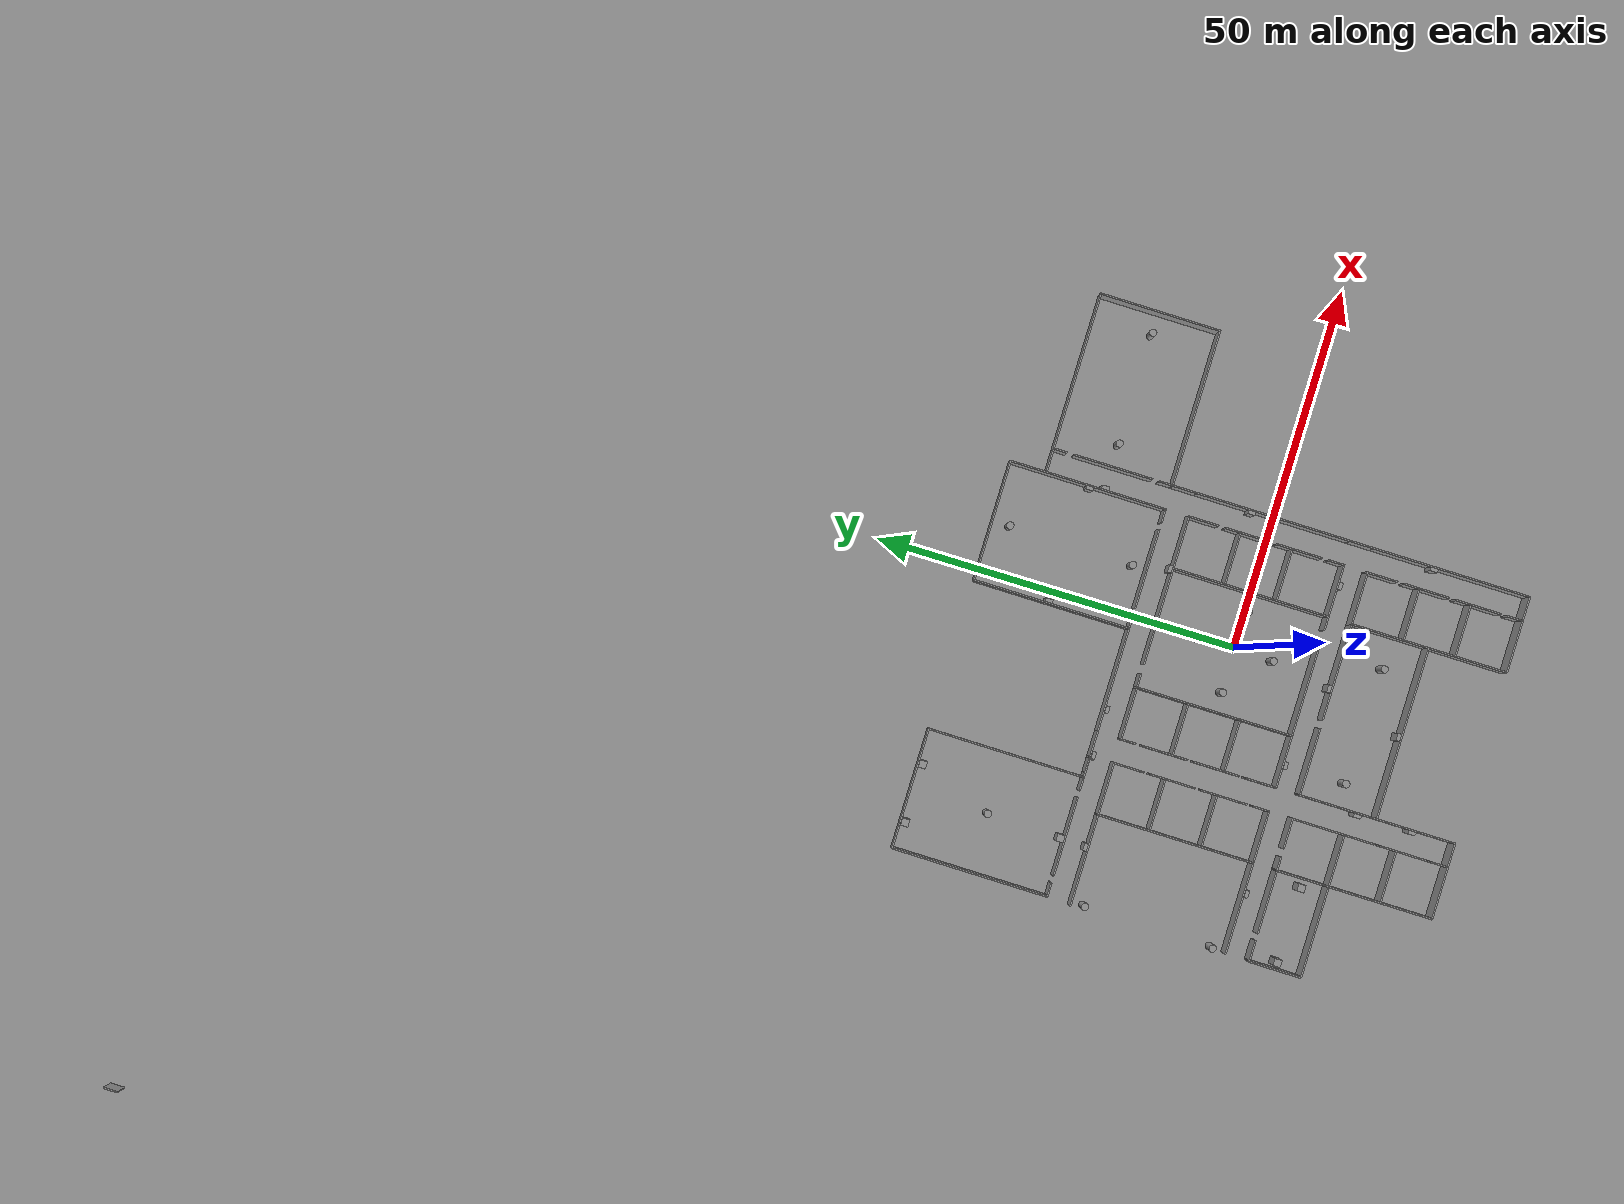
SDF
<sdf version="1.6">
 <world name="default">
  <light name="sun" type="directional">
   <pose>0 0 10 0 -0 0</pose>
   <diffuse>0.8 0.8 0.8 1</diffuse>
   <specular>0.1 0.1 0.1 1</specular>
   <attenuation>
    <range>1000</range>
    <constant>0.9</constant>
    <linear>0.01</linear>
    <quadratic>0.001</quadratic>
   </attenuation>
   <direction>-0.5 0.5 -1</direction>
  </light>
  <gravity>0 0 -9.8</gravity>
  <magnetic_field>6e-06 2.3e-05 -4.2e-05</magnetic_field>
  <atmosphere type="adiabatic"/>
  <physics name="default_physics" default="0" type="ode">
   <max_step_size>0.001</max_step_size>
   <real_time_factor>1</real_time_factor>
   <real_time_update_rate>1000</real_time_update_rate>
  </physics>
  <scene><ambient>0.4 0.4 0.4 1</ambient><background>0.7 0.7 0.7 1</background><shadows>1</shadows></scene>
  <spherical_coordinates>
   <surface_model>EARTH_WGS84</surface_model>
   <latitude_deg>0</latitude_deg>
   <longitude_deg>0</longitude_deg>
   <elevation>0</elevation>
   <heading_deg>0</heading_deg>
  </spherical_coordinates>
  <model name="ground_plane_0">
   <static>1</static>
   <link name="link">
    <collision name="collision">
     <geometry><plane><normal>0 0 1</normal><size>100 100</size></plane></geometry>
     <surface><friction><ode><mu>100</mu><mu2>50</mu2></ode></friction></surface>
    </collision>
    <visual name="visual">
     <cast_shadows>0</cast_shadows>
     <geometry><plane><normal>0 0 1</normal><size>100 100</size></plane></geometry>
     <material>
      <script><uri>file://media/materials/scripts/gazebo.material</uri><name>Gazebo/Grey</name></script>
     </material>
    </visual>
   </link>
   <pose>-5.34924 -9.48736 0 0 -0 0</pose>
  </model>
  <model name="grey_wall_0_clone_0_0_clone">
   <link name="link">
    <pose>-0.251263 -0.001927 1.4 0 -0 0</pose>
    <inertial>
     <mass>1</mass>
     <inertia><ixx>1</ixx><ixy>0</ixy><ixz>0</ixz><iyy>1</iyy><iyz>0</iyz><izz>1</izz></inertia>
    </inertial>
    <visual name="visual">
     <cast_shadows>0</cast_shadows>
     <geometry><box><size>7.4 0.2 2.8</size></box></geometry>
     <material>
      <script>
       <uri>model://grey_wall/materials/scripts</uri>
       <uri>model://grey_wall/materials/textures</uri>
       <name>vrc/grey_wall</name>
      </script>
      <ambient>1 1 1 1</ambient>
      <diffuse>1 1 1 1</diffuse>
      <specular>0 0 0 1</specular>
      <emissive>0 0 0 1</emissive>
      <shader type="vertex"><normal_map>__default__</normal_map></shader>
     </material>
    </visual>
    <collision name="collision">
     <geometry><box><size>7.4 0.2 2.8</size></box></geometry>
     <surface>
      <friction>
       <ode><mu>1</mu><mu2>1</mu2><fdir1>0 0 0</fdir1><slip1>0</slip1><slip2>0</slip2></ode>
       <torsional>
        <coefficient>1</coefficient>
        <patch_radius>0</patch_radius>
        <surface_radius>0</surface_radius>
        <use_patch_radius>1</use_patch_radius>
        <ode><slip>0</slip></ode>
       </torsional>
      </friction>
      <bounce><restitution_coefficient>0</restitution_coefficient><threshold>1e+06</threshold></bounce>
      <contact>
       <collide_without_contact>0</collide_without_contact>
       <collide_without_contact_bitmask>1</collide_without_contact_bitmask>
       <collide_bitmask>1</collide_bitmask>
       <ode>
        <soft_cfm>0</soft_cfm>
        <soft_erp>0.2</soft_erp>
        <kp>1e+13</kp>
        <kd>1</kd>
        <max_vel>0.01</max_vel>
        <min_depth>0</min_depth>
       </ode>
       <bullet>
        <split_impulse>1</split_impulse>
        <split_impulse_penetration_threshold>-0.01</split_impulse_penetration_threshold>
        <soft_cfm>0</soft_cfm>
        <soft_erp>0.2</soft_erp>
        <kp>1e+13</kp>
        <kd>1</kd>
       </bullet>
      </contact>
     </surface>
    </collision>
   </link>
   <static>1</static>
   <pose>11.3835 -3.1139 0 0 -0 0</pose>
  </model>
  <model name="grey_wall_0_clone_0_0_clone_clone">
   <link name="link">
    <pose>-0.251263 -0.001927 1.4 0 -0 0</pose>
    <inertial>
     <mass>1</mass>
     <inertia><ixx>1</ixx><ixy>0</ixy><ixz>0</ixz><iyy>1</iyy><iyz>0</iyz><izz>1</izz></inertia>
    </inertial>
    <visual name="visual">
     <cast_shadows>0</cast_shadows>
     <geometry><box><size>7.4 0.2 2.8</size></box></geometry>
     <material>
      <script>
       <uri>model://grey_wall/materials/scripts</uri>
       <uri>model://grey_wall/materials/textures</uri>
       <name>vrc/grey_wall</name>
      </script>
      <ambient>1 1 1 1</ambient>
      <diffuse>1 1 1 1</diffuse>
      <specular>0 0 0 1</specular>
      <emissive>0 0 0 1</emissive>
      <shader type="vertex"><normal_map>__default__</normal_map></shader>
     </material>
    </visual>
    <collision name="collision">
     <geometry><box><size>7.4 0.2 2.8</size></box></geometry>
     <surface>
      <friction>
       <ode><mu>1</mu><mu2>1</mu2><fdir1>0 0 0</fdir1><slip1>0</slip1><slip2>0</slip2></ode>
       <torsional>
        <coefficient>1</coefficient>
        <patch_radius>0</patch_radius>
        <surface_radius>0</surface_radius>
        <use_patch_radius>1</use_patch_radius>
        <ode><slip>0</slip></ode>
       </torsional>
      </friction>
      <bounce><restitution_coefficient>0</restitution_coefficient><threshold>1e+06</threshold></bounce>
      <contact>
       <collide_without_contact>0</collide_without_contact>
       <collide_without_contact_bitmask>1</collide_without_contact_bitmask>
       <collide_bitmask>1</collide_bitmask>
       <ode>
        <soft_cfm>0</soft_cfm>
        <soft_erp>0.2</soft_erp>
        <kp>1e+13</kp>
        <kd>1</kd>
        <max_vel>0.01</max_vel>
        <min_depth>0</min_depth>
       </ode>
       <bullet>
        <split_impulse>1</split_impulse>
        <split_impulse_penetration_threshold>-0.01</split_impulse_penetration_threshold>
        <soft_cfm>0</soft_cfm>
        <soft_erp>0.2</soft_erp>
        <kp>1e+13</kp>
        <kd>1</kd>
       </bullet>
      </contact>
     </surface>
    </collision>
   </link>
   <static>1</static>
   <pose>11.4392 4.08832 0 0 -0 0</pose>
  </model>
  <model name="grey_wall_0_clone_0_0_clone_clone_clone">
   <link name="link">
    <pose>-0.251263 -0.001927 1.4 0 -0 0</pose>
    <inertial>
     <mass>1</mass>
     <inertia><ixx>1</ixx><ixy>0</ixy><ixz>0</ixz><iyy>1</iyy><iyz>0</iyz><izz>1</izz></inertia>
    </inertial>
    <visual name="visual">
     <cast_shadows>0</cast_shadows>
     <geometry><box><size>7.4 0.2 2.8</size></box></geometry>
     <material>
      <script>
       <uri>model://grey_wall/materials/scripts</uri>
       <uri>model://grey_wall/materials/textures</uri>
       <name>vrc/grey_wall</name>
      </script>
      <ambient>1 1 1 1</ambient>
      <diffuse>1 1 1 1</diffuse>
      <specular>0 0 0 1</specular>
      <emissive>0 0 0 1</emissive>
      <shader type="vertex"><normal_map>__default__</normal_map></shader>
     </material>
    </visual>
    <collision name="collision">
     <geometry><box><size>7.4 0.2 2.8</size></box></geometry>
     <surface>
      <friction>
       <ode><mu>1</mu><mu2>1</mu2><fdir1>0 0 0</fdir1><slip1>0</slip1><slip2>0</slip2></ode>
       <torsional>
        <coefficient>1</coefficient>
        <patch_radius>0</patch_radius>
        <surface_radius>0</surface_radius>
        <use_patch_radius>1</use_patch_radius>
        <ode><slip>0</slip></ode>
       </torsional>
      </friction>
      <bounce><restitution_coefficient>0</restitution_coefficient><threshold>1e+06</threshold></bounce>
      <contact>
       <collide_without_contact>0</collide_without_contact>
       <collide_without_contact_bitmask>1</collide_without_contact_bitmask>
       <collide_bitmask>1</collide_bitmask>
       <ode>
        <soft_cfm>0</soft_cfm>
        <soft_erp>0.2</soft_erp>
        <kp>1e+13</kp>
        <kd>1</kd>
        <max_vel>0.01</max_vel>
        <min_depth>0</min_depth>
       </ode>
       <bullet>
        <split_impulse>1</split_impulse>
        <split_impulse_penetration_threshold>-0.01</split_impulse_penetration_threshold>
        <soft_cfm>0</soft_cfm>
        <soft_erp>0.2</soft_erp>
        <kp>1e+13</kp>
        <kd>1</kd>
       </bullet>
      </contact>
     </surface>
    </collision>
   </link>
   <static>1</static>
   <pose>11.4788 11.2922 0 0 -0 0</pose>
  </model>
  <model name="g2_clone_0_0_clone">
   <link name="link">
    <pose>0 0 1.4 0 -0 0</pose>
    <inertial>
     <mass>1</mass>
     <inertia><ixx>1</ixx><ixy>0</ixy><ixz>0</ixz><iyy>1</iyy><iyz>0</iyz><izz>1</izz></inertia>
    </inertial>
    <visual name="visual">
     <cast_shadows>0</cast_shadows>
     <geometry><box><size>21.8 0.2 2.8</size></box></geometry>
     <material>
      <script>
       <uri>model://grey_wall/materials/scripts</uri>
       <uri>model://grey_wall/materials/textures</uri>
       <name>vrc/grey_wall</name>
      </script>
      <ambient>1 1 1 1</ambient>
      <diffuse>1 1 1 1</diffuse>
      <specular>0 0 0 1</specular>
      <emissive>0 0 0 1</emissive>
      <shader type="vertex"><normal_map>__default__</normal_map></shader>
     </material>
    </visual>
    <collision name="collision">
     <geometry><box><size>21.8 0.2 2.8</size></box></geometry>
     <surface>
      <friction>
       <ode><mu>1</mu><mu2>1</mu2><fdir1>0 0 0</fdir1><slip1>0</slip1><slip2>0</slip2></ode>
       <torsional>
        <coefficient>1</coefficient>
        <patch_radius>0</patch_radius>
        <surface_radius>0</surface_radius>
        <use_patch_radius>1</use_patch_radius>
        <ode><slip>0</slip></ode>
       </torsional>
      </friction>
      <bounce><restitution_coefficient>0</restitution_coefficient><threshold>1e+06</threshold></bounce>
      <contact>
       <collide_without_contact>0</collide_without_contact>
       <collide_without_contact_bitmask>1</collide_without_contact_bitmask>
       <collide_bitmask>1</collide_bitmask>
       <ode>
        <soft_cfm>0</soft_cfm>
        <soft_erp>0.2</soft_erp>
        <kp>1e+13</kp>
        <kd>1</kd>
        <max_vel>0.01</max_vel>
        <min_depth>0</min_depth>
       </ode>
       <bullet>
        <split_impulse>1</split_impulse>
        <split_impulse_penetration_threshold>-0.01</split_impulse_penetration_threshold>
        <soft_cfm>0</soft_cfm>
        <soft_erp>0.2</soft_erp>
        <kp>1e+13</kp>
        <kd>1</kd>
       </bullet>
      </contact>
     </surface>
    </collision>
   </link>
   <static>1</static>
   <pose>-9.04445 0.475213 0 0 0 -1.57584</pose>
  </model>
  <model name="g2_clone_0_0_0">
   <link name="link">
    <pose>0 0 1.4 0 -0 0</pose>
    <inertial>
     <mass>1</mass>
     <inertia><ixx>1</ixx><ixy>0</ixy><ixz>0</ixz><iyy>1</iyy><iyz>0</iyz><izz>1</izz></inertia>
    </inertial>
    <visual name="visual">
     <cast_shadows>0</cast_shadows>
     <geometry><box><size>21.8 0.2 2.8</size></box></geometry>
     <material>
      <script>
       <uri>model://grey_wall/materials/scripts</uri>
       <uri>model://grey_wall/materials/textures</uri>
       <name>vrc/grey_wall</name>
      </script>
      <ambient>1 1 1 1</ambient>
      <diffuse>1 1 1 1</diffuse>
      <specular>0 0 0 1</specular>
      <emissive>0 0 0 1</emissive>
      <shader type="vertex"><normal_map>__default__</normal_map></shader>
     </material>
    </visual>
    <collision name="collision">
     <geometry><box><size>21.8 0.2 2.8</size></box></geometry>
     <surface>
      <friction>
       <ode><mu>1</mu><mu2>1</mu2><fdir1>0 0 0</fdir1><slip1>0</slip1><slip2>0</slip2></ode>
       <torsional>
        <coefficient>1</coefficient>
        <patch_radius>0</patch_radius>
        <surface_radius>0</surface_radius>
        <use_patch_radius>1</use_patch_radius>
        <ode><slip>0</slip></ode>
       </torsional>
      </friction>
      <bounce><restitution_coefficient>0</restitution_coefficient><threshold>1e+06</threshold></bounce>
      <contact>
       <collide_without_contact>0</collide_without_contact>
       <collide_without_contact_bitmask>1</collide_without_contact_bitmask>
       <collide_bitmask>1</collide_bitmask>
       <ode>
        <soft_cfm>0</soft_cfm>
        <soft_erp>0.2</soft_erp>
        <kp>1e+13</kp>
        <kd>1</kd>
        <max_vel>0.01</max_vel>
        <min_depth>0</min_depth>
       </ode>
       <bullet>
        <split_impulse>1</split_impulse>
        <split_impulse_penetration_threshold>-0.01</split_impulse_penetration_threshold>
        <soft_cfm>0</soft_cfm>
        <soft_erp>0.2</soft_erp>
        <kp>1e+13</kp>
        <kd>1</kd>
       </bullet>
      </contact>
     </surface>
    </collision>
   </link>
   <static>1</static>
   <pose>7.54974 0.473365 0 0 0 -1.57584</pose>
  </model>
  <model name="grey_wall_0_clone_0_0_0">
   <link name="link">
    <pose>-0.251263 -0.001927 1.4 0 -0 0</pose>
    <inertial>
     <mass>1</mass>
     <inertia><ixx>1</ixx><ixy>0</ixy><ixz>0</ixz><iyy>1</iyy><iyz>0</iyz><izz>1</izz></inertia>
    </inertial>
    <visual name="visual">
     <cast_shadows>0</cast_shadows>
     <geometry><box><size>7.4 0.2 2.8</size></box></geometry>
     <material>
      <script>
       <uri>model://grey_wall/materials/scripts</uri>
       <uri>model://grey_wall/materials/textures</uri>
       <name>vrc/grey_wall</name>
      </script>
      <ambient>1 1 1 1</ambient>
      <diffuse>1 1 1 1</diffuse>
      <specular>0 0 0 1</specular>
      <emissive>0 0 0 1</emissive>
      <shader type="vertex"><normal_map>__default__</normal_map></shader>
     </material>
    </visual>
    <collision name="collision">
     <geometry><box><size>7.4 0.2 2.8</size></box></geometry>
     <surface>
      <friction>
       <ode><mu>1</mu><mu2>1</mu2><fdir1>0 0 0</fdir1><slip1>0</slip1><slip2>0</slip2></ode>
       <torsional>
        <coefficient>1</coefficient>
        <patch_radius>0</patch_radius>
        <surface_radius>0</surface_radius>
        <use_patch_radius>1</use_patch_radius>
        <ode><slip>0</slip></ode>
       </torsional>
      </friction>
      <bounce><restitution_coefficient>0</restitution_coefficient><threshold>1e+06</threshold></bounce>
      <contact>
       <collide_without_contact>0</collide_without_contact>
       <collide_without_contact_bitmask>1</collide_without_contact_bitmask>
       <collide_bitmask>1</collide_bitmask>
       <ode>
        <soft_cfm>0</soft_cfm>
        <soft_erp>0.2</soft_erp>
        <kp>1e+13</kp>
        <kd>1</kd>
        <max_vel>0.01</max_vel>
        <min_depth>0</min_depth>
       </ode>
       <bullet>
        <split_impulse>1</split_impulse>
        <split_impulse_penetration_threshold>-0.01</split_impulse_penetration_threshold>
        <soft_cfm>0</soft_cfm>
        <soft_erp>0.2</soft_erp>
        <kp>1e+13</kp>
        <kd>1</kd>
       </bullet>
      </contact>
     </surface>
    </collision>
   </link>
   <static>1</static>
   <pose>11.347 -10.3243 0 0 -0 0</pose>
  </model>
  <model name="grey_wall_0_0">
   <link name="link">
    <pose>0 0 1.4 0 -0 0</pose>
    <inertial>
     <mass>1</mass>
     <inertia><ixx>1</ixx><ixy>0</ixy><ixz>0</ixz><iyy>1</iyy><iyz>0</iyz><izz>1</izz></inertia>
    </inertial>
    <visual name="visual">
     <cast_shadows>0</cast_shadows>
     <geometry><box><size>7.4 0.2 2.8</size></box></geometry>
     <material>
      <script>
       <uri>model://grey_wall/materials/scripts</uri>
       <uri>model://grey_wall/materials/textures</uri>
       <name>vrc/grey_wall</name>
      </script>
      <ambient>1 1 1 1</ambient>
      <diffuse>1 1 1 1</diffuse>
      <specular>0 0 0 1</specular>
      <emissive>0 0 0 1</emissive>
      <shader type="vertex"><normal_map>__default__</normal_map></shader>
     </material>
    </visual>
    <collision name="collision">
     <geometry><box><size>7.4 0.2 2.8</size></box></geometry>
     <surface>
      <friction>
       <ode><mu>1</mu><mu2>1</mu2><fdir1>0 0 0</fdir1><slip1>0</slip1><slip2>0</slip2></ode>
       <torsional>
        <coefficient>1</coefficient>
        <patch_radius>0</patch_radius>
        <surface_radius>0</surface_radius>
        <use_patch_radius>1</use_patch_radius>
        <ode><slip>0</slip></ode>
       </torsional>
      </friction>
      <bounce><restitution_coefficient>0</restitution_coefficient><threshold>1e+06</threshold></bounce>
      <contact>
       <collide_without_contact>0</collide_without_contact>
       <collide_without_contact_bitmask>1</collide_without_contact_bitmask>
       <collide_bitmask>1</collide_bitmask>
       <ode>
        <soft_cfm>0</soft_cfm>
        <soft_erp>0.2</soft_erp>
        <kp>1e+13</kp>
        <kd>1</kd>
        <max_vel>0.01</max_vel>
        <min_depth>0</min_depth>
       </ode>
       <bullet>
        <split_impulse>1</split_impulse>
        <split_impulse_penetration_threshold>-0.01</split_impulse_penetration_threshold>
        <soft_cfm>0</soft_cfm>
        <soft_erp>0.2</soft_erp>
        <kp>1e+13</kp>
        <kd>1</kd>
       </bullet>
      </contact>
     </surface>
    </collision>
   </link>
   <static>1</static>
   <pose>-12.7052 -10.3243 0 0 -0 0</pose>
  </model>
  <model name="grey_wall_0_0_clone">
   <link name="link">
    <pose>0 0 1.4 0 -0 0</pose>
    <inertial>
     <mass>1</mass>
     <inertia><ixx>1</ixx><ixy>0</ixy><ixz>0</ixz><iyy>1</iyy><iyz>0</iyz><izz>1</izz></inertia>
    </inertial>
    <visual name="visual">
     <cast_shadows>0</cast_shadows>
     <geometry><box><size>7.4 0.2 2.8</size></box></geometry>
     <material>
      <script>
       <uri>model://grey_wall/materials/scripts</uri>
       <uri>model://grey_wall/materials/textures</uri>
       <name>vrc/grey_wall</name>
      </script>
      <ambient>1 1 1 1</ambient>
      <diffuse>1 1 1 1</diffuse>
      <specular>0 0 0 1</specular>
      <emissive>0 0 0 1</emissive>
      <shader type="vertex"><normal_map>__default__</normal_map></shader>
     </material>
    </visual>
    <collision name="collision">
     <geometry><box><size>7.4 0.2 2.8</size></box></geometry>
     <surface>
      <friction>
       <ode><mu>1</mu><mu2>1</mu2><fdir1>0 0 0</fdir1><slip1>0</slip1><slip2>0</slip2></ode>
       <torsional>
        <coefficient>1</coefficient>
        <patch_radius>0</patch_radius>
        <surface_radius>0</surface_radius>
        <use_patch_radius>1</use_patch_radius>
        <ode><slip>0</slip></ode>
       </torsional>
      </friction>
      <bounce><restitution_coefficient>0</restitution_coefficient><threshold>1e+06</threshold></bounce>
      <contact>
       <collide_without_contact>0</collide_without_contact>
       <collide_without_contact_bitmask>1</collide_without_contact_bitmask>
       <collide_bitmask>1</collide_bitmask>
       <ode>
        <soft_cfm>0</soft_cfm>
        <soft_erp>0.2</soft_erp>
        <kp>1e+13</kp>
        <kd>1</kd>
        <max_vel>0.01</max_vel>
        <min_depth>0</min_depth>
       </ode>
       <bullet>
        <split_impulse>1</split_impulse>
        <split_impulse_penetration_threshold>-0.01</split_impulse_penetration_threshold>
        <soft_cfm>0</soft_cfm>
        <soft_erp>0.2</soft_erp>
        <kp>1e+13</kp>
        <kd>1</kd>
       </bullet>
      </contact>
     </surface>
    </collision>
   </link>
   <static>1</static>
   <pose>-12.6638 -3.11787 0 0 -0 0</pose>
  </model>
  <model name="grey_wall_0_0_clone_0">
   <link name="link">
    <pose>0 0 1.4 0 -0 0</pose>
    <inertial>
     <mass>1</mass>
     <inertia><ixx>1</ixx><ixy>0</ixy><ixz>0</ixz><iyy>1</iyy><iyz>0</iyz><izz>1</izz></inertia>
    </inertial>
    <visual name="visual">
     <cast_shadows>0</cast_shadows>
     <geometry><box><size>7.4 0.2 2.8</size></box></geometry>
     <material>
      <script>
       <uri>model://grey_wall/materials/scripts</uri>
       <uri>model://grey_wall/materials/textures</uri>
       <name>vrc/grey_wall</name>
      </script>
      <ambient>1 1 1 1</ambient>
      <diffuse>1 1 1 1</diffuse>
      <specular>0 0 0 1</specular>
      <emissive>0 0 0 1</emissive>
      <shader type="vertex"><normal_map>__default__</normal_map></shader>
     </material>
    </visual>
    <collision name="collision">
     <geometry><box><size>7.4 0.2 2.8</size></box></geometry>
     <surface>
      <friction>
       <ode><mu>1</mu><mu2>1</mu2><fdir1>0 0 0</fdir1><slip1>0</slip1><slip2>0</slip2></ode>
       <torsional>
        <coefficient>1</coefficient>
        <patch_radius>0</patch_radius>
        <surface_radius>0</surface_radius>
        <use_patch_radius>1</use_patch_radius>
        <ode><slip>0</slip></ode>
       </torsional>
      </friction>
      <bounce><restitution_coefficient>0</restitution_coefficient><threshold>1e+06</threshold></bounce>
      <contact>
       <collide_without_contact>0</collide_without_contact>
       <collide_without_contact_bitmask>1</collide_without_contact_bitmask>
       <collide_bitmask>1</collide_bitmask>
       <ode>
        <soft_cfm>0</soft_cfm>
        <soft_erp>0.2</soft_erp>
        <kp>1e+13</kp>
        <kd>1</kd>
        <max_vel>0.01</max_vel>
        <min_depth>0</min_depth>
       </ode>
       <bullet>
        <split_impulse>1</split_impulse>
        <split_impulse_penetration_threshold>-0.01</split_impulse_penetration_threshold>
        <soft_cfm>0</soft_cfm>
        <soft_erp>0.2</soft_erp>
        <kp>1e+13</kp>
        <kd>1</kd>
       </bullet>
      </contact>
     </surface>
    </collision>
   </link>
   <static>1</static>
   <pose>-12.6294 4.10196 0 0 -0 0</pose>
  </model>
  <model name="grey_wall_0_0_clone_1">
   <link name="link">
    <pose>0 0 1.4 0 -0 0</pose>
    <inertial>
     <mass>1</mass>
     <inertia><ixx>1</ixx><ixy>0</ixy><ixz>0</ixz><iyy>1</iyy><iyz>0</iyz><izz>1</izz></inertia>
    </inertial>
    <visual name="visual">
     <cast_shadows>0</cast_shadows>
     <geometry><box><size>7.4 0.2 2.8</size></box></geometry>
     <material>
      <script>
       <uri>model://grey_wall/materials/scripts</uri>
       <uri>model://grey_wall/materials/textures</uri>
       <name>vrc/grey_wall</name>
      </script>
      <ambient>1 1 1 1</ambient>
      <diffuse>1 1 1 1</diffuse>
      <specular>0 0 0 1</specular>
      <emissive>0 0 0 1</emissive>
      <shader type="vertex"><normal_map>__default__</normal_map></shader>
     </material>
    </visual>
    <collision name="collision">
     <geometry><box><size>7.4 0.2 2.8</size></box></geometry>
     <surface>
      <friction>
       <ode><mu>1</mu><mu2>1</mu2><fdir1>0 0 0</fdir1><slip1>0</slip1><slip2>0</slip2></ode>
       <torsional>
        <coefficient>1</coefficient>
        <patch_radius>0</patch_radius>
        <surface_radius>0</surface_radius>
        <use_patch_radius>1</use_patch_radius>
        <ode><slip>0</slip></ode>
       </torsional>
      </friction>
      <bounce><restitution_coefficient>0</restitution_coefficient><threshold>1e+06</threshold></bounce>
      <contact>
       <collide_without_contact>0</collide_without_contact>
       <collide_without_contact_bitmask>1</collide_without_contact_bitmask>
       <collide_bitmask>1</collide_bitmask>
       <ode>
        <soft_cfm>0</soft_cfm>
        <soft_erp>0.2</soft_erp>
        <kp>1e+13</kp>
        <kd>1</kd>
        <max_vel>0.01</max_vel>
        <min_depth>0</min_depth>
       </ode>
       <bullet>
        <split_impulse>1</split_impulse>
        <split_impulse_penetration_threshold>-0.01</split_impulse_penetration_threshold>
        <soft_cfm>0</soft_cfm>
        <soft_erp>0.2</soft_erp>
        <kp>1e+13</kp>
        <kd>1</kd>
       </bullet>
      </contact>
     </surface>
    </collision>
   </link>
   <static>1</static>
   <pose>-12.5933 11.2689 0 0 -0 0</pose>
  </model>
  <model name="g3_clone_clone_0_clone_0_0_0_0_0_0_clone_clone_clone_0_clone_0_clone_0_clone_0">
   <link name="link">
    <pose>1.55996 -1.33829 1.4 0 -0 0.001589</pose>
    <inertial>
     <mass>1</mass>
     <inertia><ixx>1</ixx><ixy>0</ixy><ixz>0</ixz><iyy>1</iyy><iyz>0</iyz><izz>1</izz></inertia>
    </inertial>
    <visual name="visual">
     <cast_shadows>0</cast_shadows>
     <geometry><box><size>2 0.2 2.8</size></box></geometry>
     <material>
      <script>
       <uri>model://grey_wall/materials/scripts</uri>
       <uri>model://grey_wall/materials/textures</uri>
       <name>vrc/grey_wall</name>
      </script>
      <ambient>1 1 1 1</ambient>
      <diffuse>1 1 1 1</diffuse>
      <specular>0 0 0 1</specular>
      <emissive>0 0 0 1</emissive>
      <shader type="vertex"><normal_map>__default__</normal_map></shader>
     </material>
    </visual>
    <collision name="collision">
     <geometry><box><size>2 0.2 2.8</size></box></geometry>
     <surface>
      <friction>
       <ode><mu>1</mu><mu2>1</mu2><fdir1>0 0 0</fdir1><slip1>0</slip1><slip2>0</slip2></ode>
       <torsional>
        <coefficient>1</coefficient>
        <patch_radius>0</patch_radius>
        <surface_radius>0</surface_radius>
        <use_patch_radius>1</use_patch_radius>
        <ode><slip>0</slip></ode>
       </torsional>
      </friction>
      <bounce><restitution_coefficient>0</restitution_coefficient><threshold>1e+06</threshold></bounce>
      <contact>
       <collide_without_contact>0</collide_without_contact>
       <collide_without_contact_bitmask>1</collide_without_contact_bitmask>
       <collide_bitmask>1</collide_bitmask>
       <ode>
        <soft_cfm>0</soft_cfm>
        <soft_erp>0.2</soft_erp>
        <kp>1e+13</kp>
        <kd>1</kd>
        <max_vel>0.01</max_vel>
        <min_depth>0</min_depth>
       </ode>
       <bullet>
        <split_impulse>1</split_impulse>
        <split_impulse_penetration_threshold>-0.01</split_impulse_penetration_threshold>
        <soft_cfm>0</soft_cfm>
        <soft_erp>0.2</soft_erp>
        <kp>1e+13</kp>
        <kd>1</kd>
       </bullet>
      </contact>
     </surface>
    </collision>
   </link>
   <static>1</static>
   <pose>-9.66867 12.5986 0 0 -0 0.011271</pose>
  </model>
  <model name="g3_clone_clone_0_clone_0_0_0_0_0_0_clone_clone_clone_0_clone_0_clone_0_clone_0_clone">
   <link name="link">
    <pose>1.55996 -1.33829 1.4 0 -0 0.001589</pose>
    <inertial>
     <mass>1</mass>
     <inertia><ixx>1</ixx><ixy>0</ixy><ixz>0</ixz><iyy>1</iyy><iyz>0</iyz><izz>1</izz></inertia>
    </inertial>
    <visual name="visual">
     <cast_shadows>0</cast_shadows>
     <geometry><box><size>2 0.2 2.8</size></box></geometry>
     <material>
      <script>
       <uri>model://grey_wall/materials/scripts</uri>
       <uri>model://grey_wall/materials/textures</uri>
       <name>vrc/grey_wall</name>
      </script>
      <ambient>1 1 1 1</ambient>
      <diffuse>1 1 1 1</diffuse>
      <specular>0 0 0 1</specular>
      <emissive>0 0 0 1</emissive>
      <shader type="vertex"><normal_map>__default__</normal_map></shader>
     </material>
    </visual>
    <collision name="collision">
     <geometry><box><size>2 0.2 2.8</size></box></geometry>
     <surface>
      <friction>
       <ode><mu>1</mu><mu2>1</mu2><fdir1>0 0 0</fdir1><slip1>0</slip1><slip2>0</slip2></ode>
       <torsional>
        <coefficient>1</coefficient>
        <patch_radius>0</patch_radius>
        <surface_radius>0</surface_radius>
        <use_patch_radius>1</use_patch_radius>
        <ode><slip>0</slip></ode>
       </torsional>
      </friction>
      <bounce><restitution_coefficient>0</restitution_coefficient><threshold>1e+06</threshold></bounce>
      <contact>
       <collide_without_contact>0</collide_without_contact>
       <collide_without_contact_bitmask>1</collide_without_contact_bitmask>
       <collide_bitmask>1</collide_bitmask>
       <ode>
        <soft_cfm>0</soft_cfm>
        <soft_erp>0.2</soft_erp>
        <kp>1e+13</kp>
        <kd>1</kd>
        <max_vel>0.01</max_vel>
        <min_depth>0</min_depth>
       </ode>
       <bullet>
        <split_impulse>1</split_impulse>
        <split_impulse_penetration_threshold>-0.01</split_impulse_penetration_threshold>
        <soft_cfm>0</soft_cfm>
        <soft_erp>0.2</soft_erp>
        <kp>1e+13</kp>
        <kd>1</kd>
       </bullet>
      </contact>
     </surface>
    </collision>
   </link>
   <static>1</static>
   <pose>5.02098 -9.01184 0 0 -0 0.002262</pose>
  </model>
  <model name="g1_clone_1_1_clone">
   <link name="link">
    <pose>0.251458 0.000378 1.4 0 -0 0</pose>
    <inertial>
     <mass>1</mass>
     <inertia><ixx>1</ixx><ixy>0</ixy><ixz>0</ixz><iyy>1</iyy><iyz>0</iyz><izz>1</izz></inertia>
    </inertial>
    <visual name="visual">
     <cast_shadows>0</cast_shadows>
     <geometry><box><size>13.5 0.2 2.8</size></box></geometry>
     <material>
      <script>
       <uri>model://grey_wall/materials/scripts</uri>
       <uri>model://grey_wall/materials/textures</uri>
       <name>vrc/grey_wall</name>
      </script>
      <ambient>1 1 1 1</ambient>
      <diffuse>1 1 1 1</diffuse>
      <specular>0 0 0 1</specular>
      <emissive>0 0 0 1</emissive>
      <shader type="vertex"><normal_map>__default__</normal_map></shader>
     </material>
    </visual>
    <collision name="collision">
     <geometry><box><size>13.5 0.2 2.8</size></box></geometry>
     <surface>
      <friction>
       <ode><mu>1</mu><mu2>1</mu2><fdir1>0 0 0</fdir1><slip1>0</slip1><slip2>0</slip2></ode>
       <torsional>
        <coefficient>1</coefficient>
        <patch_radius>0</patch_radius>
        <surface_radius>0</surface_radius>
        <use_patch_radius>1</use_patch_radius>
        <ode><slip>0</slip></ode>
       </torsional>
      </friction>
      <bounce><restitution_coefficient>0</restitution_coefficient><threshold>1e+06</threshold></bounce>
      <contact>
       <collide_without_contact>0</collide_without_contact>
       <collide_without_contact_bitmask>1</collide_without_contact_bitmask>
       <collide_bitmask>1</collide_bitmask>
       <ode>
        <soft_cfm>0</soft_cfm>
        <soft_erp>0.2</soft_erp>
        <kp>1e+13</kp>
        <kd>1</kd>
        <max_vel>0.01</max_vel>
        <min_depth>0</min_depth>
       </ode>
       <bullet>
        <split_impulse>1</split_impulse>
        <split_impulse_penetration_threshold>-0.01</split_impulse_penetration_threshold>
        <soft_cfm>0</soft_cfm>
        <soft_erp>0.2</soft_erp>
        <kp>1e+13</kp>
        <kd>1</kd>
       </bullet>
      </contact>
     </surface>
    </collision>
   </link>
   <static>1</static>
   <pose>-2.69768 -10.3249 0 0 -0 0</pose>
  </model>
  <model name="g1_clone_1_1_0">
   <link name="link">
    <pose>0.251458 0.000378 1.4 0 -0 0</pose>
    <inertial>
     <mass>1</mass>
     <inertia><ixx>1</ixx><ixy>0</ixy><ixz>0</ixz><iyy>1</iyy><iyz>0</iyz><izz>1</izz></inertia>
    </inertial>
    <visual name="visual">
     <cast_shadows>0</cast_shadows>
     <geometry><box><size>13.5 0.2 2.8</size></box></geometry>
     <material>
      <script>
       <uri>model://grey_wall/materials/scripts</uri>
       <uri>model://grey_wall/materials/textures</uri>
       <name>vrc/grey_wall</name>
      </script>
      <ambient>1 1 1 1</ambient>
      <diffuse>1 1 1 1</diffuse>
      <specular>0 0 0 1</specular>
      <emissive>0 0 0 1</emissive>
      <shader type="vertex"><normal_map>__default__</normal_map></shader>
     </material>
    </visual>
    <collision name="collision">
     <geometry><box><size>13.5 0.2 2.8</size></box></geometry>
     <surface>
      <friction>
       <ode><mu>1</mu><mu2>1</mu2><fdir1>0 0 0</fdir1><slip1>0</slip1><slip2>0</slip2></ode>
       <torsional>
        <coefficient>1</coefficient>
        <patch_radius>0</patch_radius>
        <surface_radius>0</surface_radius>
        <use_patch_radius>1</use_patch_radius>
        <ode><slip>0</slip></ode>
       </torsional>
      </friction>
      <bounce><restitution_coefficient>0</restitution_coefficient><threshold>1e+06</threshold></bounce>
      <contact>
       <collide_without_contact>0</collide_without_contact>
       <collide_without_contact_bitmask>1</collide_without_contact_bitmask>
       <collide_bitmask>1</collide_bitmask>
       <ode>
        <soft_cfm>0</soft_cfm>
        <soft_erp>0.2</soft_erp>
        <kp>1e+13</kp>
        <kd>1</kd>
        <max_vel>0.01</max_vel>
        <min_depth>0</min_depth>
       </ode>
       <bullet>
        <split_impulse>1</split_impulse>
        <split_impulse_penetration_threshold>-0.01</split_impulse_penetration_threshold>
        <soft_cfm>0</soft_cfm>
        <soft_erp>0.2</soft_erp>
        <kp>1e+13</kp>
        <kd>1</kd>
       </bullet>
      </contact>
     </surface>
    </collision>
   </link>
   <static>1</static>
   <pose>0.70866 11.287 0 0 -0 0</pose>
  </model>
  <model name="g2_clone_0_0_clone_clone_clone">
   <link name="link">
    <pose>0 0 1.4 0 -0 0</pose>
    <inertial>
     <mass>1</mass>
     <inertia><ixx>1</ixx><ixy>0</ixy><ixz>0</ixz><iyy>1</iyy><iyz>0</iyz><izz>1</izz></inertia>
    </inertial>
    <visual name="visual">
     <cast_shadows>0</cast_shadows>
     <geometry><box><size>21.8 0.2 2.8</size></box></geometry>
     <material>
      <script>
       <uri>model://grey_wall/materials/scripts</uri>
       <uri>model://grey_wall/materials/textures</uri>
       <name>vrc/grey_wall</name>
      </script>
      <ambient>1 1 1 1</ambient>
      <diffuse>1 1 1 1</diffuse>
      <specular>0 0 0 1</specular>
      <emissive>0 0 0 1</emissive>
      <shader type="vertex"><normal_map>__default__</normal_map></shader>
     </material>
    </visual>
    <collision name="collision">
     <geometry><box><size>21.8 0.2 2.8</size></box></geometry>
     <surface>
      <friction>
       <ode><mu>1</mu><mu2>1</mu2><fdir1>0 0 0</fdir1><slip1>0</slip1><slip2>0</slip2></ode>
       <torsional>
        <coefficient>1</coefficient>
        <patch_radius>0</patch_radius>
        <surface_radius>0</surface_radius>
        <use_patch_radius>1</use_patch_radius>
        <ode><slip>0</slip></ode>
       </torsional>
      </friction>
      <bounce><restitution_coefficient>0</restitution_coefficient><threshold>1e+06</threshold></bounce>
      <contact>
       <collide_without_contact>0</collide_without_contact>
       <collide_without_contact_bitmask>1</collide_without_contact_bitmask>
       <collide_bitmask>1</collide_bitmask>
       <ode>
        <soft_cfm>0</soft_cfm>
        <soft_erp>0.2</soft_erp>
        <kp>1e+13</kp>
        <kd>1</kd>
        <max_vel>0.01</max_vel>
        <min_depth>0</min_depth>
       </ode>
       <bullet>
        <split_impulse>1</split_impulse>
        <split_impulse_penetration_threshold>-0.01</split_impulse_penetration_threshold>
        <soft_cfm>0</soft_cfm>
        <soft_erp>0.2</soft_erp>
        <kp>1e+13</kp>
        <kd>1</kd>
       </bullet>
      </contact>
     </surface>
    </collision>
   </link>
   <static>1</static>
   <pose>18.07 0.480125 0 0 0 -1.57584</pose>
  </model>
  <model name="g3_clone_clone_0_clone_0_0_0_0_0_0_clone_clone_clone_0_clone_0_clone_1_0">
   <link name="link">
    <pose>0.277892 -0.062462 1.4 0 -0 0</pose>
    <inertial>
     <mass>1</mass>
     <inertia><ixx>1</ixx><ixy>0</ixy><ixz>0</ixz><iyy>1</iyy><iyz>0</iyz><izz>1</izz></inertia>
    </inertial>
    <visual name="visual">
     <cast_shadows>0</cast_shadows>
     <geometry><box><size>2.2 0.2 2.8</size></box></geometry>
     <material>
      <script>
       <uri>model://grey_wall/materials/scripts</uri>
       <uri>model://grey_wall/materials/textures</uri>
       <name>vrc/grey_wall</name>
      </script>
      <ambient>1 1 1 1</ambient>
      <diffuse>1 1 1 1</diffuse>
      <specular>0 0 0 1</specular>
      <emissive>0 0 0 1</emissive>
      <shader type="vertex"><normal_map>__default__</normal_map></shader>
     </material>
    </visual>
    <collision name="collision">
     <geometry><box><size>2.2 0.2 2.8</size></box></geometry>
     <surface>
      <friction>
       <ode><mu>1</mu><mu2>1</mu2><fdir1>0 0 0</fdir1><slip1>0</slip1><slip2>0</slip2></ode>
       <torsional>
        <coefficient>1</coefficient>
        <patch_radius>0</patch_radius>
        <surface_radius>0</surface_radius>
        <use_patch_radius>1</use_patch_radius>
        <ode><slip>0</slip></ode>
       </torsional>
      </friction>
      <bounce><restitution_coefficient>0</restitution_coefficient><threshold>1e+06</threshold></bounce>
      <contact>
       <collide_without_contact>0</collide_without_contact>
       <collide_without_contact_bitmask>1</collide_without_contact_bitmask>
       <collide_bitmask>1</collide_bitmask>
       <ode>
        <soft_cfm>0</soft_cfm>
        <soft_erp>0.2</soft_erp>
        <kp>1e+13</kp>
        <kd>1</kd>
        <max_vel>0.01</max_vel>
        <min_depth>0</min_depth>
       </ode>
       <bullet>
        <split_impulse>1</split_impulse>
        <split_impulse_penetration_threshold>-0.01</split_impulse_penetration_threshold>
        <soft_cfm>0</soft_cfm>
        <soft_erp>0.2</soft_erp>
        <kp>1e+13</kp>
        <kd>1</kd>
       </bullet>
      </contact>
     </surface>
    </collision>
   </link>
   <static>1</static>
   <pose>-16.1363 10.5498 0 0 0 -1.57614</pose>
  </model>
  <model name="g3_clone_clone_0_0_0_0_0_clone_0_clone_0_clone_2_clone_0_clone_0">
   <link name="link">
    <pose>0.7232 0.251992 1.4 0 -0 0</pose>
    <inertial>
     <mass>1</mass>
     <inertia><ixx>1</ixx><ixy>0</ixy><ixz>0</ixz><iyy>1</iyy><iyz>0</iyz><izz>1</izz></inertia>
    </inertial>
    <visual name="visual">
     <cast_shadows>0</cast_shadows>
     <geometry><box><size>4.3 0.2 2.8</size></box></geometry>
     <material>
      <script>
       <uri>model://grey_wall/materials/scripts</uri>
       <uri>model://grey_wall/materials/textures</uri>
       <name>vrc/grey_wall</name>
      </script>
      <ambient>1 1 1 1</ambient>
      <diffuse>1 1 1 1</diffuse>
      <specular>0 0 0 1</specular>
      <emissive>0 0 0 1</emissive>
      <shader type="vertex"><normal_map>__default__</normal_map></shader>
     </material>
    </visual>
    <collision name="collision">
     <geometry><box><size>4.3 0.2 2.8</size></box></geometry>
     <surface>
      <friction>
       <ode><mu>1</mu><mu2>1</mu2><fdir1>0 0 0</fdir1><slip1>0</slip1><slip2>0</slip2></ode>
       <torsional>
        <coefficient>1</coefficient>
        <patch_radius>0</patch_radius>
        <surface_radius>0</surface_radius>
        <use_patch_radius>1</use_patch_radius>
        <ode><slip>0</slip></ode>
       </torsional>
      </friction>
      <bounce><restitution_coefficient>0</restitution_coefficient><threshold>1e+06</threshold></bounce>
      <contact>
       <collide_without_contact>0</collide_without_contact>
       <collide_without_contact_bitmask>1</collide_without_contact_bitmask>
       <collide_bitmask>1</collide_bitmask>
       <ode>
        <soft_cfm>0</soft_cfm>
        <soft_erp>0.2</soft_erp>
        <kp>1e+13</kp>
        <kd>1</kd>
        <max_vel>0.01</max_vel>
        <min_depth>0</min_depth>
       </ode>
       <bullet>
        <split_impulse>1</split_impulse>
        <split_impulse_penetration_threshold>-0.01</split_impulse_penetration_threshold>
        <soft_cfm>0</soft_cfm>
        <soft_erp>0.2</soft_erp>
        <kp>1e+13</kp>
        <kd>1</kd>
       </bullet>
      </contact>
     </surface>
    </collision>
   </link>
   <static>1</static>
   <pose>-16.4688 6.86867 0 0 0 -1.57728</pose>
  </model>
  <model name="grey_wall_0_0_clone_2_0_clone_clone">
   <link name="link">
    <pose>0 0 1.4 0 -0 0</pose>
    <inertial>
     <mass>1</mass>
     <inertia><ixx>1</ixx><ixy>0</ixy><ixz>0</ixz><iyy>1</iyy><iyz>0</iyz><izz>1</izz></inertia>
    </inertial>
    <visual name="visual">
     <cast_shadows>0</cast_shadows>
     <geometry><box><size>3.5 0.2 2.8</size></box></geometry>
     <material>
      <script>
       <uri>model://grey_wall/materials/scripts</uri>
       <uri>model://grey_wall/materials/textures</uri>
       <name>vrc/grey_wall</name>
      </script>
      <ambient>1 1 1 1</ambient>
      <diffuse>1 1 1 1</diffuse>
      <specular>0 0 0 1</specular>
      <emissive>0 0 0 1</emissive>
      <shader type="vertex"><normal_map>__default__</normal_map></shader>
     </material>
    </visual>
    <collision name="collision">
     <geometry><box><size>3.5 0.2 2.8</size></box></geometry>
     <surface>
      <friction>
       <ode><mu>1</mu><mu2>1</mu2><fdir1>0 0 0</fdir1><slip1>0</slip1><slip2>0</slip2></ode>
       <torsional>
        <coefficient>1</coefficient>
        <patch_radius>0</patch_radius>
        <surface_radius>0</surface_radius>
        <use_patch_radius>1</use_patch_radius>
        <ode><slip>0</slip></ode>
       </torsional>
      </friction>
      <bounce><restitution_coefficient>0</restitution_coefficient><threshold>1e+06</threshold></bounce>
      <contact>
       <collide_without_contact>0</collide_without_contact>
       <collide_without_contact_bitmask>1</collide_without_contact_bitmask>
       <collide_bitmask>1</collide_bitmask>
       <ode>
        <soft_cfm>0</soft_cfm>
        <soft_erp>0.2</soft_erp>
        <kp>1e+13</kp>
        <kd>1</kd>
        <max_vel>0.01</max_vel>
        <min_depth>0</min_depth>
       </ode>
       <bullet>
        <split_impulse>1</split_impulse>
        <split_impulse_penetration_threshold>-0.01</split_impulse_penetration_threshold>
        <soft_cfm>0</soft_cfm>
        <soft_erp>0.2</soft_erp>
        <kp>1e+13</kp>
        <kd>1</kd>
       </bullet>
      </contact>
     </surface>
    </collision>
   </link>
   <static>1</static>
   <pose>-17.8174 14.5517 0 0 -0 0</pose>
  </model>
  <model name="g3_clone_clone_0_clone_0_0_0_0_0_0_clone_clone_clone_0_clone_0_clone_1_clone_0_clone_clone">
   <link name="link">
    <pose>0.181182 -0.058849 1.4 0 -0 0</pose>
    <inertial>
     <mass>1</mass>
     <inertia><ixx>1</ixx><ixy>0</ixy><ixz>0</ixz><iyy>1</iyy><iyz>0</iyz><izz>1</izz></inertia>
    </inertial>
    <visual name="visual">
     <cast_shadows>0</cast_shadows>
     <geometry><box><size>3.5 0.2 2.8</size></box></geometry>
     <material>
      <script>
       <uri>model://grey_wall/materials/scripts</uri>
       <uri>model://grey_wall/materials/textures</uri>
       <name>vrc/grey_wall</name>
      </script>
      <ambient>1 1 1 1</ambient>
      <diffuse>1 1 1 1</diffuse>
      <specular>0 0 0 1</specular>
      <emissive>0 0 0 1</emissive>
      <shader type="vertex"><normal_map>__default__</normal_map></shader>
     </material>
    </visual>
    <collision name="collision">
     <geometry><box><size>3.5 0.2 2.8</size></box></geometry>
     <surface>
      <friction>
       <ode><mu>1</mu><mu2>1</mu2><fdir1>0 0 0</fdir1><slip1>0</slip1><slip2>0</slip2></ode>
       <torsional>
        <coefficient>1</coefficient>
        <patch_radius>0</patch_radius>
        <surface_radius>0</surface_radius>
        <use_patch_radius>1</use_patch_radius>
        <ode><slip>0</slip></ode>
       </torsional>
      </friction>
      <bounce><restitution_coefficient>0</restitution_coefficient><threshold>1e+06</threshold></bounce>
      <contact>
       <collide_without_contact>0</collide_without_contact>
       <collide_without_contact_bitmask>1</collide_without_contact_bitmask>
       <collide_bitmask>1</collide_bitmask>
       <ode>
        <soft_cfm>0</soft_cfm>
        <soft_erp>0.2</soft_erp>
        <kp>1e+13</kp>
        <kd>1</kd>
        <max_vel>0.01</max_vel>
        <min_depth>0</min_depth>
       </ode>
       <bullet>
        <split_impulse>1</split_impulse>
        <split_impulse_penetration_threshold>-0.01</split_impulse_penetration_threshold>
        <soft_cfm>0</soft_cfm>
        <soft_erp>0.2</soft_erp>
        <kp>1e+13</kp>
        <kd>1</kd>
       </bullet>
      </contact>
     </surface>
    </collision>
   </link>
   <static>1</static>
   <pose>18.185 13.1082 0 0 0 -1.57614</pose>
  </model>
  <model name="g1_clone_1_0_clone_0_0_0_clone_clone_0">
   <link name="link">
    <pose>6.64359 0.252719 1.4 0 -0 0</pose>
    <inertial>
     <mass>1</mass>
     <inertia><ixx>1</ixx><ixy>0</ixy><ixz>0</ixz><iyy>1</iyy><iyz>0</iyz><izz>1</izz></inertia>
    </inertial>
    <visual name="visual">
     <cast_shadows>0</cast_shadows>
     <geometry><box><size>20 0.2 2.8</size></box></geometry>
     <material>
      <script>
       <uri>model://grey_wall/materials/scripts</uri>
       <uri>model://grey_wall/materials/textures</uri>
       <name>vrc/grey_wall</name>
      </script>
      <ambient>1 1 1 1</ambient>
      <diffuse>1 1 1 1</diffuse>
      <specular>0 0 0 1</specular>
      <emissive>0 0 0 1</emissive>
      <shader type="vertex"><normal_map>__default__</normal_map></shader>
     </material>
    </visual>
    <collision name="collision">
     <geometry><box><size>20 0.2 2.8</size></box></geometry>
     <surface>
      <friction>
       <ode><mu>1</mu><mu2>1</mu2><fdir1>0 0 0</fdir1><slip1>0</slip1><slip2>0</slip2></ode>
       <torsional>
        <coefficient>1</coefficient>
        <patch_radius>0</patch_radius>
        <surface_radius>0</surface_radius>
        <use_patch_radius>1</use_patch_radius>
        <ode><slip>0</slip></ode>
       </torsional>
      </friction>
      <bounce><restitution_coefficient>0</restitution_coefficient><threshold>1e+06</threshold></bounce>
      <contact>
       <collide_without_contact>0</collide_without_contact>
       <collide_without_contact_bitmask>1</collide_without_contact_bitmask>
       <collide_bitmask>1</collide_bitmask>
       <ode>
        <soft_cfm>0</soft_cfm>
        <soft_erp>0.2</soft_erp>
        <kp>1e+13</kp>
        <kd>1</kd>
        <max_vel>0.01</max_vel>
        <min_depth>0</min_depth>
       </ode>
       <bullet>
        <split_impulse>1</split_impulse>
        <split_impulse_penetration_threshold>-0.01</split_impulse_penetration_threshold>
        <soft_cfm>0</soft_cfm>
        <soft_erp>0.2</soft_erp>
        <kp>1e+13</kp>
        <kd>1</kd>
       </bullet>
      </contact>
     </surface>
    </collision>
   </link>
   <static>1</static>
   <pose>-36.142 -10.5884 0 0 -0 0.000774</pose>
  </model>
  <model name="g2_clone_0_0_clone_clone_clone_clone_clone">
   <link name="link">
    <pose>0 0 1.4 0 -0 0</pose>
    <inertial>
     <mass>1</mass>
     <inertia><ixx>1</ixx><ixy>0</ixy><ixz>0</ixz><iyy>1</iyy><iyz>0</iyz><izz>1</izz></inertia>
    </inertial>
    <visual name="visual">
     <cast_shadows>0</cast_shadows>
     <geometry><box><size>21.8 0.2 2.8</size></box></geometry>
     <material>
      <script>
       <uri>model://grey_wall/materials/scripts</uri>
       <uri>model://grey_wall/materials/textures</uri>
       <name>vrc/grey_wall</name>
      </script>
      <ambient>1 1 1 1</ambient>
      <diffuse>1 1 1 1</diffuse>
      <specular>0 0 0 1</specular>
      <emissive>0 0 0 1</emissive>
      <shader type="vertex"><normal_map>__default__</normal_map></shader>
     </material>
    </visual>
    <collision name="collision">
     <geometry><box><size>21.8 0.2 2.8</size></box></geometry>
     <surface>
      <friction>
       <ode><mu>1</mu><mu2>1</mu2><fdir1>0 0 0</fdir1><slip1>0</slip1><slip2>0</slip2></ode>
       <torsional>
        <coefficient>1</coefficient>
        <patch_radius>0</patch_radius>
        <surface_radius>0</surface_radius>
        <use_patch_radius>1</use_patch_radius>
        <ode><slip>0</slip></ode>
       </torsional>
      </friction>
      <bounce><restitution_coefficient>0</restitution_coefficient><threshold>1e+06</threshold></bounce>
      <contact>
       <collide_without_contact>0</collide_without_contact>
       <collide_without_contact_bitmask>1</collide_without_contact_bitmask>
       <collide_bitmask>1</collide_bitmask>
       <ode>
        <soft_cfm>0</soft_cfm>
        <soft_erp>0.2</soft_erp>
        <kp>1e+13</kp>
        <kd>1</kd>
        <max_vel>0.01</max_vel>
        <min_depth>0</min_depth>
       </ode>
       <bullet>
        <split_impulse>1</split_impulse>
        <split_impulse_penetration_threshold>-0.01</split_impulse_penetration_threshold>
        <soft_cfm>0</soft_cfm>
        <soft_erp>0.2</soft_erp>
        <kp>1e+13</kp>
        <kd>1</kd>
       </bullet>
      </contact>
     </surface>
    </collision>
   </link>
   <static>1</static>
   <pose>17.9374 -24.4027 0 0 0 -1.57584</pose>
  </model>
  <model name="g3_clone_clone_0_clone_0_0_0_0_0_0_clone_clone_clone_0_clone_0_clone_1_0_clone">
   <link name="link">
    <pose>0.277892 -0.062462 1.4 0 -0 0</pose>
    <inertial>
     <mass>1</mass>
     <inertia><ixx>1</ixx><ixy>0</ixy><ixz>0</ixz><iyy>1</iyy><iyz>0</iyz><izz>1</izz></inertia>
    </inertial>
    <visual name="visual">
     <cast_shadows>0</cast_shadows>
     <geometry><box><size>2.2 0.2 2.8</size></box></geometry>
     <material>
      <script>
       <uri>model://grey_wall/materials/scripts</uri>
       <uri>model://grey_wall/materials/textures</uri>
       <name>vrc/grey_wall</name>
      </script>
      <ambient>1 1 1 1</ambient>
      <diffuse>1 1 1 1</diffuse>
      <specular>0 0 0 1</specular>
      <emissive>0 0 0 1</emissive>
      <shader type="vertex"><normal_map>__default__</normal_map></shader>
     </material>
    </visual>
    <collision name="collision">
     <geometry><box><size>2.2 0.2 2.8</size></box></geometry>
     <surface>
      <friction>
       <ode><mu>1</mu><mu2>1</mu2><fdir1>0 0 0</fdir1><slip1>0</slip1><slip2>0</slip2></ode>
       <torsional>
        <coefficient>1</coefficient>
        <patch_radius>0</patch_radius>
        <surface_radius>0</surface_radius>
        <use_patch_radius>1</use_patch_radius>
        <ode><slip>0</slip></ode>
       </torsional>
      </friction>
      <bounce><restitution_coefficient>0</restitution_coefficient><threshold>1e+06</threshold></bounce>
      <contact>
       <collide_without_contact>0</collide_without_contact>
       <collide_without_contact_bitmask>1</collide_without_contact_bitmask>
       <collide_bitmask>1</collide_bitmask>
       <ode>
        <soft_cfm>0</soft_cfm>
        <soft_erp>0.2</soft_erp>
        <kp>1e+13</kp>
        <kd>1</kd>
        <max_vel>0.01</max_vel>
        <min_depth>0</min_depth>
       </ode>
       <bullet>
        <split_impulse>1</split_impulse>
        <split_impulse_penetration_threshold>-0.01</split_impulse_penetration_threshold>
        <soft_cfm>0</soft_cfm>
        <soft_erp>0.2</soft_erp>
        <kp>1e+13</kp>
        <kd>1</kd>
       </bullet>
      </contact>
     </surface>
    </collision>
   </link>
   <static>1</static>
   <pose>-16.1741 3.36962 0 0 0 -1.57614</pose>
  </model>
  <model name="g3_clone_clone_0_0_0_0_0_clone_0_clone_0_clone_2_clone_0_clone_0_clone">
   <link name="link">
    <pose>0.7232 0.251992 1.4 0 -0 0</pose>
    <inertial>
     <mass>1</mass>
     <inertia><ixx>1</ixx><ixy>0</ixy><ixz>0</ixz><iyy>1</iyy><iyz>0</iyz><izz>1</izz></inertia>
    </inertial>
    <visual name="visual">
     <cast_shadows>0</cast_shadows>
     <geometry><box><size>4.3 0.2 2.8</size></box></geometry>
     <material>
      <script>
       <uri>model://grey_wall/materials/scripts</uri>
       <uri>model://grey_wall/materials/textures</uri>
       <name>vrc/grey_wall</name>
      </script>
      <ambient>1 1 1 1</ambient>
      <diffuse>1 1 1 1</diffuse>
      <specular>0 0 0 1</specular>
      <emissive>0 0 0 1</emissive>
      <shader type="vertex"><normal_map>__default__</normal_map></shader>
     </material>
    </visual>
    <collision name="collision">
     <geometry><box><size>4.3 0.2 2.8</size></box></geometry>
     <surface>
      <friction>
       <ode><mu>1</mu><mu2>1</mu2><fdir1>0 0 0</fdir1><slip1>0</slip1><slip2>0</slip2></ode>
       <torsional>
        <coefficient>1</coefficient>
        <patch_radius>0</patch_radius>
        <surface_radius>0</surface_radius>
        <use_patch_radius>1</use_patch_radius>
        <ode><slip>0</slip></ode>
       </torsional>
      </friction>
      <bounce><restitution_coefficient>0</restitution_coefficient><threshold>1e+06</threshold></bounce>
      <contact>
       <collide_without_contact>0</collide_without_contact>
       <collide_without_contact_bitmask>1</collide_without_contact_bitmask>
       <collide_bitmask>1</collide_bitmask>
       <ode>
        <soft_cfm>0</soft_cfm>
        <soft_erp>0.2</soft_erp>
        <kp>1e+13</kp>
        <kd>1</kd>
        <max_vel>0.01</max_vel>
        <min_depth>0</min_depth>
       </ode>
       <bullet>
        <split_impulse>1</split_impulse>
        <split_impulse_penetration_threshold>-0.01</split_impulse_penetration_threshold>
        <soft_cfm>0</soft_cfm>
        <soft_erp>0.2</soft_erp>
        <kp>1e+13</kp>
        <kd>1</kd>
       </bullet>
      </contact>
     </surface>
    </collision>
   </link>
   <static>1</static>
   <pose>-16.5012 -0.321986 0 0 0 -1.57613</pose>
  </model>
  <model name="g3_clone_clone_0_clone_0_0_0_0_0_0_clone_clone_clone_0_clone_0_clone_1_0_clone_clone">
   <link name="link">
    <pose>0.277892 -0.062462 1.4 0 -0 0</pose>
    <inertial>
     <mass>1</mass>
     <inertia><ixx>1</ixx><ixy>0</ixy><ixz>0</ixz><iyy>1</iyy><iyz>0</iyz><izz>1</izz></inertia>
    </inertial>
    <visual name="visual">
     <cast_shadows>0</cast_shadows>
     <geometry><box><size>2.2 0.2 2.8</size></box></geometry>
     <material>
      <script>
       <uri>model://grey_wall/materials/scripts</uri>
       <uri>model://grey_wall/materials/textures</uri>
       <name>vrc/grey_wall</name>
      </script>
      <ambient>1 1 1 1</ambient>
      <diffuse>1 1 1 1</diffuse>
      <specular>0 0 0 1</specular>
      <emissive>0 0 0 1</emissive>
      <shader type="vertex"><normal_map>__default__</normal_map></shader>
     </material>
    </visual>
    <collision name="collision">
     <geometry><box><size>2.2 0.2 2.8</size></box></geometry>
     <surface>
      <friction>
       <ode><mu>1</mu><mu2>1</mu2><fdir1>0 0 0</fdir1><slip1>0</slip1><slip2>0</slip2></ode>
       <torsional>
        <coefficient>1</coefficient>
        <patch_radius>0</patch_radius>
        <surface_radius>0</surface_radius>
        <use_patch_radius>1</use_patch_radius>
        <ode><slip>0</slip></ode>
       </torsional>
      </friction>
      <bounce><restitution_coefficient>0</restitution_coefficient><threshold>1e+06</threshold></bounce>
      <contact>
       <collide_without_contact>0</collide_without_contact>
       <collide_without_contact_bitmask>1</collide_without_contact_bitmask>
       <collide_bitmask>1</collide_bitmask>
       <ode>
        <soft_cfm>0</soft_cfm>
        <soft_erp>0.2</soft_erp>
        <kp>1e+13</kp>
        <kd>1</kd>
        <max_vel>0.01</max_vel>
        <min_depth>0</min_depth>
       </ode>
       <bullet>
        <split_impulse>1</split_impulse>
        <split_impulse_penetration_threshold>-0.01</split_impulse_penetration_threshold>
        <soft_cfm>0</soft_cfm>
        <soft_erp>0.2</soft_erp>
        <kp>1e+13</kp>
        <kd>1</kd>
       </bullet>
      </contact>
     </surface>
    </collision>
   </link>
   <static>1</static>
   <pose>-16.2065 -3.85445 0 0 0 -1.57614</pose>
  </model>
  <model name="g3_clone_clone_0_0_0_0_0_clone_0_clone_0_clone_2_clone_0_clone_0_clone_clone">
   <link name="link">
    <pose>0.7232 0.251992 1.4 0 -0 0</pose>
    <inertial>
     <mass>1</mass>
     <inertia><ixx>1</ixx><ixy>0</ixy><ixz>0</ixz><iyy>1</iyy><iyz>0</iyz><izz>1</izz></inertia>
    </inertial>
    <visual name="visual">
     <cast_shadows>0</cast_shadows>
     <geometry><box><size>4.3 0.2 2.8</size></box></geometry>
     <material>
      <script>
       <uri>model://grey_wall/materials/scripts</uri>
       <uri>model://grey_wall/materials/textures</uri>
       <name>vrc/grey_wall</name>
      </script>
      <ambient>1 1 1 1</ambient>
      <diffuse>1 1 1 1</diffuse>
      <specular>0 0 0 1</specular>
      <emissive>0 0 0 1</emissive>
      <shader type="vertex"><normal_map>__default__</normal_map></shader>
     </material>
    </visual>
    <collision name="collision">
     <geometry><box><size>4.3 0.2 2.8</size></box></geometry>
     <surface>
      <friction>
       <ode><mu>1</mu><mu2>1</mu2><fdir1>0 0 0</fdir1><slip1>0</slip1><slip2>0</slip2></ode>
       <torsional>
        <coefficient>1</coefficient>
        <patch_radius>0</patch_radius>
        <surface_radius>0</surface_radius>
        <use_patch_radius>1</use_patch_radius>
        <ode><slip>0</slip></ode>
       </torsional>
      </friction>
      <bounce><restitution_coefficient>0</restitution_coefficient><threshold>1e+06</threshold></bounce>
      <contact>
       <collide_without_contact>0</collide_without_contact>
       <collide_without_contact_bitmask>1</collide_without_contact_bitmask>
       <collide_bitmask>1</collide_bitmask>
       <ode>
        <soft_cfm>0</soft_cfm>
        <soft_erp>0.2</soft_erp>
        <kp>1e+13</kp>
        <kd>1</kd>
        <max_vel>0.01</max_vel>
        <min_depth>0</min_depth>
       </ode>
       <bullet>
        <split_impulse>1</split_impulse>
        <split_impulse_penetration_threshold>-0.01</split_impulse_penetration_threshold>
        <soft_cfm>0</soft_cfm>
        <soft_erp>0.2</soft_erp>
        <kp>1e+13</kp>
        <kd>1</kd>
       </bullet>
      </contact>
     </surface>
    </collision>
   </link>
   <static>1</static>
   <pose>-16.5479 -7.54836 0 0 0 -1.57613</pose>
  </model>
  <model name="g2_clone_0_0_clone_clone_clone_clone_clone_0_clone">
   <link name="link">
    <pose>0 0 1.4 0 -0 0</pose>
    <inertial>
     <mass>1</mass>
     <inertia><ixx>1</ixx><ixy>0</ixy><ixz>0</ixz><iyy>1</iyy><iyz>0</iyz><izz>1</izz></inertia>
    </inertial>
    <visual name="visual">
     <cast_shadows>0</cast_shadows>
     <geometry><box><size>21.8 0.2 2.8</size></box></geometry>
     <material>
      <script>
       <uri>model://grey_wall/materials/scripts</uri>
       <uri>model://grey_wall/materials/textures</uri>
       <name>vrc/grey_wall</name>
      </script>
      <ambient>1 1 1 1</ambient>
      <diffuse>1 1 1 1</diffuse>
      <specular>0 0 0 1</specular>
      <emissive>0 0 0 1</emissive>
      <shader type="vertex"><normal_map>__default__</normal_map></shader>
     </material>
    </visual>
    <collision name="collision">
     <geometry><box><size>21.8 0.2 2.8</size></box></geometry>
     <surface>
      <friction>
       <ode><mu>1</mu><mu2>1</mu2><fdir1>0 0 0</fdir1><slip1>0</slip1><slip2>0</slip2></ode>
       <torsional>
        <coefficient>1</coefficient>
        <patch_radius>0</patch_radius>
        <surface_radius>0</surface_radius>
        <use_patch_radius>1</use_patch_radius>
        <ode><slip>0</slip></ode>
       </torsional>
      </friction>
      <bounce><restitution_coefficient>0</restitution_coefficient><threshold>1e+06</threshold></bounce>
      <contact>
       <collide_without_contact>0</collide_without_contact>
       <collide_without_contact_bitmask>1</collide_without_contact_bitmask>
       <collide_bitmask>1</collide_bitmask>
       <ode>
        <soft_cfm>0</soft_cfm>
        <soft_erp>0.2</soft_erp>
        <kp>1e+13</kp>
        <kd>1</kd>
        <max_vel>0.01</max_vel>
        <min_depth>0</min_depth>
       </ode>
       <bullet>
        <split_impulse>1</split_impulse>
        <split_impulse_penetration_threshold>-0.01</split_impulse_penetration_threshold>
        <soft_cfm>0</soft_cfm>
        <soft_erp>0.2</soft_erp>
        <kp>1e+13</kp>
        <kd>1</kd>
       </bullet>
      </contact>
     </surface>
    </collision>
   </link>
   <static>1</static>
   <pose>-16.378 -24.4291 0 0 0 -1.57584</pose>
  </model>
  <model name="g1_clone_1_0_clone_0_0_0_clone_clone_0_clone_0">
   <link name="link">
    <pose>6.64359 0.252719 1.4 0 -0 0</pose>
    <inertial>
     <mass>1</mass>
     <inertia><ixx>1</ixx><ixy>0</ixy><ixz>0</ixz><iyy>1</iyy><iyz>0</iyz><izz>1</izz></inertia>
    </inertial>
    <visual name="visual">
     <cast_shadows>0</cast_shadows>
     <geometry><box><size>20 0.2 2.8</size></box></geometry>
     <material>
      <script>
       <uri>model://grey_wall/materials/scripts</uri>
       <uri>model://grey_wall/materials/textures</uri>
       <name>vrc/grey_wall</name>
      </script>
      <ambient>1 1 1 1</ambient>
      <diffuse>1 1 1 1</diffuse>
      <specular>0 0 0 1</specular>
      <emissive>0 0 0 1</emissive>
      <shader type="vertex"><normal_map>__default__</normal_map></shader>
     </material>
    </visual>
    <collision name="collision">
     <geometry><box><size>20 0.2 2.8</size></box></geometry>
     <surface>
      <friction>
       <ode><mu>1</mu><mu2>1</mu2><fdir1>0 0 0</fdir1><slip1>0</slip1><slip2>0</slip2></ode>
       <torsional>
        <coefficient>1</coefficient>
        <patch_radius>0</patch_radius>
        <surface_radius>0</surface_radius>
        <use_patch_radius>1</use_patch_radius>
        <ode><slip>0</slip></ode>
       </torsional>
      </friction>
      <bounce><restitution_coefficient>0</restitution_coefficient><threshold>1e+06</threshold></bounce>
      <contact>
       <collide_without_contact>0</collide_without_contact>
       <collide_without_contact_bitmask>1</collide_without_contact_bitmask>
       <collide_bitmask>1</collide_bitmask>
       <ode>
        <soft_cfm>0</soft_cfm>
        <soft_erp>0.2</soft_erp>
        <kp>1e+13</kp>
        <kd>1</kd>
        <max_vel>0.01</max_vel>
        <min_depth>0</min_depth>
       </ode>
       <bullet>
        <split_impulse>1</split_impulse>
        <split_impulse_penetration_threshold>-0.01</split_impulse_penetration_threshold>
        <soft_cfm>0</soft_cfm>
        <soft_erp>0.2</soft_erp>
        <kp>1e+13</kp>
        <kd>1</kd>
       </bullet>
      </contact>
     </surface>
    </collision>
   </link>
   <static>1</static>
   <pose>-36.0333 10.9946 0 0 -0 0.000774</pose>
  </model>
  <model name="g2_clone_0_0_0_clone">
   <link name="link">
    <pose>0 0 1.4 0 -0 0</pose>
    <inertial>
     <mass>1</mass>
     <inertia><ixx>1</ixx><ixy>0</ixy><ixz>0</ixz><iyy>1</iyy><iyz>0</iyz><izz>1</izz></inertia>
    </inertial>
    <visual name="visual">
     <cast_shadows>0</cast_shadows>
     <geometry><box><size>21.8 0.2 2.8</size></box></geometry>
     <material>
      <script>
       <uri>model://grey_wall/materials/scripts</uri>
       <uri>model://grey_wall/materials/textures</uri>
       <name>vrc/grey_wall</name>
      </script>
      <ambient>1 1 1 1</ambient>
      <diffuse>1 1 1 1</diffuse>
      <specular>0 0 0 1</specular>
      <emissive>0 0 0 1</emissive>
      <shader type="vertex"><normal_map>__default__</normal_map></shader>
     </material>
    </visual>
    <collision name="collision">
     <geometry><box><size>21.8 0.2 2.8</size></box></geometry>
     <surface>
      <friction>
       <ode><mu>1</mu><mu2>1</mu2><fdir1>0 0 0</fdir1><slip1>0</slip1><slip2>0</slip2></ode>
       <torsional>
        <coefficient>1</coefficient>
        <patch_radius>0</patch_radius>
        <surface_radius>0</surface_radius>
        <use_patch_radius>1</use_patch_radius>
        <ode><slip>0</slip></ode>
       </torsional>
      </friction>
      <bounce><restitution_coefficient>0</restitution_coefficient><threshold>1e+06</threshold></bounce>
      <contact>
       <collide_without_contact>0</collide_without_contact>
       <collide_without_contact_bitmask>1</collide_without_contact_bitmask>
       <collide_bitmask>1</collide_bitmask>
       <ode>
        <soft_cfm>0</soft_cfm>
        <soft_erp>0.2</soft_erp>
        <kp>1e+13</kp>
        <kd>1</kd>
        <max_vel>0.01</max_vel>
        <min_depth>0</min_depth>
       </ode>
       <bullet>
        <split_impulse>1</split_impulse>
        <split_impulse_penetration_threshold>-0.01</split_impulse_penetration_threshold>
        <soft_cfm>0</soft_cfm>
        <soft_erp>0.2</soft_erp>
        <kp>1e+13</kp>
        <kd>1</kd>
       </bullet>
      </contact>
     </surface>
    </collision>
   </link>
   <static>1</static>
   <pose>14.8836 25.3813 0 0 0 -1.57584</pose>
  </model>
  <model name="g2_clone_0_0_clone_clone_0">
   <link name="link">
    <pose>0 0 1.4 0 -0 0</pose>
    <inertial>
     <mass>1</mass>
     <inertia><ixx>1</ixx><ixy>0</ixy><ixz>0</ixz><iyy>1</iyy><iyz>0</iyz><izz>1</izz></inertia>
    </inertial>
    <visual name="visual">
     <cast_shadows>0</cast_shadows>
     <geometry><box><size>21.8 0.2 2.8</size></box></geometry>
     <material>
      <script>
       <uri>model://grey_wall/materials/scripts</uri>
       <uri>model://grey_wall/materials/textures</uri>
       <name>vrc/grey_wall</name>
      </script>
      <ambient>1 1 1 1</ambient>
      <diffuse>1 1 1 1</diffuse>
      <specular>0 0 0 1</specular>
      <emissive>0 0 0 1</emissive>
      <shader type="vertex"><normal_map>__default__</normal_map></shader>
     </material>
    </visual>
    <collision name="collision">
     <geometry><box><size>21.8 0.2 2.8</size></box></geometry>
     <surface>
      <friction>
       <ode><mu>1</mu><mu2>1</mu2><fdir1>0 0 0</fdir1><slip1>0</slip1><slip2>0</slip2></ode>
       <torsional>
        <coefficient>1</coefficient>
        <patch_radius>0</patch_radius>
        <surface_radius>0</surface_radius>
        <use_patch_radius>1</use_patch_radius>
        <ode><slip>0</slip></ode>
       </torsional>
      </friction>
      <bounce><restitution_coefficient>0</restitution_coefficient><threshold>1e+06</threshold></bounce>
      <contact>
       <collide_without_contact>0</collide_without_contact>
       <collide_without_contact_bitmask>1</collide_without_contact_bitmask>
       <collide_bitmask>1</collide_bitmask>
       <ode>
        <soft_cfm>0</soft_cfm>
        <soft_erp>0.2</soft_erp>
        <kp>1e+13</kp>
        <kd>1</kd>
        <max_vel>0.01</max_vel>
        <min_depth>0</min_depth>
       </ode>
       <bullet>
        <split_impulse>1</split_impulse>
        <split_impulse_penetration_threshold>-0.01</split_impulse_penetration_threshold>
        <soft_cfm>0</soft_cfm>
        <soft_erp>0.2</soft_erp>
        <kp>1e+13</kp>
        <kd>1</kd>
       </bullet>
      </contact>
     </surface>
    </collision>
   </link>
   <static>1</static>
   <pose>-1.71755 25.3759 0 0 0 -1.57584</pose>
  </model>
  <model name="g3_clone_clone_0_clone_0_0_0_0_0_0_clone_clone_clone_0_clone_0_clone_0_clone_0_clone_clone">
   <link name="link">
    <pose>1.55996 -1.33829 1.4 0 -0 0.001589</pose>
    <inertial>
     <mass>1</mass>
     <inertia><ixx>1</ixx><ixy>0</ixy><ixz>0</ixz><iyy>1</iyy><iyz>0</iyz><izz>1</izz></inertia>
    </inertial>
    <visual name="visual">
     <cast_shadows>0</cast_shadows>
     <geometry><box><size>2 0.2 2.8</size></box></geometry>
     <material>
      <script>
       <uri>model://grey_wall/materials/scripts</uri>
       <uri>model://grey_wall/materials/textures</uri>
       <name>vrc/grey_wall</name>
      </script>
      <ambient>1 1 1 1</ambient>
      <diffuse>1 1 1 1</diffuse>
      <specular>0 0 0 1</specular>
      <emissive>0 0 0 1</emissive>
      <shader type="vertex"><normal_map>__default__</normal_map></shader>
     </material>
    </visual>
    <collision name="collision">
     <geometry><box><size>2 0.2 2.8</size></box></geometry>
     <surface>
      <friction>
       <ode><mu>1</mu><mu2>1</mu2><fdir1>0 0 0</fdir1><slip1>0</slip1><slip2>0</slip2></ode>
       <torsional>
        <coefficient>1</coefficient>
        <patch_radius>0</patch_radius>
        <surface_radius>0</surface_radius>
        <use_patch_radius>1</use_patch_radius>
        <ode><slip>0</slip></ode>
       </torsional>
      </friction>
      <bounce><restitution_coefficient>0</restitution_coefficient><threshold>1e+06</threshold></bounce>
      <contact>
       <collide_without_contact>0</collide_without_contact>
       <collide_without_contact_bitmask>1</collide_without_contact_bitmask>
       <collide_bitmask>1</collide_bitmask>
       <ode>
        <soft_cfm>0</soft_cfm>
        <soft_erp>0.2</soft_erp>
        <kp>1e+13</kp>
        <kd>1</kd>
        <max_vel>0.01</max_vel>
        <min_depth>0</min_depth>
       </ode>
       <bullet>
        <split_impulse>1</split_impulse>
        <split_impulse_penetration_threshold>-0.01</split_impulse_penetration_threshold>
        <soft_cfm>0</soft_cfm>
        <soft_erp>0.2</soft_erp>
        <kp>1e+13</kp>
        <kd>1</kd>
       </bullet>
      </contact>
     </surface>
    </collision>
   </link>
   <static>1</static>
   <pose>12.3663 15.9115 0 0 -0 0.002262</pose>
  </model>
  <model name="g1_clone_1_0_clone_0_0_0_clone_clone_0_clone_clone_0_0">
   <link name="link">
    <pose>9.44353 0.252325 1.4 0 -0 0</pose>
    <inertial>
     <mass>1</mass>
     <inertia><ixx>1</ixx><ixy>0</ixy><ixz>0</ixz><iyy>1</iyy><iyz>0</iyz><izz>1</izz></inertia>
    </inertial>
    <visual name="visual">
     <cast_shadows>0</cast_shadows>
     <geometry><box><size>14.4 0.2 2.8</size></box></geometry>
     <material>
      <script>
       <uri>model://grey_wall/materials/scripts</uri>
       <uri>model://grey_wall/materials/textures</uri>
       <name>vrc/grey_wall</name>
      </script>
      <ambient>1 1 1 1</ambient>
      <diffuse>1 1 1 1</diffuse>
      <specular>0 0 0 1</specular>
      <emissive>0 0 0 1</emissive>
      <shader type="vertex"><normal_map>__default__</normal_map></shader>
     </material>
    </visual>
    <collision name="collision">
     <geometry><box><size>14.4 0.2 2.8</size></box></geometry>
     <surface>
      <friction>
       <ode><mu>1</mu><mu2>1</mu2><fdir1>0 0 0</fdir1><slip1>0</slip1><slip2>0</slip2></ode>
       <torsional>
        <coefficient>1</coefficient>
        <patch_radius>0</patch_radius>
        <surface_radius>0</surface_radius>
        <use_patch_radius>1</use_patch_radius>
        <ode><slip>0</slip></ode>
       </torsional>
      </friction>
      <bounce><restitution_coefficient>0</restitution_coefficient><threshold>1e+06</threshold></bounce>
      <contact>
       <collide_without_contact>0</collide_without_contact>
       <collide_without_contact_bitmask>1</collide_without_contact_bitmask>
       <collide_bitmask>1</collide_bitmask>
       <ode>
        <soft_cfm>0</soft_cfm>
        <soft_erp>0.2</soft_erp>
        <kp>1e+13</kp>
        <kd>1</kd>
        <max_vel>0.01</max_vel>
        <min_depth>0</min_depth>
       </ode>
       <bullet>
        <split_impulse>1</split_impulse>
        <split_impulse_penetration_threshold>-0.01</split_impulse_penetration_threshold>
        <soft_cfm>0</soft_cfm>
        <soft_erp>0.2</soft_erp>
        <kp>1e+13</kp>
        <kd>1</kd>
       </bullet>
      </contact>
     </surface>
    </collision>
   </link>
   <static>1</static>
   <pose>-18.3147 14.3119 0 0 -0 0.000774</pose>
  </model>
  <model name="g3_clone_clone_0_clone_0_0_0_0_0_0_clone_clone_clone_0_clone_0_clone_0_clone_0_clone_clone_clone">
   <link name="link">
    <pose>1.55996 -1.33829 1.4 0 -0 0.001589</pose>
    <inertial>
     <mass>1</mass>
     <inertia><ixx>1</ixx><ixy>0</ixy><ixz>0</ixz><iyy>1</iyy><iyz>0</iyz><izz>1</izz></inertia>
    </inertial>
    <visual name="visual">
     <cast_shadows>0</cast_shadows>
     <geometry><box><size>2 0.2 2.8</size></box></geometry>
     <material>
      <script>
       <uri>model://grey_wall/materials/scripts</uri>
       <uri>model://grey_wall/materials/textures</uri>
       <name>vrc/grey_wall</name>
      </script>
      <ambient>1 1 1 1</ambient>
      <diffuse>1 1 1 1</diffuse>
      <specular>0 0 0 1</specular>
      <emissive>0 0 0 1</emissive>
      <shader type="vertex"><normal_map>__default__</normal_map></shader>
     </material>
    </visual>
    <collision name="collision">
     <geometry><box><size>2 0.2 2.8</size></box></geometry>
     <surface>
      <friction>
       <ode><mu>1</mu><mu2>1</mu2><fdir1>0 0 0</fdir1><slip1>0</slip1><slip2>0</slip2></ode>
       <torsional>
        <coefficient>1</coefficient>
        <patch_radius>0</patch_radius>
        <surface_radius>0</surface_radius>
        <use_patch_radius>1</use_patch_radius>
        <ode><slip>0</slip></ode>
       </torsional>
      </friction>
      <bounce><restitution_coefficient>0</restitution_coefficient><threshold>1e+06</threshold></bounce>
      <contact>
       <collide_without_contact>0</collide_without_contact>
       <collide_without_contact_bitmask>1</collide_without_contact_bitmask>
       <collide_bitmask>1</collide_bitmask>
       <ode>
        <soft_cfm>0</soft_cfm>
        <soft_erp>0.2</soft_erp>
        <kp>1e+13</kp>
        <kd>1</kd>
        <max_vel>0.01</max_vel>
        <min_depth>0</min_depth>
       </ode>
       <bullet>
        <split_impulse>1</split_impulse>
        <split_impulse_penetration_threshold>-0.01</split_impulse_penetration_threshold>
        <soft_cfm>0</soft_cfm>
        <soft_erp>0.2</soft_erp>
        <kp>1e+13</kp>
        <kd>1</kd>
       </bullet>
      </contact>
     </surface>
    </collision>
   </link>
   <static>1</static>
   <pose>-2.43311 15.9174 0 0 -0 0.002262</pose>
  </model>
  <model name="g1_clone_1_1_0_clone_0_0">
   <link name="link">
    <pose>1.12208 9.77176 1.4 0 -0 0</pose>
    <inertial>
     <mass>1</mass>
     <inertia><ixx>1</ixx><ixy>0</ixy><ixz>0</ixz><iyy>1</iyy><iyz>0</iyz><izz>1</izz></inertia>
    </inertial>
    <visual name="visual">
     <cast_shadows>0</cast_shadows>
     <geometry><box><size>16.8 0.2 2.8</size></box></geometry>
     <material>
      <script>
       <uri>model://grey_wall/materials/scripts</uri>
       <uri>model://grey_wall/materials/textures</uri>
       <name>vrc/grey_wall</name>
      </script>
      <ambient>1 1 1 1</ambient>
      <diffuse>1 1 1 1</diffuse>
      <specular>0 0 0 1</specular>
      <emissive>0 0 0 1</emissive>
      <shader type="vertex"><normal_map>__default__</normal_map></shader>
     </material>
    </visual>
    <collision name="collision">
     <geometry><box><size>16.8 0.2 2.8</size></box></geometry>
     <surface>
      <friction>
       <ode><mu>1</mu><mu2>1</mu2><fdir1>0 0 0</fdir1><slip1>0</slip1><slip2>0</slip2></ode>
       <torsional>
        <coefficient>1</coefficient>
        <patch_radius>0</patch_radius>
        <surface_radius>0</surface_radius>
        <use_patch_radius>1</use_patch_radius>
        <ode><slip>0</slip></ode>
       </torsional>
      </friction>
      <bounce><restitution_coefficient>0</restitution_coefficient><threshold>1e+06</threshold></bounce>
      <contact>
       <collide_without_contact>0</collide_without_contact>
       <collide_without_contact_bitmask>1</collide_without_contact_bitmask>
       <collide_bitmask>1</collide_bitmask>
       <ode>
        <soft_cfm>0</soft_cfm>
        <soft_erp>0.2</soft_erp>
        <kp>1e+13</kp>
        <kd>1</kd>
        <max_vel>0.01</max_vel>
        <min_depth>0</min_depth>
       </ode>
       <bullet>
        <split_impulse>1</split_impulse>
        <split_impulse_penetration_threshold>-0.01</split_impulse_penetration_threshold>
        <soft_cfm>0</soft_cfm>
        <soft_erp>0.2</soft_erp>
        <kp>1e+13</kp>
        <kd>1</kd>
       </bullet>
      </contact>
     </surface>
    </collision>
   </link>
   <static>1</static>
   <pose>5.54232 26.4072 0 0 -0 0</pose>
  </model>
  <model name="g1_clone_1_1_clone_clone_0_0_0">
   <link name="link">
    <pose>0.251458 0.000378 1.4 0 -0 0</pose>
    <inertial>
     <mass>1</mass>
     <inertia><ixx>1</ixx><ixy>0</ixy><ixz>0</ixz><iyy>1</iyy><iyz>0</iyz><izz>1</izz></inertia>
    </inertial>
    <visual name="visual">
     <cast_shadows>0</cast_shadows>
     <geometry><box><size>11 0.2 2.8</size></box></geometry>
     <material>
      <script>
       <uri>model://grey_wall/materials/scripts</uri>
       <uri>model://grey_wall/materials/textures</uri>
       <name>vrc/grey_wall</name>
      </script>
      <ambient>1 1 1 1</ambient>
      <diffuse>1 1 1 1</diffuse>
      <specular>0 0 0 1</specular>
      <emissive>0 0 0 1</emissive>
      <shader type="vertex"><normal_map>__default__</normal_map></shader>
     </material>
    </visual>
    <collision name="collision">
     <geometry><box><size>11 0.2 2.8</size></box></geometry>
     <surface>
      <friction>
       <ode><mu>1</mu><mu2>1</mu2><fdir1>0 0 0</fdir1><slip1>0</slip1><slip2>0</slip2></ode>
       <torsional>
        <coefficient>1</coefficient>
        <patch_radius>0</patch_radius>
        <surface_radius>0</surface_radius>
        <use_patch_radius>1</use_patch_radius>
        <ode><slip>0</slip></ode>
       </torsional>
      </friction>
      <bounce><restitution_coefficient>0</restitution_coefficient><threshold>1e+06</threshold></bounce>
      <contact>
       <collide_without_contact>0</collide_without_contact>
       <collide_without_contact_bitmask>1</collide_without_contact_bitmask>
       <collide_bitmask>1</collide_bitmask>
       <ode>
        <soft_cfm>0</soft_cfm>
        <soft_erp>0.2</soft_erp>
        <kp>1e+13</kp>
        <kd>1</kd>
        <max_vel>0.01</max_vel>
        <min_depth>0</min_depth>
       </ode>
       <bullet>
        <split_impulse>1</split_impulse>
        <split_impulse_penetration_threshold>-0.01</split_impulse_penetration_threshold>
        <soft_cfm>0</soft_cfm>
        <soft_erp>0.2</soft_erp>
        <kp>1e+13</kp>
        <kd>1</kd>
       </bullet>
      </contact>
     </surface>
    </collision>
   </link>
   <static>1</static>
   <pose>6.2868 14.5881 0 0 -0 0</pose>
  </model>
  <model name="grey_wall_0_0_clone_0_clone">
   <link name="link">
    <pose>0 0 1.4 0 -0 0</pose>
    <inertial>
     <mass>1</mass>
     <inertia><ixx>1</ixx><ixy>0</ixy><ixz>0</ixz><iyy>1</iyy><iyz>0</iyz><izz>1</izz></inertia>
    </inertial>
    <visual name="visual">
     <cast_shadows>0</cast_shadows>
     <geometry><box><size>7.4 0.2 2.8</size></box></geometry>
     <material>
      <script>
       <uri>model://grey_wall/materials/scripts</uri>
       <uri>model://grey_wall/materials/textures</uri>
       <name>vrc/grey_wall</name>
      </script>
      <ambient>1 1 1 1</ambient>
      <diffuse>1 1 1 1</diffuse>
      <specular>0 0 0 1</specular>
      <emissive>0 0 0 1</emissive>
      <shader type="vertex"><normal_map>__default__</normal_map></shader>
     </material>
    </visual>
    <collision name="collision">
     <geometry><box><size>7.4 0.2 2.8</size></box></geometry>
     <surface>
      <friction>
       <ode><mu>1</mu><mu2>1</mu2><fdir1>0 0 0</fdir1><slip1>0</slip1><slip2>0</slip2></ode>
       <torsional>
        <coefficient>1</coefficient>
        <patch_radius>0</patch_radius>
        <surface_radius>0</surface_radius>
        <use_patch_radius>1</use_patch_radius>
        <ode><slip>0</slip></ode>
       </torsional>
      </friction>
      <bounce><restitution_coefficient>0</restitution_coefficient><threshold>1e+06</threshold></bounce>
      <contact>
       <collide_without_contact>0</collide_without_contact>
       <collide_without_contact_bitmask>1</collide_without_contact_bitmask>
       <collide_bitmask>1</collide_bitmask>
       <ode>
        <soft_cfm>0</soft_cfm>
        <soft_erp>0.2</soft_erp>
        <kp>1e+13</kp>
        <kd>1</kd>
        <max_vel>0.01</max_vel>
        <min_depth>0</min_depth>
       </ode>
       <bullet>
        <split_impulse>1</split_impulse>
        <split_impulse_penetration_threshold>-0.01</split_impulse_penetration_threshold>
        <soft_cfm>0</soft_cfm>
        <soft_erp>0.2</soft_erp>
        <kp>1e+13</kp>
        <kd>1</kd>
       </bullet>
      </contact>
     </surface>
    </collision>
   </link>
   <static>1</static>
   <pose>-23.1246 4.09947 0 0 -0 0</pose>
  </model>
  <model name="grey_wall_0_0_clone_clone">
   <link name="link">
    <pose>0 0 1.4 0 -0 0</pose>
    <inertial>
     <mass>1</mass>
     <inertia><ixx>1</ixx><ixy>0</ixy><ixz>0</ixz><iyy>1</iyy><iyz>0</iyz><izz>1</izz></inertia>
    </inertial>
    <visual name="visual">
     <cast_shadows>0</cast_shadows>
     <geometry><box><size>7.4 0.2 2.8</size></box></geometry>
     <material>
      <script>
       <uri>model://grey_wall/materials/scripts</uri>
       <uri>model://grey_wall/materials/textures</uri>
       <name>vrc/grey_wall</name>
      </script>
      <ambient>1 1 1 1</ambient>
      <diffuse>1 1 1 1</diffuse>
      <specular>0 0 0 1</specular>
      <emissive>0 0 0 1</emissive>
      <shader type="vertex"><normal_map>__default__</normal_map></shader>
     </material>
    </visual>
    <collision name="collision">
     <geometry><box><size>7.4 0.2 2.8</size></box></geometry>
     <surface>
      <friction>
       <ode><mu>1</mu><mu2>1</mu2><fdir1>0 0 0</fdir1><slip1>0</slip1><slip2>0</slip2></ode>
       <torsional>
        <coefficient>1</coefficient>
        <patch_radius>0</patch_radius>
        <surface_radius>0</surface_radius>
        <use_patch_radius>1</use_patch_radius>
        <ode><slip>0</slip></ode>
       </torsional>
      </friction>
      <bounce><restitution_coefficient>0</restitution_coefficient><threshold>1e+06</threshold></bounce>
      <contact>
       <collide_without_contact>0</collide_without_contact>
       <collide_without_contact_bitmask>1</collide_without_contact_bitmask>
       <collide_bitmask>1</collide_bitmask>
       <ode>
        <soft_cfm>0</soft_cfm>
        <soft_erp>0.2</soft_erp>
        <kp>1e+13</kp>
        <kd>1</kd>
        <max_vel>0.01</max_vel>
        <min_depth>0</min_depth>
       </ode>
       <bullet>
        <split_impulse>1</split_impulse>
        <split_impulse_penetration_threshold>-0.01</split_impulse_penetration_threshold>
        <soft_cfm>0</soft_cfm>
        <soft_erp>0.2</soft_erp>
        <kp>1e+13</kp>
        <kd>1</kd>
       </bullet>
      </contact>
     </surface>
    </collision>
   </link>
   <static>1</static>
   <pose>-23.1689 -3.11686 0 0 -0 0</pose>
  </model>
  <model name="g2_clone_0_0_clone_clone_clone_0">
   <link name="link">
    <pose>0 0 1.4 0 -0 0</pose>
    <inertial>
     <mass>1</mass>
     <inertia><ixx>1</ixx><ixy>0</ixy><ixz>0</ixz><iyy>1</iyy><iyz>0</iyz><izz>1</izz></inertia>
    </inertial>
    <visual name="visual">
     <cast_shadows>0</cast_shadows>
     <geometry><box><size>21.8 0.2 2.8</size></box></geometry>
     <material>
      <script>
       <uri>model://grey_wall/materials/scripts</uri>
       <uri>model://grey_wall/materials/textures</uri>
       <name>vrc/grey_wall</name>
      </script>
      <ambient>1 1 1 1</ambient>
      <diffuse>1 1 1 1</diffuse>
      <specular>0 0 0 1</specular>
      <emissive>0 0 0 1</emissive>
      <shader type="vertex"><normal_map>__default__</normal_map></shader>
     </material>
    </visual>
    <collision name="collision">
     <geometry><box><size>21.8 0.2 2.8</size></box></geometry>
     <surface>
      <friction>
       <ode><mu>1</mu><mu2>1</mu2><fdir1>0 0 0</fdir1><slip1>0</slip1><slip2>0</slip2></ode>
       <torsional>
        <coefficient>1</coefficient>
        <patch_radius>0</patch_radius>
        <surface_radius>0</surface_radius>
        <use_patch_radius>1</use_patch_radius>
        <ode><slip>0</slip></ode>
       </torsional>
      </friction>
      <bounce><restitution_coefficient>0</restitution_coefficient><threshold>1e+06</threshold></bounce>
      <contact>
       <collide_without_contact>0</collide_without_contact>
       <collide_without_contact_bitmask>1</collide_without_contact_bitmask>
       <collide_bitmask>1</collide_bitmask>
       <ode>
        <soft_cfm>0</soft_cfm>
        <soft_erp>0.2</soft_erp>
        <kp>1e+13</kp>
        <kd>1</kd>
        <max_vel>0.01</max_vel>
        <min_depth>0</min_depth>
       </ode>
       <bullet>
        <split_impulse>1</split_impulse>
        <split_impulse_penetration_threshold>-0.01</split_impulse_penetration_threshold>
        <soft_cfm>0</soft_cfm>
        <soft_erp>0.2</soft_erp>
        <kp>1e+13</kp>
        <kd>1</kd>
       </bullet>
      </contact>
     </surface>
    </collision>
   </link>
   <static>1</static>
   <pose>-26.7519 0.468182 0 0 0 -1.57584</pose>
  </model>
  <model name="g3_clone_clone_0_0_0_0_0_clone_0_clone_0_clone_2_clone_0_clone_0_clone_0">
   <link name="link">
    <pose>0.7232 0.251992 1.4 0 -0 0</pose>
    <inertial>
     <mass>1</mass>
     <inertia><ixx>1</ixx><ixy>0</ixy><ixz>0</ixz><iyy>1</iyy><iyz>0</iyz><izz>1</izz></inertia>
    </inertial>
    <visual name="visual">
     <cast_shadows>0</cast_shadows>
     <geometry><box><size>4.3 0.2 2.8</size></box></geometry>
     <material>
      <script>
       <uri>model://grey_wall/materials/scripts</uri>
       <uri>model://grey_wall/materials/textures</uri>
       <name>vrc/grey_wall</name>
      </script>
      <ambient>1 1 1 1</ambient>
      <diffuse>1 1 1 1</diffuse>
      <specular>0 0 0 1</specular>
      <emissive>0 0 0 1</emissive>
      <shader type="vertex"><normal_map>__default__</normal_map></shader>
     </material>
    </visual>
    <collision name="collision">
     <geometry><box><size>4.3 0.2 2.8</size></box></geometry>
     <surface>
      <friction>
       <ode><mu>1</mu><mu2>1</mu2><fdir1>0 0 0</fdir1><slip1>0</slip1><slip2>0</slip2></ode>
       <torsional>
        <coefficient>1</coefficient>
        <patch_radius>0</patch_radius>
        <surface_radius>0</surface_radius>
        <use_patch_radius>1</use_patch_radius>
        <ode><slip>0</slip></ode>
       </torsional>
      </friction>
      <bounce><restitution_coefficient>0</restitution_coefficient><threshold>1e+06</threshold></bounce>
      <contact>
       <collide_without_contact>0</collide_without_contact>
       <collide_without_contact_bitmask>1</collide_without_contact_bitmask>
       <collide_bitmask>1</collide_bitmask>
       <ode>
        <soft_cfm>0</soft_cfm>
        <soft_erp>0.2</soft_erp>
        <kp>1e+13</kp>
        <kd>1</kd>
        <max_vel>0.01</max_vel>
        <min_depth>0</min_depth>
       </ode>
       <bullet>
        <split_impulse>1</split_impulse>
        <split_impulse_penetration_threshold>-0.01</split_impulse_penetration_threshold>
        <soft_cfm>0</soft_cfm>
        <soft_erp>0.2</soft_erp>
        <kp>1e+13</kp>
        <kd>1</kd>
       </bullet>
      </contact>
     </surface>
    </collision>
   </link>
   <static>1</static>
   <pose>14.5679 9.9628 0 0 0 -1.57728</pose>
  </model>
  <model name="g3_clone_clone_0_clone_0_0_0_0_0_0_clone_clone_clone_0_clone_0_clone_1_0_clone_0">
   <link name="link">
    <pose>0.277892 -0.062462 1.4 0 -0 0</pose>
    <inertial>
     <mass>1</mass>
     <inertia><ixx>1</ixx><ixy>0</ixy><ixz>0</ixz><iyy>1</iyy><iyz>0</iyz><izz>1</izz></inertia>
    </inertial>
    <visual name="visual">
     <cast_shadows>0</cast_shadows>
     <geometry><box><size>2.2 0.2 2.8</size></box></geometry>
     <material>
      <script>
       <uri>model://grey_wall/materials/scripts</uri>
       <uri>model://grey_wall/materials/textures</uri>
       <name>vrc/grey_wall</name>
      </script>
      <ambient>1 1 1 1</ambient>
      <diffuse>1 1 1 1</diffuse>
      <specular>0 0 0 1</specular>
      <emissive>0 0 0 1</emissive>
      <shader type="vertex"><normal_map>__default__</normal_map></shader>
     </material>
    </visual>
    <collision name="collision">
     <geometry><box><size>2.2 0.2 2.8</size></box></geometry>
     <surface>
      <friction>
       <ode><mu>1</mu><mu2>1</mu2><fdir1>0 0 0</fdir1><slip1>0</slip1><slip2>0</slip2></ode>
       <torsional>
        <coefficient>1</coefficient>
        <patch_radius>0</patch_radius>
        <surface_radius>0</surface_radius>
        <use_patch_radius>1</use_patch_radius>
        <ode><slip>0</slip></ode>
       </torsional>
      </friction>
      <bounce><restitution_coefficient>0</restitution_coefficient><threshold>1e+06</threshold></bounce>
      <contact>
       <collide_without_contact>0</collide_without_contact>
       <collide_without_contact_bitmask>1</collide_without_contact_bitmask>
       <collide_bitmask>1</collide_bitmask>
       <ode>
        <soft_cfm>0</soft_cfm>
        <soft_erp>0.2</soft_erp>
        <kp>1e+13</kp>
        <kd>1</kd>
        <max_vel>0.01</max_vel>
        <min_depth>0</min_depth>
       </ode>
       <bullet>
        <split_impulse>1</split_impulse>
        <split_impulse_penetration_threshold>-0.01</split_impulse_penetration_threshold>
        <soft_cfm>0</soft_cfm>
        <soft_erp>0.2</soft_erp>
        <kp>1e+13</kp>
        <kd>1</kd>
       </bullet>
      </contact>
     </surface>
    </collision>
   </link>
   <static>1</static>
   <pose>14.8583 5.35559 0 0 0 -1.57614</pose>
  </model>
  <model name="g3_clone_clone_0_clone_0_0_0_0_0_0_clone_clone_clone_0_clone_0_clone_1_0_clone_1">
   <link name="link">
    <pose>0.277892 -0.062462 1.4 0 -0 0</pose>
    <inertial>
     <mass>1</mass>
     <inertia><ixx>1</ixx><ixy>0</ixy><ixz>0</ixz><iyy>1</iyy><iyz>0</iyz><izz>1</izz></inertia>
    </inertial>
    <visual name="visual">
     <cast_shadows>0</cast_shadows>
     <geometry><box><size>2.2 0.2 2.8</size></box></geometry>
     <material>
      <script>
       <uri>model://grey_wall/materials/scripts</uri>
       <uri>model://grey_wall/materials/textures</uri>
       <name>vrc/grey_wall</name>
      </script>
      <ambient>1 1 1 1</ambient>
      <diffuse>1 1 1 1</diffuse>
      <specular>0 0 0 1</specular>
      <emissive>0 0 0 1</emissive>
      <shader type="vertex"><normal_map>__default__</normal_map></shader>
     </material>
    </visual>
    <collision name="collision">
     <geometry><box><size>2.2 0.2 2.8</size></box></geometry>
     <surface>
      <friction>
       <ode><mu>1</mu><mu2>1</mu2><fdir1>0 0 0</fdir1><slip1>0</slip1><slip2>0</slip2></ode>
       <torsional>
        <coefficient>1</coefficient>
        <patch_radius>0</patch_radius>
        <surface_radius>0</surface_radius>
        <use_patch_radius>1</use_patch_radius>
        <ode><slip>0</slip></ode>
       </torsional>
      </friction>
      <bounce><restitution_coefficient>0</restitution_coefficient><threshold>1e+06</threshold></bounce>
      <contact>
       <collide_without_contact>0</collide_without_contact>
       <collide_without_contact_bitmask>1</collide_without_contact_bitmask>
       <collide_bitmask>1</collide_bitmask>
       <ode>
        <soft_cfm>0</soft_cfm>
        <soft_erp>0.2</soft_erp>
        <kp>1e+13</kp>
        <kd>1</kd>
        <max_vel>0.01</max_vel>
        <min_depth>0</min_depth>
       </ode>
       <bullet>
        <split_impulse>1</split_impulse>
        <split_impulse_penetration_threshold>-0.01</split_impulse_penetration_threshold>
        <soft_cfm>0</soft_cfm>
        <soft_erp>0.2</soft_erp>
        <kp>1e+13</kp>
        <kd>1</kd>
       </bullet>
      </contact>
     </surface>
    </collision>
   </link>
   <static>1</static>
   <pose>14.7998 -1.84031 0 0 0 -1.57614</pose>
  </model>
  <model name="g3_clone_clone_0_0_0_0_0_clone_0_clone_0_clone_2_clone_0_clone_0_clone_0_clone">
   <link name="link">
    <pose>0.7232 0.251992 1.4 0 -0 0</pose>
    <inertial>
     <mass>1</mass>
     <inertia><ixx>1</ixx><ixy>0</ixy><ixz>0</ixz><iyy>1</iyy><iyz>0</iyz><izz>1</izz></inertia>
    </inertial>
    <visual name="visual">
     <cast_shadows>0</cast_shadows>
     <geometry><box><size>4.3 0.2 2.8</size></box></geometry>
     <material>
      <script>
       <uri>model://grey_wall/materials/scripts</uri>
       <uri>model://grey_wall/materials/textures</uri>
       <name>vrc/grey_wall</name>
      </script>
      <ambient>1 1 1 1</ambient>
      <diffuse>1 1 1 1</diffuse>
      <specular>0 0 0 1</specular>
      <emissive>0 0 0 1</emissive>
      <shader type="vertex"><normal_map>__default__</normal_map></shader>
     </material>
    </visual>
    <collision name="collision">
     <geometry><box><size>4.3 0.2 2.8</size></box></geometry>
     <surface>
      <friction>
       <ode><mu>1</mu><mu2>1</mu2><fdir1>0 0 0</fdir1><slip1>0</slip1><slip2>0</slip2></ode>
       <torsional>
        <coefficient>1</coefficient>
        <patch_radius>0</patch_radius>
        <surface_radius>0</surface_radius>
        <use_patch_radius>1</use_patch_radius>
        <ode><slip>0</slip></ode>
       </torsional>
      </friction>
      <bounce><restitution_coefficient>0</restitution_coefficient><threshold>1e+06</threshold></bounce>
      <contact>
       <collide_without_contact>0</collide_without_contact>
       <collide_without_contact_bitmask>1</collide_without_contact_bitmask>
       <collide_bitmask>1</collide_bitmask>
       <ode>
        <soft_cfm>0</soft_cfm>
        <soft_erp>0.2</soft_erp>
        <kp>1e+13</kp>
        <kd>1</kd>
        <max_vel>0.01</max_vel>
        <min_depth>0</min_depth>
       </ode>
       <bullet>
        <split_impulse>1</split_impulse>
        <split_impulse_penetration_threshold>-0.01</split_impulse_penetration_threshold>
        <soft_cfm>0</soft_cfm>
        <soft_erp>0.2</soft_erp>
        <kp>1e+13</kp>
        <kd>1</kd>
       </bullet>
      </contact>
     </surface>
    </collision>
   </link>
   <static>1</static>
   <pose>14.5271 2.76111 0 0 0 -1.57728</pose>
  </model>
  <model name="g3_clone_clone_0_0_0_0_0_clone_0_clone_0_clone_2_clone_0_clone_0_clone_0_clone_clone">
   <link name="link">
    <pose>0.7232 0.251992 1.4 0 -0 0</pose>
    <inertial>
     <mass>1</mass>
     <inertia><ixx>1</ixx><ixy>0</ixy><ixz>0</ixz><iyy>1</iyy><iyz>0</iyz><izz>1</izz></inertia>
    </inertial>
    <visual name="visual">
     <cast_shadows>0</cast_shadows>
     <geometry><box><size>4.3 0.2 2.8</size></box></geometry>
     <material>
      <script>
       <uri>model://grey_wall/materials/scripts</uri>
       <uri>model://grey_wall/materials/textures</uri>
       <name>vrc/grey_wall</name>
      </script>
      <ambient>1 1 1 1</ambient>
      <diffuse>1 1 1 1</diffuse>
      <specular>0 0 0 1</specular>
      <emissive>0 0 0 1</emissive>
      <shader type="vertex"><normal_map>__default__</normal_map></shader>
     </material>
    </visual>
    <collision name="collision">
     <geometry><box><size>4.3 0.2 2.8</size></box></geometry>
     <surface>
      <friction>
       <ode><mu>1</mu><mu2>1</mu2><fdir1>0 0 0</fdir1><slip1>0</slip1><slip2>0</slip2></ode>
       <torsional>
        <coefficient>1</coefficient>
        <patch_radius>0</patch_radius>
        <surface_radius>0</surface_radius>
        <use_patch_radius>1</use_patch_radius>
        <ode><slip>0</slip></ode>
       </torsional>
      </friction>
      <bounce><restitution_coefficient>0</restitution_coefficient><threshold>1e+06</threshold></bounce>
      <contact>
       <collide_without_contact>0</collide_without_contact>
       <collide_without_contact_bitmask>1</collide_without_contact_bitmask>
       <collide_bitmask>1</collide_bitmask>
       <ode>
        <soft_cfm>0</soft_cfm>
        <soft_erp>0.2</soft_erp>
        <kp>1e+13</kp>
        <kd>1</kd>
        <max_vel>0.01</max_vel>
        <min_depth>0</min_depth>
       </ode>
       <bullet>
        <split_impulse>1</split_impulse>
        <split_impulse_penetration_threshold>-0.01</split_impulse_penetration_threshold>
        <soft_cfm>0</soft_cfm>
        <soft_erp>0.2</soft_erp>
        <kp>1e+13</kp>
        <kd>1</kd>
       </bullet>
      </contact>
     </surface>
    </collision>
   </link>
   <static>1</static>
   <pose>14.4689 -4.43983 0 0 0 -1.57728</pose>
  </model>
  <model name="g3_clone_clone_0_clone_0_0_0_0_0_0_clone_clone_clone_0_clone_0_clone_1_0_clone_1_clone">
   <link name="link">
    <pose>0.277892 -0.062462 1.4 0 -0 0</pose>
    <inertial>
     <mass>1</mass>
     <inertia><ixx>1</ixx><ixy>0</ixy><ixz>0</ixz><iyy>1</iyy><iyz>0</iyz><izz>1</izz></inertia>
    </inertial>
    <visual name="visual">
     <cast_shadows>0</cast_shadows>
     <geometry><box><size>2.2 0.2 2.8</size></box></geometry>
     <material>
      <script>
       <uri>model://grey_wall/materials/scripts</uri>
       <uri>model://grey_wall/materials/textures</uri>
       <name>vrc/grey_wall</name>
      </script>
      <ambient>1 1 1 1</ambient>
      <diffuse>1 1 1 1</diffuse>
      <specular>0 0 0 1</specular>
      <emissive>0 0 0 1</emissive>
      <shader type="vertex"><normal_map>__default__</normal_map></shader>
     </material>
    </visual>
    <collision name="collision">
     <geometry><box><size>2.2 0.2 2.8</size></box></geometry>
     <surface>
      <friction>
       <ode><mu>1</mu><mu2>1</mu2><fdir1>0 0 0</fdir1><slip1>0</slip1><slip2>0</slip2></ode>
       <torsional>
        <coefficient>1</coefficient>
        <patch_radius>0</patch_radius>
        <surface_radius>0</surface_radius>
        <use_patch_radius>1</use_patch_radius>
        <ode><slip>0</slip></ode>
       </torsional>
      </friction>
      <bounce><restitution_coefficient>0</restitution_coefficient><threshold>1e+06</threshold></bounce>
      <contact>
       <collide_without_contact>0</collide_without_contact>
       <collide_without_contact_bitmask>1</collide_without_contact_bitmask>
       <collide_bitmask>1</collide_bitmask>
       <ode>
        <soft_cfm>0</soft_cfm>
        <soft_erp>0.2</soft_erp>
        <kp>1e+13</kp>
        <kd>1</kd>
        <max_vel>0.01</max_vel>
        <min_depth>0</min_depth>
       </ode>
       <bullet>
        <split_impulse>1</split_impulse>
        <split_impulse_penetration_threshold>-0.01</split_impulse_penetration_threshold>
        <soft_cfm>0</soft_cfm>
        <soft_erp>0.2</soft_erp>
        <kp>1e+13</kp>
        <kd>1</kd>
       </bullet>
      </contact>
     </surface>
    </collision>
   </link>
   <static>1</static>
   <pose>14.765 -9.04614 0 0 0 -1.57614</pose>
  </model>
  <model name="g3_clone_clone_0_0_0_0_0_clone_0_clone_0_clone_2_clone_0_clone_0_clone_1">
   <link name="link">
    <pose>0.7232 0.251992 1.4 0 -0 0</pose>
    <inertial>
     <mass>1</mass>
     <inertia><ixx>1</ixx><ixy>0</ixy><ixz>0</ixz><iyy>1</iyy><iyz>0</iyz><izz>1</izz></inertia>
    </inertial>
    <visual name="visual">
     <cast_shadows>0</cast_shadows>
     <geometry><box><size>4.3 0.2 2.8</size></box></geometry>
     <material>
      <script>
       <uri>model://grey_wall/materials/scripts</uri>
       <uri>model://grey_wall/materials/textures</uri>
       <name>vrc/grey_wall</name>
      </script>
      <ambient>1 1 1 1</ambient>
      <diffuse>1 1 1 1</diffuse>
      <specular>0 0 0 1</specular>
      <emissive>0 0 0 1</emissive>
      <shader type="vertex"><normal_map>__default__</normal_map></shader>
     </material>
    </visual>
    <collision name="collision">
     <geometry><box><size>4.3 0.2 2.8</size></box></geometry>
     <surface>
      <friction>
       <ode><mu>1</mu><mu2>1</mu2><fdir1>0 0 0</fdir1><slip1>0</slip1><slip2>0</slip2></ode>
       <torsional>
        <coefficient>1</coefficient>
        <patch_radius>0</patch_radius>
        <surface_radius>0</surface_radius>
        <use_patch_radius>1</use_patch_radius>
        <ode><slip>0</slip></ode>
       </torsional>
      </friction>
      <bounce><restitution_coefficient>0</restitution_coefficient><threshold>1e+06</threshold></bounce>
      <contact>
       <collide_without_contact>0</collide_without_contact>
       <collide_without_contact_bitmask>1</collide_without_contact_bitmask>
       <collide_bitmask>1</collide_bitmask>
       <ode>
        <soft_cfm>0</soft_cfm>
        <soft_erp>0.2</soft_erp>
        <kp>1e+13</kp>
        <kd>1</kd>
        <max_vel>0.01</max_vel>
        <min_depth>0</min_depth>
       </ode>
       <bullet>
        <split_impulse>1</split_impulse>
        <split_impulse_penetration_threshold>-0.01</split_impulse_penetration_threshold>
        <soft_cfm>0</soft_cfm>
        <soft_erp>0.2</soft_erp>
        <kp>1e+13</kp>
        <kd>1</kd>
       </bullet>
      </contact>
     </surface>
    </collision>
   </link>
   <static>1</static>
   <pose>-19.7478 9.93284 0 0 0 -1.57728</pose>
  </model>
  <model name="g3_clone_clone_0_clone_0_0_0_0_0_0_clone_clone_clone_0_clone_0_clone_1_0_clone_2">
   <link name="link">
    <pose>0.277892 -0.062462 1.4 0 -0 0</pose>
    <inertial>
     <mass>1</mass>
     <inertia><ixx>1</ixx><ixy>0</ixy><ixz>0</ixz><iyy>1</iyy><iyz>0</iyz><izz>1</izz></inertia>
    </inertial>
    <visual name="visual">
     <cast_shadows>0</cast_shadows>
     <geometry><box><size>2.2 0.2 2.8</size></box></geometry>
     <material>
      <script>
       <uri>model://grey_wall/materials/scripts</uri>
       <uri>model://grey_wall/materials/textures</uri>
       <name>vrc/grey_wall</name>
      </script>
      <ambient>1 1 1 1</ambient>
      <diffuse>1 1 1 1</diffuse>
      <specular>0 0 0 1</specular>
      <emissive>0 0 0 1</emissive>
      <shader type="vertex"><normal_map>__default__</normal_map></shader>
     </material>
    </visual>
    <collision name="collision">
     <geometry><box><size>2.2 0.2 2.8</size></box></geometry>
     <surface>
      <friction>
       <ode><mu>1</mu><mu2>1</mu2><fdir1>0 0 0</fdir1><slip1>0</slip1><slip2>0</slip2></ode>
       <torsional>
        <coefficient>1</coefficient>
        <patch_radius>0</patch_radius>
        <surface_radius>0</surface_radius>
        <use_patch_radius>1</use_patch_radius>
        <ode><slip>0</slip></ode>
       </torsional>
      </friction>
      <bounce><restitution_coefficient>0</restitution_coefficient><threshold>1e+06</threshold></bounce>
      <contact>
       <collide_without_contact>0</collide_without_contact>
       <collide_without_contact_bitmask>1</collide_without_contact_bitmask>
       <collide_bitmask>1</collide_bitmask>
       <ode>
        <soft_cfm>0</soft_cfm>
        <soft_erp>0.2</soft_erp>
        <kp>1e+13</kp>
        <kd>1</kd>
        <max_vel>0.01</max_vel>
        <min_depth>0</min_depth>
       </ode>
       <bullet>
        <split_impulse>1</split_impulse>
        <split_impulse_penetration_threshold>-0.01</split_impulse_penetration_threshold>
        <soft_cfm>0</soft_cfm>
        <soft_erp>0.2</soft_erp>
        <kp>1e+13</kp>
        <kd>1</kd>
       </bullet>
      </contact>
     </surface>
    </collision>
   </link>
   <static>1</static>
   <pose>-19.4549 5.37759 0 0 0 -1.57614</pose>
  </model>
  <model name="g3_clone_clone_0_0_0_0_0_clone_0_clone_0_clone_2_clone_0_clone_0_clone_1_clone">
   <link name="link">
    <pose>0.7232 0.251992 1.4 0 -0 0</pose>
    <inertial>
     <mass>1</mass>
     <inertia><ixx>1</ixx><ixy>0</ixy><ixz>0</ixz><iyy>1</iyy><iyz>0</iyz><izz>1</izz></inertia>
    </inertial>
    <visual name="visual">
     <cast_shadows>0</cast_shadows>
     <geometry><box><size>4.3 0.2 2.8</size></box></geometry>
     <material>
      <script>
       <uri>model://grey_wall/materials/scripts</uri>
       <uri>model://grey_wall/materials/textures</uri>
       <name>vrc/grey_wall</name>
      </script>
      <ambient>1 1 1 1</ambient>
      <diffuse>1 1 1 1</diffuse>
      <specular>0 0 0 1</specular>
      <emissive>0 0 0 1</emissive>
      <shader type="vertex"><normal_map>__default__</normal_map></shader>
     </material>
    </visual>
    <collision name="collision">
     <geometry><box><size>4.3 0.2 2.8</size></box></geometry>
     <surface>
      <friction>
       <ode><mu>1</mu><mu2>1</mu2><fdir1>0 0 0</fdir1><slip1>0</slip1><slip2>0</slip2></ode>
       <torsional>
        <coefficient>1</coefficient>
        <patch_radius>0</patch_radius>
        <surface_radius>0</surface_radius>
        <use_patch_radius>1</use_patch_radius>
        <ode><slip>0</slip></ode>
       </torsional>
      </friction>
      <bounce><restitution_coefficient>0</restitution_coefficient><threshold>1e+06</threshold></bounce>
      <contact>
       <collide_without_contact>0</collide_without_contact>
       <collide_without_contact_bitmask>1</collide_without_contact_bitmask>
       <collide_bitmask>1</collide_bitmask>
       <ode>
        <soft_cfm>0</soft_cfm>
        <soft_erp>0.2</soft_erp>
        <kp>1e+13</kp>
        <kd>1</kd>
        <max_vel>0.01</max_vel>
        <min_depth>0</min_depth>
       </ode>
       <bullet>
        <split_impulse>1</split_impulse>
        <split_impulse_penetration_threshold>-0.01</split_impulse_penetration_threshold>
        <soft_cfm>0</soft_cfm>
        <soft_erp>0.2</soft_erp>
        <kp>1e+13</kp>
        <kd>1</kd>
       </bullet>
      </contact>
     </surface>
    </collision>
   </link>
   <static>1</static>
   <pose>-19.7858 2.77117 0 0 0 -1.57728</pose>
  </model>
  <model name="g3_clone_clone_0_clone_0_0_0_0_0_0_clone_clone_clone_0_clone_0_clone_1_0_clone_2_clone">
   <link name="link">
    <pose>0.277892 -0.062462 1.4 0 -0 0</pose>
    <inertial>
     <mass>1</mass>
     <inertia><ixx>1</ixx><ixy>0</ixy><ixz>0</ixz><iyy>1</iyy><iyz>0</iyz><izz>1</izz></inertia>
    </inertial>
    <visual name="visual">
     <cast_shadows>0</cast_shadows>
     <geometry><box><size>2.2 0.2 2.8</size></box></geometry>
     <material>
      <script>
       <uri>model://grey_wall/materials/scripts</uri>
       <uri>model://grey_wall/materials/textures</uri>
       <name>vrc/grey_wall</name>
      </script>
      <ambient>1 1 1 1</ambient>
      <diffuse>1 1 1 1</diffuse>
      <specular>0 0 0 1</specular>
      <emissive>0 0 0 1</emissive>
      <shader type="vertex"><normal_map>__default__</normal_map></shader>
     </material>
    </visual>
    <collision name="collision">
     <geometry><box><size>2.2 0.2 2.8</size></box></geometry>
     <surface>
      <friction>
       <ode><mu>1</mu><mu2>1</mu2><fdir1>0 0 0</fdir1><slip1>0</slip1><slip2>0</slip2></ode>
       <torsional>
        <coefficient>1</coefficient>
        <patch_radius>0</patch_radius>
        <surface_radius>0</surface_radius>
        <use_patch_radius>1</use_patch_radius>
        <ode><slip>0</slip></ode>
       </torsional>
      </friction>
      <bounce><restitution_coefficient>0</restitution_coefficient><threshold>1e+06</threshold></bounce>
      <contact>
       <collide_without_contact>0</collide_without_contact>
       <collide_without_contact_bitmask>1</collide_without_contact_bitmask>
       <collide_bitmask>1</collide_bitmask>
       <ode>
        <soft_cfm>0</soft_cfm>
        <soft_erp>0.2</soft_erp>
        <kp>1e+13</kp>
        <kd>1</kd>
        <max_vel>0.01</max_vel>
        <min_depth>0</min_depth>
       </ode>
       <bullet>
        <split_impulse>1</split_impulse>
        <split_impulse_penetration_threshold>-0.01</split_impulse_penetration_threshold>
        <soft_cfm>0</soft_cfm>
        <soft_erp>0.2</soft_erp>
        <kp>1e+13</kp>
        <kd>1</kd>
       </bullet>
      </contact>
     </surface>
    </collision>
   </link>
   <static>1</static>
   <pose>-19.4975 -1.83806 0 0 0 -1.57614</pose>
  </model>
  <model name="g3_clone_clone_0_0_0_0_0_clone_0_clone_0_clone_2_clone_0_clone_0_clone_1_clone_clone">
   <link name="link">
    <pose>0.7232 0.251992 1.4 0 -0 0</pose>
    <inertial>
     <mass>1</mass>
     <inertia><ixx>1</ixx><ixy>0</ixy><ixz>0</ixz><iyy>1</iyy><iyz>0</iyz><izz>1</izz></inertia>
    </inertial>
    <visual name="visual">
     <cast_shadows>0</cast_shadows>
     <geometry><box><size>4.3 0.2 2.8</size></box></geometry>
     <material>
      <script>
       <uri>model://grey_wall/materials/scripts</uri>
       <uri>model://grey_wall/materials/textures</uri>
       <name>vrc/grey_wall</name>
      </script>
      <ambient>1 1 1 1</ambient>
      <diffuse>1 1 1 1</diffuse>
      <specular>0 0 0 1</specular>
      <emissive>0 0 0 1</emissive>
      <shader type="vertex"><normal_map>__default__</normal_map></shader>
     </material>
    </visual>
    <collision name="collision">
     <geometry><box><size>4.3 0.2 2.8</size></box></geometry>
     <surface>
      <friction>
       <ode><mu>1</mu><mu2>1</mu2><fdir1>0 0 0</fdir1><slip1>0</slip1><slip2>0</slip2></ode>
       <torsional>
        <coefficient>1</coefficient>
        <patch_radius>0</patch_radius>
        <surface_radius>0</surface_radius>
        <use_patch_radius>1</use_patch_radius>
        <ode><slip>0</slip></ode>
       </torsional>
      </friction>
      <bounce><restitution_coefficient>0</restitution_coefficient><threshold>1e+06</threshold></bounce>
      <contact>
       <collide_without_contact>0</collide_without_contact>
       <collide_without_contact_bitmask>1</collide_without_contact_bitmask>
       <collide_bitmask>1</collide_bitmask>
       <ode>
        <soft_cfm>0</soft_cfm>
        <soft_erp>0.2</soft_erp>
        <kp>1e+13</kp>
        <kd>1</kd>
        <max_vel>0.01</max_vel>
        <min_depth>0</min_depth>
       </ode>
       <bullet>
        <split_impulse>1</split_impulse>
        <split_impulse_penetration_threshold>-0.01</split_impulse_penetration_threshold>
        <soft_cfm>0</soft_cfm>
        <soft_erp>0.2</soft_erp>
        <kp>1e+13</kp>
        <kd>1</kd>
       </bullet>
      </contact>
     </surface>
    </collision>
   </link>
   <static>1</static>
   <pose>-19.8268 -4.45025 0 0 0 -1.57728</pose>
  </model>
  <model name="g3_clone_clone_0_clone_0_0_0_0_0_0_clone_clone_clone_0_clone_0_clone_1_0_clone_2_clone_clone">
   <link name="link">
    <pose>0.277892 -0.062462 1.4 0 -0 0</pose>
    <inertial>
     <mass>1</mass>
     <inertia><ixx>1</ixx><ixy>0</ixy><ixz>0</ixz><iyy>1</iyy><iyz>0</iyz><izz>1</izz></inertia>
    </inertial>
    <visual name="visual">
     <cast_shadows>0</cast_shadows>
     <geometry><box><size>2.2 0.2 2.8</size></box></geometry>
     <material>
      <script>
       <uri>model://grey_wall/materials/scripts</uri>
       <uri>model://grey_wall/materials/textures</uri>
       <name>vrc/grey_wall</name>
      </script>
      <ambient>1 1 1 1</ambient>
      <diffuse>1 1 1 1</diffuse>
      <specular>0 0 0 1</specular>
      <emissive>0 0 0 1</emissive>
      <shader type="vertex"><normal_map>__default__</normal_map></shader>
     </material>
    </visual>
    <collision name="collision">
     <geometry><box><size>2.2 0.2 2.8</size></box></geometry>
     <surface>
      <friction>
       <ode><mu>1</mu><mu2>1</mu2><fdir1>0 0 0</fdir1><slip1>0</slip1><slip2>0</slip2></ode>
       <torsional>
        <coefficient>1</coefficient>
        <patch_radius>0</patch_radius>
        <surface_radius>0</surface_radius>
        <use_patch_radius>1</use_patch_radius>
        <ode><slip>0</slip></ode>
       </torsional>
      </friction>
      <bounce><restitution_coefficient>0</restitution_coefficient><threshold>1e+06</threshold></bounce>
      <contact>
       <collide_without_contact>0</collide_without_contact>
       <collide_without_contact_bitmask>1</collide_without_contact_bitmask>
       <collide_bitmask>1</collide_bitmask>
       <ode>
        <soft_cfm>0</soft_cfm>
        <soft_erp>0.2</soft_erp>
        <kp>1e+13</kp>
        <kd>1</kd>
        <max_vel>0.01</max_vel>
        <min_depth>0</min_depth>
       </ode>
       <bullet>
        <split_impulse>1</split_impulse>
        <split_impulse_penetration_threshold>-0.01</split_impulse_penetration_threshold>
        <soft_cfm>0</soft_cfm>
        <soft_erp>0.2</soft_erp>
        <kp>1e+13</kp>
        <kd>1</kd>
       </bullet>
      </contact>
     </surface>
    </collision>
   </link>
   <static>1</static>
   <pose>-19.5281 -9.03821 0 0 0 -1.57614</pose>
  </model>
  <model name="g2_clone_0_0_0_clone_0">
   <link name="link">
    <pose>0 0 1.4 0 -0 0</pose>
    <inertial>
     <mass>1</mass>
     <inertia><ixx>1</ixx><ixy>0</ixy><ixz>0</ixz><iyy>1</iyy><iyz>0</iyz><izz>1</izz></inertia>
    </inertial>
    <visual name="visual">
     <cast_shadows>0</cast_shadows>
     <geometry><box><size>21.8 0.2 2.8</size></box></geometry>
     <material>
      <script>
       <uri>model://grey_wall/materials/scripts</uri>
       <uri>model://grey_wall/materials/textures</uri>
       <name>vrc/grey_wall</name>
      </script>
      <ambient>1 1 1 1</ambient>
      <diffuse>1 1 1 1</diffuse>
      <specular>0 0 0 1</specular>
      <emissive>0 0 0 1</emissive>
      <shader type="vertex"><normal_map>__default__</normal_map></shader>
     </material>
    </visual>
    <collision name="collision">
     <geometry><box><size>21.8 0.2 2.8</size></box></geometry>
     <surface>
      <friction>
       <ode><mu>1</mu><mu2>1</mu2><fdir1>0 0 0</fdir1><slip1>0</slip1><slip2>0</slip2></ode>
       <torsional>
        <coefficient>1</coefficient>
        <patch_radius>0</patch_radius>
        <surface_radius>0</surface_radius>
        <use_patch_radius>1</use_patch_radius>
        <ode><slip>0</slip></ode>
       </torsional>
      </friction>
      <bounce><restitution_coefficient>0</restitution_coefficient><threshold>1e+06</threshold></bounce>
      <contact>
       <collide_without_contact>0</collide_without_contact>
       <collide_without_contact_bitmask>1</collide_without_contact_bitmask>
       <collide_bitmask>1</collide_bitmask>
       <ode>
        <soft_cfm>0</soft_cfm>
        <soft_erp>0.2</soft_erp>
        <kp>1e+13</kp>
        <kd>1</kd>
        <max_vel>0.01</max_vel>
        <min_depth>0</min_depth>
       </ode>
       <bullet>
        <split_impulse>1</split_impulse>
        <split_impulse_penetration_threshold>-0.01</split_impulse_penetration_threshold>
        <soft_cfm>0</soft_cfm>
        <soft_erp>0.2</soft_erp>
        <kp>1e+13</kp>
        <kd>1</kd>
       </bullet>
      </contact>
     </surface>
    </collision>
   </link>
   <static>1</static>
   <pose>7.41233 -24.4149 0 0 0 -1.57584</pose>
  </model>
  <model name="g2_clone_0_0_clone_clone_clone_0_clone">
   <link name="link">
    <pose>0 0 1.4 0 -0 0</pose>
    <inertial>
     <mass>1</mass>
     <inertia><ixx>1</ixx><ixy>0</ixy><ixz>0</ixz><iyy>1</iyy><iyz>0</iyz><izz>1</izz></inertia>
    </inertial>
    <visual name="visual">
     <cast_shadows>0</cast_shadows>
     <geometry><box><size>21.8 0.2 2.8</size></box></geometry>
     <material>
      <script>
       <uri>model://grey_wall/materials/scripts</uri>
       <uri>model://grey_wall/materials/textures</uri>
       <name>vrc/grey_wall</name>
      </script>
      <ambient>1 1 1 1</ambient>
      <diffuse>1 1 1 1</diffuse>
      <specular>0 0 0 1</specular>
      <emissive>0 0 0 1</emissive>
      <shader type="vertex"><normal_map>__default__</normal_map></shader>
     </material>
    </visual>
    <collision name="collision">
     <geometry><box><size>21.8 0.2 2.8</size></box></geometry>
     <surface>
      <friction>
       <ode><mu>1</mu><mu2>1</mu2><fdir1>0 0 0</fdir1><slip1>0</slip1><slip2>0</slip2></ode>
       <torsional>
        <coefficient>1</coefficient>
        <patch_radius>0</patch_radius>
        <surface_radius>0</surface_radius>
        <use_patch_radius>1</use_patch_radius>
        <ode><slip>0</slip></ode>
       </torsional>
      </friction>
      <bounce><restitution_coefficient>0</restitution_coefficient><threshold>1e+06</threshold></bounce>
      <contact>
       <collide_without_contact>0</collide_without_contact>
       <collide_without_contact_bitmask>1</collide_without_contact_bitmask>
       <collide_bitmask>1</collide_bitmask>
       <ode>
        <soft_cfm>0</soft_cfm>
        <soft_erp>0.2</soft_erp>
        <kp>1e+13</kp>
        <kd>1</kd>
        <max_vel>0.01</max_vel>
        <min_depth>0</min_depth>
       </ode>
       <bullet>
        <split_impulse>1</split_impulse>
        <split_impulse_penetration_threshold>-0.01</split_impulse_penetration_threshold>
        <soft_cfm>0</soft_cfm>
        <soft_erp>0.2</soft_erp>
        <kp>1e+13</kp>
        <kd>1</kd>
       </bullet>
      </contact>
     </surface>
    </collision>
   </link>
   <static>1</static>
   <pose>-26.8722 -24.4388 0 0 0 -1.57584</pose>
  </model>
  <model name="grey_wall_0_0_clone_clone_0">
   <link name="link">
    <pose>0 0 1.4 0 -0 0</pose>
    <inertial>
     <mass>1</mass>
     <inertia><ixx>1</ixx><ixy>0</ixy><ixz>0</ixz><iyy>1</iyy><iyz>0</iyz><izz>1</izz></inertia>
    </inertial>
    <visual name="visual">
     <cast_shadows>0</cast_shadows>
     <geometry><box><size>7.4 0.2 2.8</size></box></geometry>
     <material>
      <script>
       <uri>model://grey_wall/materials/scripts</uri>
       <uri>model://grey_wall/materials/textures</uri>
       <name>vrc/grey_wall</name>
      </script>
      <ambient>1 1 1 1</ambient>
      <diffuse>1 1 1 1</diffuse>
      <specular>0 0 0 1</specular>
      <emissive>0 0 0 1</emissive>
      <shader type="vertex"><normal_map>__default__</normal_map></shader>
     </material>
    </visual>
    <collision name="collision">
     <geometry><box><size>7.4 0.2 2.8</size></box></geometry>
     <surface>
      <friction>
       <ode><mu>1</mu><mu2>1</mu2><fdir1>0 0 0</fdir1><slip1>0</slip1><slip2>0</slip2></ode>
       <torsional>
        <coefficient>1</coefficient>
        <patch_radius>0</patch_radius>
        <surface_radius>0</surface_radius>
        <use_patch_radius>1</use_patch_radius>
        <ode><slip>0</slip></ode>
       </torsional>
      </friction>
      <bounce><restitution_coefficient>0</restitution_coefficient><threshold>1e+06</threshold></bounce>
      <contact>
       <collide_without_contact>0</collide_without_contact>
       <collide_without_contact_bitmask>1</collide_without_contact_bitmask>
       <collide_bitmask>1</collide_bitmask>
       <ode>
        <soft_cfm>0</soft_cfm>
        <soft_erp>0.2</soft_erp>
        <kp>1e+13</kp>
        <kd>1</kd>
        <max_vel>0.01</max_vel>
        <min_depth>0</min_depth>
       </ode>
       <bullet>
        <split_impulse>1</split_impulse>
        <split_impulse_penetration_threshold>-0.01</split_impulse_penetration_threshold>
        <soft_cfm>0</soft_cfm>
        <soft_erp>0.2</soft_erp>
        <kp>1e+13</kp>
        <kd>1</kd>
       </bullet>
      </contact>
     </surface>
    </collision>
   </link>
   <static>1</static>
   <pose>-23.2488 -20.8366 0 0 -0 0</pose>
  </model>
  <model name="g2_clone_0_0_clone_clone_clone_0_clone_0_0_clone">
   <link name="link">
    <pose>0 0 1.4 0 -0 0</pose>
    <inertial>
     <mass>1</mass>
     <inertia><ixx>1</ixx><ixy>0</ixy><ixz>0</ixz><iyy>1</iyy><iyz>0</iyz><izz>1</izz></inertia>
    </inertial>
    <visual name="visual">
     <cast_shadows>0</cast_shadows>
     <geometry><box><size>7.4 0.2 2.8</size></box></geometry>
     <material>
      <script>
       <uri>model://grey_wall/materials/scripts</uri>
       <uri>model://grey_wall/materials/textures</uri>
       <name>vrc/grey_wall</name>
      </script>
      <ambient>1 1 1 1</ambient>
      <diffuse>1 1 1 1</diffuse>
      <specular>0 0 0 1</specular>
      <emissive>0 0 0 1</emissive>
      <shader type="vertex"><normal_map>__default__</normal_map></shader>
     </material>
    </visual>
    <collision name="collision">
     <geometry><box><size>7.4 0.2 2.8</size></box></geometry>
     <surface>
      <friction>
       <ode><mu>1</mu><mu2>1</mu2><fdir1>0 0 0</fdir1><slip1>0</slip1><slip2>0</slip2></ode>
       <torsional>
        <coefficient>1</coefficient>
        <patch_radius>0</patch_radius>
        <surface_radius>0</surface_radius>
        <use_patch_radius>1</use_patch_radius>
        <ode><slip>0</slip></ode>
       </torsional>
      </friction>
      <bounce><restitution_coefficient>0</restitution_coefficient><threshold>1e+06</threshold></bounce>
      <contact>
       <collide_without_contact>0</collide_without_contact>
       <collide_without_contact_bitmask>1</collide_without_contact_bitmask>
       <collide_bitmask>1</collide_bitmask>
       <ode>
        <soft_cfm>0</soft_cfm>
        <soft_erp>0.2</soft_erp>
        <kp>1e+13</kp>
        <kd>1</kd>
        <max_vel>0.01</max_vel>
        <min_depth>0</min_depth>
       </ode>
       <bullet>
        <split_impulse>1</split_impulse>
        <split_impulse_penetration_threshold>-0.01</split_impulse_penetration_threshold>
        <soft_cfm>0</soft_cfm>
        <soft_erp>0.2</soft_erp>
        <kp>1e+13</kp>
        <kd>1</kd>
       </bullet>
      </contact>
     </surface>
    </collision>
   </link>
   <static>1</static>
   <pose>-39.4721 -17.2495 0 0 0 -1.57584</pose>
  </model>
  <model name="grey_wall_0_0_clone_clone_0_clone">
   <link name="link">
    <pose>0 0 1.4 0 -0 0</pose>
    <inertial>
     <mass>1</mass>
     <inertia><ixx>1</ixx><ixy>0</ixy><ixz>0</ixz><iyy>1</iyy><iyz>0</iyz><izz>1</izz></inertia>
    </inertial>
    <visual name="visual">
     <cast_shadows>0</cast_shadows>
     <geometry><box><size>7.4 0.2 2.8</size></box></geometry>
     <material>
      <script>
       <uri>model://grey_wall/materials/scripts</uri>
       <uri>model://grey_wall/materials/textures</uri>
       <name>vrc/grey_wall</name>
      </script>
      <ambient>1 1 1 1</ambient>
      <diffuse>1 1 1 1</diffuse>
      <specular>0 0 0 1</specular>
      <emissive>0 0 0 1</emissive>
      <shader type="vertex"><normal_map>__default__</normal_map></shader>
     </material>
    </visual>
    <collision name="collision">
     <geometry><box><size>7.4 0.2 2.8</size></box></geometry>
     <surface>
      <friction>
       <ode><mu>1</mu><mu2>1</mu2><fdir1>0 0 0</fdir1><slip1>0</slip1><slip2>0</slip2></ode>
       <torsional>
        <coefficient>1</coefficient>
        <patch_radius>0</patch_radius>
        <surface_radius>0</surface_radius>
        <use_patch_radius>1</use_patch_radius>
        <ode><slip>0</slip></ode>
       </torsional>
      </friction>
      <bounce><restitution_coefficient>0</restitution_coefficient><threshold>1e+06</threshold></bounce>
      <contact>
       <collide_without_contact>0</collide_without_contact>
       <collide_without_contact_bitmask>1</collide_without_contact_bitmask>
       <collide_bitmask>1</collide_bitmask>
       <ode>
        <soft_cfm>0</soft_cfm>
        <soft_erp>0.2</soft_erp>
        <kp>1e+13</kp>
        <kd>1</kd>
        <max_vel>0.01</max_vel>
        <min_depth>0</min_depth>
       </ode>
       <bullet>
        <split_impulse>1</split_impulse>
        <split_impulse_penetration_threshold>-0.01</split_impulse_penetration_threshold>
        <soft_cfm>0</soft_cfm>
        <soft_erp>0.2</soft_erp>
        <kp>1e+13</kp>
        <kd>1</kd>
       </bullet>
      </contact>
     </surface>
    </collision>
   </link>
   <static>1</static>
   <pose>-23.287 -28.0394 0 0 -0 0</pose>
  </model>
  <model name="grey_wall_0_0_clone_clone_0_clone_clone">
   <link name="link">
    <pose>0 0 1.4 0 -0 0</pose>
    <inertial>
     <mass>1</mass>
     <inertia><ixx>1</ixx><ixy>0</ixy><ixz>0</ixz><iyy>1</iyy><iyz>0</iyz><izz>1</izz></inertia>
    </inertial>
    <visual name="visual">
     <cast_shadows>0</cast_shadows>
     <geometry><box><size>7.4 0.2 2.8</size></box></geometry>
     <material>
      <script>
       <uri>model://grey_wall/materials/scripts</uri>
       <uri>model://grey_wall/materials/textures</uri>
       <name>vrc/grey_wall</name>
      </script>
      <ambient>1 1 1 1</ambient>
      <diffuse>1 1 1 1</diffuse>
      <specular>0 0 0 1</specular>
      <emissive>0 0 0 1</emissive>
      <shader type="vertex"><normal_map>__default__</normal_map></shader>
     </material>
    </visual>
    <collision name="collision">
     <geometry><box><size>7.4 0.2 2.8</size></box></geometry>
     <surface>
      <friction>
       <ode><mu>1</mu><mu2>1</mu2><fdir1>0 0 0</fdir1><slip1>0</slip1><slip2>0</slip2></ode>
       <torsional>
        <coefficient>1</coefficient>
        <patch_radius>0</patch_radius>
        <surface_radius>0</surface_radius>
        <use_patch_radius>1</use_patch_radius>
        <ode><slip>0</slip></ode>
       </torsional>
      </friction>
      <bounce><restitution_coefficient>0</restitution_coefficient><threshold>1e+06</threshold></bounce>
      <contact>
       <collide_without_contact>0</collide_without_contact>
       <collide_without_contact_bitmask>1</collide_without_contact_bitmask>
       <collide_bitmask>1</collide_bitmask>
       <ode>
        <soft_cfm>0</soft_cfm>
        <soft_erp>0.2</soft_erp>
        <kp>1e+13</kp>
        <kd>1</kd>
        <max_vel>0.01</max_vel>
        <min_depth>0</min_depth>
       </ode>
       <bullet>
        <split_impulse>1</split_impulse>
        <split_impulse_penetration_threshold>-0.01</split_impulse_penetration_threshold>
        <soft_cfm>0</soft_cfm>
        <soft_erp>0.2</soft_erp>
        <kp>1e+13</kp>
        <kd>1</kd>
       </bullet>
      </contact>
     </surface>
    </collision>
   </link>
   <static>1</static>
   <pose>-23.3185 -35.2346 0 0 -0 0</pose>
  </model>
  <model name="g1_clone_1_0_clone_0_0_0_clone_clone_0_clone_clone_0_1">
   <link name="link">
    <pose>10.2401 0.265308 1.4 0 -0 0</pose>
    <inertial>
     <mass>1</mass>
     <inertia><ixx>1</ixx><ixy>0</ixy><ixz>0</ixz><iyy>1</iyy><iyz>0</iyz><izz>1</izz></inertia>
    </inertial>
    <visual name="visual">
     <cast_shadows>0</cast_shadows>
     <geometry><box><size>12.8 0.2 2.8</size></box></geometry>
     <material>
      <script>
       <uri>model://grey_wall/materials/scripts</uri>
       <uri>model://grey_wall/materials/textures</uri>
       <name>vrc/grey_wall</name>
      </script>
      <ambient>1 1 1 1</ambient>
      <diffuse>1 1 1 1</diffuse>
      <specular>0 0 0 1</specular>
      <emissive>0 0 0 1</emissive>
      <shader type="vertex"><normal_map>__default__</normal_map></shader>
     </material>
    </visual>
    <collision name="collision">
     <geometry><box><size>12.8 0.2 2.8</size></box></geometry>
     <surface>
      <friction>
       <ode><mu>1</mu><mu2>1</mu2><fdir1>0 0 0</fdir1><slip1>0</slip1><slip2>0</slip2></ode>
       <torsional>
        <coefficient>1</coefficient>
        <patch_radius>0</patch_radius>
        <surface_radius>0</surface_radius>
        <use_patch_radius>1</use_patch_radius>
        <ode><slip>0</slip></ode>
       </torsional>
      </friction>
      <bounce><restitution_coefficient>0</restitution_coefficient><threshold>1e+06</threshold></bounce>
      <contact>
       <collide_without_contact>0</collide_without_contact>
       <collide_without_contact_bitmask>1</collide_without_contact_bitmask>
       <collide_bitmask>1</collide_bitmask>
       <ode>
        <soft_cfm>0</soft_cfm>
        <soft_erp>0.2</soft_erp>
        <kp>1e+13</kp>
        <kd>1</kd>
        <max_vel>0.01</max_vel>
        <min_depth>0</min_depth>
       </ode>
       <bullet>
        <split_impulse>1</split_impulse>
        <split_impulse_penetration_threshold>-0.01</split_impulse_penetration_threshold>
        <soft_cfm>0</soft_cfm>
        <soft_erp>0.2</soft_erp>
        <kp>1e+13</kp>
        <kd>1</kd>
       </bullet>
      </contact>
     </surface>
    </collision>
   </link>
   <static>1</static>
   <pose>-43.4022 -21.1085 0 0 -0 0.000774</pose>
  </model>
  <model name="grey_wall_0_0_clone_2_1_0">
   <link name="link">
    <pose>-1.83363 1.73274 1.4 0 -0 0</pose>
    <inertial>
     <mass>1</mass>
     <inertia><ixx>1</ixx><ixy>0</ixy><ixz>0</ixz><iyy>1</iyy><iyz>0</iyz><izz>1</izz></inertia>
    </inertial>
    <visual name="visual">
     <cast_shadows>0</cast_shadows>
     <geometry><box><size>3.5 0.2 2.8</size></box></geometry>
     <material>
      <script>
       <uri>model://grey_wall/materials/scripts</uri>
       <uri>model://grey_wall/materials/textures</uri>
       <name>vrc/grey_wall</name>
      </script>
      <ambient>1 1 1 1</ambient>
      <diffuse>1 1 1 1</diffuse>
      <specular>0 0 0 1</specular>
      <emissive>0 0 0 1</emissive>
      <shader type="vertex"><normal_map>__default__</normal_map></shader>
     </material>
    </visual>
    <collision name="collision">
     <geometry><box><size>3.5 0.2 2.8</size></box></geometry>
     <surface>
      <friction>
       <ode><mu>1</mu><mu2>1</mu2><fdir1>0 0 0</fdir1><slip1>0</slip1><slip2>0</slip2></ode>
       <torsional>
        <coefficient>1</coefficient>
        <patch_radius>0</patch_radius>
        <surface_radius>0</surface_radius>
        <use_patch_radius>1</use_patch_radius>
        <ode><slip>0</slip></ode>
       </torsional>
      </friction>
      <bounce><restitution_coefficient>0</restitution_coefficient><threshold>1e+06</threshold></bounce>
      <contact>
       <collide_without_contact>0</collide_without_contact>
       <collide_without_contact_bitmask>1</collide_without_contact_bitmask>
       <collide_bitmask>1</collide_bitmask>
       <ode>
        <soft_cfm>0</soft_cfm>
        <soft_erp>0.2</soft_erp>
        <kp>1e+13</kp>
        <kd>1</kd>
        <max_vel>0.01</max_vel>
        <min_depth>0</min_depth>
       </ode>
       <bullet>
        <split_impulse>1</split_impulse>
        <split_impulse_penetration_threshold>-0.01</split_impulse_penetration_threshold>
        <soft_cfm>0</soft_cfm>
        <soft_erp>0.2</soft_erp>
        <kp>1e+13</kp>
        <kd>1</kd>
       </bullet>
      </contact>
     </surface>
    </collision>
   </link>
   <static>1</static>
   <pose>-16.2441 -36.9612 0 0 -0 0</pose>
  </model>
  <model name="grey_wall_0_0_clone_clone_0_clone_0_0">
   <link name="link">
    <pose>0 0 1.4 0 -0 0</pose>
    <inertial>
     <mass>1</mass>
     <inertia><ixx>1</ixx><ixy>0</ixy><ixz>0</ixz><iyy>1</iyy><iyz>0</iyz><izz>1</izz></inertia>
    </inertial>
    <visual name="visual">
     <cast_shadows>0</cast_shadows>
     <geometry><box><size>2 0.2 2.8</size></box></geometry>
     <material>
      <script>
       <uri>model://grey_wall/materials/scripts</uri>
       <uri>model://grey_wall/materials/textures</uri>
       <name>vrc/grey_wall</name>
      </script>
      <ambient>1 1 1 1</ambient>
      <diffuse>1 1 1 1</diffuse>
      <specular>0 0 0 1</specular>
      <emissive>0 0 0 1</emissive>
      <shader type="vertex"><normal_map>__default__</normal_map></shader>
     </material>
    </visual>
    <collision name="collision">
     <geometry><box><size>2 0.2 2.8</size></box></geometry>
     <surface>
      <friction>
       <ode><mu>1</mu><mu2>1</mu2><fdir1>0 0 0</fdir1><slip1>0</slip1><slip2>0</slip2></ode>
       <torsional>
        <coefficient>1</coefficient>
        <patch_radius>0</patch_radius>
        <surface_radius>0</surface_radius>
        <use_patch_radius>1</use_patch_radius>
        <ode><slip>0</slip></ode>
       </torsional>
      </friction>
      <bounce><restitution_coefficient>0</restitution_coefficient><threshold>1e+06</threshold></bounce>
      <contact>
       <collide_without_contact>0</collide_without_contact>
       <collide_without_contact_bitmask>1</collide_without_contact_bitmask>
       <collide_bitmask>1</collide_bitmask>
       <ode>
        <soft_cfm>0</soft_cfm>
        <soft_erp>0.2</soft_erp>
        <kp>1e+13</kp>
        <kd>1</kd>
        <max_vel>0.01</max_vel>
        <min_depth>0</min_depth>
       </ode>
       <bullet>
        <split_impulse>1</split_impulse>
        <split_impulse_penetration_threshold>-0.01</split_impulse_penetration_threshold>
        <soft_cfm>0</soft_cfm>
        <soft_erp>0.2</soft_erp>
        <kp>1e+13</kp>
        <kd>1</kd>
       </bullet>
      </contact>
     </surface>
    </collision>
   </link>
   <static>1</static>
   <pose>-25.9179 -13.6439 0 0 -0 0</pose>
  </model>
  <model name="grey_wall_0_0_clone_clone_0_clone_0_0_clone_0">
   <link name="link">
    <pose>0 0 1.4 0 -0 0</pose>
    <inertial>
     <mass>1</mass>
     <inertia><ixx>1</ixx><ixy>0</ixy><ixz>0</ixz><iyy>1</iyy><iyz>0</iyz><izz>1</izz></inertia>
    </inertial>
    <visual name="visual">
     <cast_shadows>0</cast_shadows>
     <geometry><box><size>4.3 0.2 2.8</size></box></geometry>
     <material>
      <script>
       <uri>model://grey_wall/materials/scripts</uri>
       <uri>model://grey_wall/materials/textures</uri>
       <name>vrc/grey_wall</name>
      </script>
      <ambient>1 1 1 1</ambient>
      <diffuse>1 1 1 1</diffuse>
      <specular>0 0 0 1</specular>
      <emissive>0 0 0 1</emissive>
      <shader type="vertex"><normal_map>__default__</normal_map></shader>
     </material>
    </visual>
    <collision name="collision">
     <geometry><box><size>4.3 0.2 2.8</size></box></geometry>
     <surface>
      <friction>
       <ode><mu>1</mu><mu2>1</mu2><fdir1>0 0 0</fdir1><slip1>0</slip1><slip2>0</slip2></ode>
       <torsional>
        <coefficient>1</coefficient>
        <patch_radius>0</patch_radius>
        <surface_radius>0</surface_radius>
        <use_patch_radius>1</use_patch_radius>
        <ode><slip>0</slip></ode>
       </torsional>
      </friction>
      <bounce><restitution_coefficient>0</restitution_coefficient><threshold>1e+06</threshold></bounce>
      <contact>
       <collide_without_contact>0</collide_without_contact>
       <collide_without_contact_bitmask>1</collide_without_contact_bitmask>
       <collide_bitmask>1</collide_bitmask>
       <ode>
        <soft_cfm>0</soft_cfm>
        <soft_erp>0.2</soft_erp>
        <kp>1e+13</kp>
        <kd>1</kd>
        <max_vel>0.01</max_vel>
        <min_depth>0</min_depth>
       </ode>
       <bullet>
        <split_impulse>1</split_impulse>
        <split_impulse_penetration_threshold>-0.01</split_impulse_penetration_threshold>
        <soft_cfm>0</soft_cfm>
        <soft_erp>0.2</soft_erp>
        <kp>1e+13</kp>
        <kd>1</kd>
       </bullet>
      </contact>
     </surface>
    </collision>
   </link>
   <static>1</static>
   <pose>-21.6611 -13.6302 0 0 -0 0</pose>
  </model>
  <model name="g3_clone_clone_0_0_0_0_0_clone_0_clone_0_clone_2_clone_0_clone_0_clone_1_clone_clone_clone">
   <link name="link">
    <pose>0.7232 0.251992 1.4 0 -0 0</pose>
    <inertial>
     <mass>1</mass>
     <inertia><ixx>1</ixx><ixy>0</ixy><ixz>0</ixz><iyy>1</iyy><iyz>0</iyz><izz>1</izz></inertia>
    </inertial>
    <visual name="visual">
     <cast_shadows>0</cast_shadows>
     <geometry><box><size>4.3 0.2 2.8</size></box></geometry>
     <material>
      <script>
       <uri>model://grey_wall/materials/scripts</uri>
       <uri>model://grey_wall/materials/textures</uri>
       <name>vrc/grey_wall</name>
      </script>
      <ambient>1 1 1 1</ambient>
      <diffuse>1 1 1 1</diffuse>
      <specular>0 0 0 1</specular>
      <emissive>0 0 0 1</emissive>
      <shader type="vertex"><normal_map>__default__</normal_map></shader>
     </material>
    </visual>
    <collision name="collision">
     <geometry><box><size>4.3 0.2 2.8</size></box></geometry>
     <surface>
      <friction>
       <ode><mu>1</mu><mu2>1</mu2><fdir1>0 0 0</fdir1><slip1>0</slip1><slip2>0</slip2></ode>
       <torsional>
        <coefficient>1</coefficient>
        <patch_radius>0</patch_radius>
        <surface_radius>0</surface_radius>
        <use_patch_radius>1</use_patch_radius>
        <ode><slip>0</slip></ode>
       </torsional>
      </friction>
      <bounce><restitution_coefficient>0</restitution_coefficient><threshold>1e+06</threshold></bounce>
      <contact>
       <collide_without_contact>0</collide_without_contact>
       <collide_without_contact_bitmask>1</collide_without_contact_bitmask>
       <collide_bitmask>1</collide_bitmask>
       <ode>
        <soft_cfm>0</soft_cfm>
        <soft_erp>0.2</soft_erp>
        <kp>1e+13</kp>
        <kd>1</kd>
        <max_vel>0.01</max_vel>
        <min_depth>0</min_depth>
       </ode>
       <bullet>
        <split_impulse>1</split_impulse>
        <split_impulse_penetration_threshold>-0.01</split_impulse_penetration_threshold>
        <soft_cfm>0</soft_cfm>
        <soft_erp>0.2</soft_erp>
        <kp>1e+13</kp>
        <kd>1</kd>
       </bullet>
      </contact>
     </surface>
    </collision>
   </link>
   <static>1</static>
   <pose>-19.9133 -22.1683 0 0 0 -1.57728</pose>
  </model>
  <model name="g3_clone_clone_0_clone_0_0_0_0_0_0_clone_clone_clone_0_clone_0_clone_1_0_clone_2_clone_clone_clone">
   <link name="link">
    <pose>0.277892 -0.062462 1.4 0 -0 0</pose>
    <inertial>
     <mass>1</mass>
     <inertia><ixx>1</ixx><ixy>0</ixy><ixz>0</ixz><iyy>1</iyy><iyz>0</iyz><izz>1</izz></inertia>
    </inertial>
    <visual name="visual">
     <cast_shadows>0</cast_shadows>
     <geometry><box><size>2.2 0.2 2.8</size></box></geometry>
     <material>
      <script>
       <uri>model://grey_wall/materials/scripts</uri>
       <uri>model://grey_wall/materials/textures</uri>
       <name>vrc/grey_wall</name>
      </script>
      <ambient>1 1 1 1</ambient>
      <diffuse>1 1 1 1</diffuse>
      <specular>0 0 0 1</specular>
      <emissive>0 0 0 1</emissive>
      <shader type="vertex"><normal_map>__default__</normal_map></shader>
     </material>
    </visual>
    <collision name="collision">
     <geometry><box><size>2.2 0.2 2.8</size></box></geometry>
     <surface>
      <friction>
       <ode><mu>1</mu><mu2>1</mu2><fdir1>0 0 0</fdir1><slip1>0</slip1><slip2>0</slip2></ode>
       <torsional>
        <coefficient>1</coefficient>
        <patch_radius>0</patch_radius>
        <surface_radius>0</surface_radius>
        <use_patch_radius>1</use_patch_radius>
        <ode><slip>0</slip></ode>
       </torsional>
      </friction>
      <bounce><restitution_coefficient>0</restitution_coefficient><threshold>1e+06</threshold></bounce>
      <contact>
       <collide_without_contact>0</collide_without_contact>
       <collide_without_contact_bitmask>1</collide_without_contact_bitmask>
       <collide_bitmask>1</collide_bitmask>
       <ode>
        <soft_cfm>0</soft_cfm>
        <soft_erp>0.2</soft_erp>
        <kp>1e+13</kp>
        <kd>1</kd>
        <max_vel>0.01</max_vel>
        <min_depth>0</min_depth>
       </ode>
       <bullet>
        <split_impulse>1</split_impulse>
        <split_impulse_penetration_threshold>-0.01</split_impulse_penetration_threshold>
        <soft_cfm>0</soft_cfm>
        <soft_erp>0.2</soft_erp>
        <kp>1e+13</kp>
        <kd>1</kd>
       </bullet>
      </contact>
     </surface>
    </collision>
   </link>
   <static>1</static>
   <pose>-19.6194 -26.7608 0 0 0 -1.57614</pose>
  </model>
  <model name="g2_clone_0_0_clone_clone_clone_0_clone_0_0_clone_clone_clone">
   <link name="link">
    <pose>0 0 1.4 0 -0 0</pose>
    <inertial>
     <mass>1</mass>
     <inertia><ixx>1</ixx><ixy>0</ixy><ixz>0</ixz><iyy>1</iyy><iyz>0</iyz><izz>1</izz></inertia>
    </inertial>
    <visual name="visual">
     <cast_shadows>0</cast_shadows>
     <geometry><box><size>7.4 0.2 2.8</size></box></geometry>
     <material>
      <script>
       <uri>model://grey_wall/materials/scripts</uri>
       <uri>model://grey_wall/materials/textures</uri>
       <name>vrc/grey_wall</name>
      </script>
      <ambient>1 1 1 1</ambient>
      <diffuse>1 1 1 1</diffuse>
      <specular>0 0 0 1</specular>
      <emissive>0 0 0 1</emissive>
      <shader type="vertex"><normal_map>__default__</normal_map></shader>
     </material>
    </visual>
    <collision name="collision">
     <geometry><box><size>7.4 0.2 2.8</size></box></geometry>
     <surface>
      <friction>
       <ode><mu>1</mu><mu2>1</mu2><fdir1>0 0 0</fdir1><slip1>0</slip1><slip2>0</slip2></ode>
       <torsional>
        <coefficient>1</coefficient>
        <patch_radius>0</patch_radius>
        <surface_radius>0</surface_radius>
        <use_patch_radius>1</use_patch_radius>
        <ode><slip>0</slip></ode>
       </torsional>
      </friction>
      <bounce><restitution_coefficient>0</restitution_coefficient><threshold>1e+06</threshold></bounce>
      <contact>
       <collide_without_contact>0</collide_without_contact>
       <collide_without_contact_bitmask>1</collide_without_contact_bitmask>
       <collide_bitmask>1</collide_bitmask>
       <ode>
        <soft_cfm>0</soft_cfm>
        <soft_erp>0.2</soft_erp>
        <kp>1e+13</kp>
        <kd>1</kd>
        <max_vel>0.01</max_vel>
        <min_depth>0</min_depth>
       </ode>
       <bullet>
        <split_impulse>1</split_impulse>
        <split_impulse_penetration_threshold>-0.01</split_impulse_penetration_threshold>
        <soft_cfm>0</soft_cfm>
        <soft_erp>0.2</soft_erp>
        <kp>1e+13</kp>
        <kd>1</kd>
       </bullet>
      </contact>
     </surface>
    </collision>
   </link>
   <static>1</static>
   <pose>-19.6321 -17.2402 0 0 0 -1.57584</pose>
  </model>
  <model name="g3_clone_clone_0_0_0_0_0_clone_0_clone_0_clone_2_clone_0_clone_0_clone_1_clone_clone_clone_0">
   <link name="link">
    <pose>0.7232 0.251992 1.4 0 -0 0</pose>
    <inertial>
     <mass>1</mass>
     <inertia><ixx>1</ixx><ixy>0</ixy><ixz>0</ixz><iyy>1</iyy><iyz>0</iyz><izz>1</izz></inertia>
    </inertial>
    <visual name="visual">
     <cast_shadows>0</cast_shadows>
     <geometry><box><size>4.3 0.2 2.8</size></box></geometry>
     <material>
      <script>
       <uri>model://grey_wall/materials/scripts</uri>
       <uri>model://grey_wall/materials/textures</uri>
       <name>vrc/grey_wall</name>
      </script>
      <ambient>1 1 1 1</ambient>
      <diffuse>1 1 1 1</diffuse>
      <specular>0 0 0 1</specular>
      <emissive>0 0 0 1</emissive>
      <shader type="vertex"><normal_map>__default__</normal_map></shader>
     </material>
    </visual>
    <collision name="collision">
     <geometry><box><size>4.3 0.2 2.8</size></box></geometry>
     <surface>
      <friction>
       <ode><mu>1</mu><mu2>1</mu2><fdir1>0 0 0</fdir1><slip1>0</slip1><slip2>0</slip2></ode>
       <torsional>
        <coefficient>1</coefficient>
        <patch_radius>0</patch_radius>
        <surface_radius>0</surface_radius>
        <use_patch_radius>1</use_patch_radius>
        <ode><slip>0</slip></ode>
       </torsional>
      </friction>
      <bounce><restitution_coefficient>0</restitution_coefficient><threshold>1e+06</threshold></bounce>
      <contact>
       <collide_without_contact>0</collide_without_contact>
       <collide_without_contact_bitmask>1</collide_without_contact_bitmask>
       <collide_bitmask>1</collide_bitmask>
       <ode>
        <soft_cfm>0</soft_cfm>
        <soft_erp>0.2</soft_erp>
        <kp>1e+13</kp>
        <kd>1</kd>
        <max_vel>0.01</max_vel>
        <min_depth>0</min_depth>
       </ode>
       <bullet>
        <split_impulse>1</split_impulse>
        <split_impulse_penetration_threshold>-0.01</split_impulse_penetration_threshold>
        <soft_cfm>0</soft_cfm>
        <soft_erp>0.2</soft_erp>
        <kp>1e+13</kp>
        <kd>1</kd>
       </bullet>
      </contact>
     </surface>
    </collision>
   </link>
   <static>1</static>
   <pose>-19.9501 -29.3658 0 0 0 -1.57728</pose>
  </model>
  <model name="g3_clone_clone_0_clone_0_0_0_0_0_0_clone_clone_clone_0_clone_0_clone_1_0_clone_2_clone_clone_clone_0">
   <link name="link">
    <pose>0.277892 -0.062462 1.4 0 -0 0</pose>
    <inertial>
     <mass>1</mass>
     <inertia><ixx>1</ixx><ixy>0</ixy><ixz>0</ixz><iyy>1</iyy><iyz>0</iyz><izz>1</izz></inertia>
    </inertial>
    <visual name="visual">
     <cast_shadows>0</cast_shadows>
     <geometry><box><size>2.2 0.2 2.8</size></box></geometry>
     <material>
      <script>
       <uri>model://grey_wall/materials/scripts</uri>
       <uri>model://grey_wall/materials/textures</uri>
       <name>vrc/grey_wall</name>
      </script>
      <ambient>1 1 1 1</ambient>
      <diffuse>1 1 1 1</diffuse>
      <specular>0 0 0 1</specular>
      <emissive>0 0 0 1</emissive>
      <shader type="vertex"><normal_map>__default__</normal_map></shader>
     </material>
    </visual>
    <collision name="collision">
     <geometry><box><size>2.2 0.2 2.8</size></box></geometry>
     <surface>
      <friction>
       <ode><mu>1</mu><mu2>1</mu2><fdir1>0 0 0</fdir1><slip1>0</slip1><slip2>0</slip2></ode>
       <torsional>
        <coefficient>1</coefficient>
        <patch_radius>0</patch_radius>
        <surface_radius>0</surface_radius>
        <use_patch_radius>1</use_patch_radius>
        <ode><slip>0</slip></ode>
       </torsional>
      </friction>
      <bounce><restitution_coefficient>0</restitution_coefficient><threshold>1e+06</threshold></bounce>
      <contact>
       <collide_without_contact>0</collide_without_contact>
       <collide_without_contact_bitmask>1</collide_without_contact_bitmask>
       <collide_bitmask>1</collide_bitmask>
       <ode>
        <soft_cfm>0</soft_cfm>
        <soft_erp>0.2</soft_erp>
        <kp>1e+13</kp>
        <kd>1</kd>
        <max_vel>0.01</max_vel>
        <min_depth>0</min_depth>
       </ode>
       <bullet>
        <split_impulse>1</split_impulse>
        <split_impulse_penetration_threshold>-0.01</split_impulse_penetration_threshold>
        <soft_cfm>0</soft_cfm>
        <soft_erp>0.2</soft_erp>
        <kp>1e+13</kp>
        <kd>1</kd>
       </bullet>
      </contact>
     </surface>
    </collision>
   </link>
   <static>1</static>
   <pose>-19.667 -33.9519 0 0 0 -1.57614</pose>
  </model>
  <model name="g2_clone_0_0_clone_clone_0_clone">
   <link name="link">
    <pose>0 0 1.4 0 -0 0</pose>
    <inertial>
     <mass>1</mass>
     <inertia><ixx>1</ixx><ixy>0</ixy><ixz>0</ixz><iyy>1</iyy><iyz>0</iyz><izz>1</izz></inertia>
    </inertial>
    <visual name="visual">
     <cast_shadows>0</cast_shadows>
     <geometry><box><size>21.8 0.2 2.8</size></box></geometry>
     <material>
      <script>
       <uri>model://grey_wall/materials/scripts</uri>
       <uri>model://grey_wall/materials/textures</uri>
       <name>vrc/grey_wall</name>
      </script>
      <ambient>1 1 1 1</ambient>
      <diffuse>1 1 1 1</diffuse>
      <specular>0 0 0 1</specular>
      <emissive>0 0 0 1</emissive>
      <shader type="vertex"><normal_map>__default__</normal_map></shader>
     </material>
    </visual>
    <collision name="collision">
     <geometry><box><size>21.8 0.2 2.8</size></box></geometry>
     <surface>
      <friction>
       <ode><mu>1</mu><mu2>1</mu2><fdir1>0 0 0</fdir1><slip1>0</slip1><slip2>0</slip2></ode>
       <torsional>
        <coefficient>1</coefficient>
        <patch_radius>0</patch_radius>
        <surface_radius>0</surface_radius>
        <use_patch_radius>1</use_patch_radius>
        <ode><slip>0</slip></ode>
       </torsional>
      </friction>
      <bounce><restitution_coefficient>0</restitution_coefficient><threshold>1e+06</threshold></bounce>
      <contact>
       <collide_without_contact>0</collide_without_contact>
       <collide_without_contact_bitmask>1</collide_without_contact_bitmask>
       <collide_bitmask>1</collide_bitmask>
       <ode>
        <soft_cfm>0</soft_cfm>
        <soft_erp>0.2</soft_erp>
        <kp>1e+13</kp>
        <kd>1</kd>
        <max_vel>0.01</max_vel>
        <min_depth>0</min_depth>
       </ode>
       <bullet>
        <split_impulse>1</split_impulse>
        <split_impulse_penetration_threshold>-0.01</split_impulse_penetration_threshold>
        <soft_cfm>0</soft_cfm>
        <soft_erp>0.2</soft_erp>
        <kp>1e+13</kp>
        <kd>1</kd>
       </bullet>
      </contact>
     </surface>
    </collision>
   </link>
   <static>1</static>
   <pose>-22.4339 25.3523 0 0 0 -1.57584</pose>
  </model>
  <model name="g1_clone_1_1_0_clone_0_0_clone">
   <link name="link">
    <pose>1.12208 9.77176 1.4 0 -0 0</pose>
    <inertial>
     <mass>1</mass>
     <inertia><ixx>1</ixx><ixy>0</ixy><ixz>0</ixz><iyy>1</iyy><iyz>0</iyz><izz>1</izz></inertia>
    </inertial>
    <visual name="visual">
     <cast_shadows>0</cast_shadows>
     <geometry><box><size>16.8 0.2 2.8</size></box></geometry>
     <material>
      <script>
       <uri>model://grey_wall/materials/scripts</uri>
       <uri>model://grey_wall/materials/textures</uri>
       <name>vrc/grey_wall</name>
      </script>
      <ambient>1 1 1 1</ambient>
      <diffuse>1 1 1 1</diffuse>
      <specular>0 0 0 1</specular>
      <emissive>0 0 0 1</emissive>
      <shader type="vertex"><normal_map>__default__</normal_map></shader>
     </material>
    </visual>
    <collision name="collision">
     <geometry><box><size>16.8 0.2 2.8</size></box></geometry>
     <surface>
      <friction>
       <ode><mu>1</mu><mu2>1</mu2><fdir1>0 0 0</fdir1><slip1>0</slip1><slip2>0</slip2></ode>
       <torsional>
        <coefficient>1</coefficient>
        <patch_radius>0</patch_radius>
        <surface_radius>0</surface_radius>
        <use_patch_radius>1</use_patch_radius>
        <ode><slip>0</slip></ode>
       </torsional>
      </friction>
      <bounce><restitution_coefficient>0</restitution_coefficient><threshold>1e+06</threshold></bounce>
      <contact>
       <collide_without_contact>0</collide_without_contact>
       <collide_without_contact_bitmask>1</collide_without_contact_bitmask>
       <collide_bitmask>1</collide_bitmask>
       <ode>
        <soft_cfm>0</soft_cfm>
        <soft_erp>0.2</soft_erp>
        <kp>1e+13</kp>
        <kd>1</kd>
        <max_vel>0.01</max_vel>
        <min_depth>0</min_depth>
       </ode>
       <bullet>
        <split_impulse>1</split_impulse>
        <split_impulse_penetration_threshold>-0.01</split_impulse_penetration_threshold>
        <soft_cfm>0</soft_cfm>
        <soft_erp>0.2</soft_erp>
        <kp>1e+13</kp>
        <kd>1</kd>
       </bullet>
      </contact>
     </surface>
    </collision>
   </link>
   <static>1</static>
   <pose>-31.7991 26.378 0 0 -0 0</pose>
  </model>
  <model name="g2_clone_0_0_0_clone_clone">
   <link name="link">
    <pose>0 0 1.4 0 -0 0</pose>
    <inertial>
     <mass>1</mass>
     <inertia><ixx>1</ixx><ixy>0</ixy><ixz>0</ixz><iyy>1</iyy><iyz>0</iyz><izz>1</izz></inertia>
    </inertial>
    <visual name="visual">
     <cast_shadows>0</cast_shadows>
     <geometry><box><size>21.8 0.2 2.8</size></box></geometry>
     <material>
      <script>
       <uri>model://grey_wall/materials/scripts</uri>
       <uri>model://grey_wall/materials/textures</uri>
       <name>vrc/grey_wall</name>
      </script>
      <ambient>1 1 1 1</ambient>
      <diffuse>1 1 1 1</diffuse>
      <specular>0 0 0 1</specular>
      <emissive>0 0 0 1</emissive>
      <shader type="vertex"><normal_map>__default__</normal_map></shader>
     </material>
    </visual>
    <collision name="collision">
     <geometry><box><size>21.8 0.2 2.8</size></box></geometry>
     <surface>
      <friction>
       <ode><mu>1</mu><mu2>1</mu2><fdir1>0 0 0</fdir1><slip1>0</slip1><slip2>0</slip2></ode>
       <torsional>
        <coefficient>1</coefficient>
        <patch_radius>0</patch_radius>
        <surface_radius>0</surface_radius>
        <use_patch_radius>1</use_patch_radius>
        <ode><slip>0</slip></ode>
       </torsional>
      </friction>
      <bounce><restitution_coefficient>0</restitution_coefficient><threshold>1e+06</threshold></bounce>
      <contact>
       <collide_without_contact>0</collide_without_contact>
       <collide_without_contact_bitmask>1</collide_without_contact_bitmask>
       <collide_bitmask>1</collide_bitmask>
       <ode>
        <soft_cfm>0</soft_cfm>
        <soft_erp>0.2</soft_erp>
        <kp>1e+13</kp>
        <kd>1</kd>
        <max_vel>0.01</max_vel>
        <min_depth>0</min_depth>
       </ode>
       <bullet>
        <split_impulse>1</split_impulse>
        <split_impulse_penetration_threshold>-0.01</split_impulse_penetration_threshold>
        <soft_cfm>0</soft_cfm>
        <soft_erp>0.2</soft_erp>
        <kp>1e+13</kp>
        <kd>1</kd>
       </bullet>
      </contact>
     </surface>
    </collision>
   </link>
   <static>1</static>
   <pose>-39.0357 25.3459 0 0 0 -1.57584</pose>
  </model>
  <model name="g3_clone_clone_0_clone_0_0_0_0_0_0_clone_clone_clone_0_clone_0_clone_0_clone_0_clone_clone_clone_0">
   <link name="link">
    <pose>1.55996 -1.33829 1.4 0 -0 0.001589</pose>
    <inertial>
     <mass>1</mass>
     <inertia><ixx>1</ixx><ixy>0</ixy><ixz>0</ixz><iyy>1</iyy><iyz>0</iyz><izz>1</izz></inertia>
    </inertial>
    <visual name="visual">
     <cast_shadows>0</cast_shadows>
     <geometry><box><size>2 0.2 2.8</size></box></geometry>
     <material>
      <script>
       <uri>model://grey_wall/materials/scripts</uri>
       <uri>model://grey_wall/materials/textures</uri>
       <name>vrc/grey_wall</name>
      </script>
      <ambient>1 1 1 1</ambient>
      <diffuse>1 1 1 1</diffuse>
      <specular>0 0 0 1</specular>
      <emissive>0 0 0 1</emissive>
      <shader type="vertex"><normal_map>__default__</normal_map></shader>
     </material>
    </visual>
    <collision name="collision">
     <geometry><box><size>2 0.2 2.8</size></box></geometry>
     <surface>
      <friction>
       <ode><mu>1</mu><mu2>1</mu2><fdir1>0 0 0</fdir1><slip1>0</slip1><slip2>0</slip2></ode>
       <torsional>
        <coefficient>1</coefficient>
        <patch_radius>0</patch_radius>
        <surface_radius>0</surface_radius>
        <use_patch_radius>1</use_patch_radius>
        <ode><slip>0</slip></ode>
       </torsional>
      </friction>
      <bounce><restitution_coefficient>0</restitution_coefficient><threshold>1e+06</threshold></bounce>
      <contact>
       <collide_without_contact>0</collide_without_contact>
       <collide_without_contact_bitmask>1</collide_without_contact_bitmask>
       <collide_bitmask>1</collide_bitmask>
       <ode>
        <soft_cfm>0</soft_cfm>
        <soft_erp>0.2</soft_erp>
        <kp>1e+13</kp>
        <kd>1</kd>
        <max_vel>0.01</max_vel>
        <min_depth>0</min_depth>
       </ode>
       <bullet>
        <split_impulse>1</split_impulse>
        <split_impulse_penetration_threshold>-0.01</split_impulse_penetration_threshold>
        <soft_cfm>0</soft_cfm>
        <soft_erp>0.2</soft_erp>
        <kp>1e+13</kp>
        <kd>1</kd>
       </bullet>
      </contact>
     </surface>
    </collision>
   </link>
   <static>1</static>
   <pose>-24.9535 15.8887 0 0 -0 0.002262</pose>
  </model>
  <model name="g1_clone_1_1_clone_clone_0_0_0_clone">
   <link name="link">
    <pose>0.251458 0.000378 1.4 0 -0 0</pose>
    <inertial>
     <mass>1</mass>
     <inertia><ixx>1</ixx><ixy>0</ixy><ixz>0</ixz><iyy>1</iyy><iyz>0</iyz><izz>1</izz></inertia>
    </inertial>
    <visual name="visual">
     <cast_shadows>0</cast_shadows>
     <geometry><box><size>11 0.2 2.8</size></box></geometry>
     <material>
      <script>
       <uri>model://grey_wall/materials/scripts</uri>
       <uri>model://grey_wall/materials/textures</uri>
       <name>vrc/grey_wall</name>
      </script>
      <ambient>1 1 1 1</ambient>
      <diffuse>1 1 1 1</diffuse>
      <specular>0 0 0 1</specular>
      <emissive>0 0 0 1</emissive>
      <shader type="vertex"><normal_map>__default__</normal_map></shader>
     </material>
    </visual>
    <collision name="collision">
     <geometry><box><size>11 0.2 2.8</size></box></geometry>
     <surface>
      <friction>
       <ode><mu>1</mu><mu2>1</mu2><fdir1>0 0 0</fdir1><slip1>0</slip1><slip2>0</slip2></ode>
       <torsional>
        <coefficient>1</coefficient>
        <patch_radius>0</patch_radius>
        <surface_radius>0</surface_radius>
        <use_patch_radius>1</use_patch_radius>
        <ode><slip>0</slip></ode>
       </torsional>
      </friction>
      <bounce><restitution_coefficient>0</restitution_coefficient><threshold>1e+06</threshold></bounce>
      <contact>
       <collide_without_contact>0</collide_without_contact>
       <collide_without_contact_bitmask>1</collide_without_contact_bitmask>
       <collide_bitmask>1</collide_bitmask>
       <ode>
        <soft_cfm>0</soft_cfm>
        <soft_erp>0.2</soft_erp>
        <kp>1e+13</kp>
        <kd>1</kd>
        <max_vel>0.01</max_vel>
        <min_depth>0</min_depth>
       </ode>
       <bullet>
        <split_impulse>1</split_impulse>
        <split_impulse_penetration_threshold>-0.01</split_impulse_penetration_threshold>
        <soft_cfm>0</soft_cfm>
        <soft_erp>0.2</soft_erp>
        <kp>1e+13</kp>
        <kd>1</kd>
       </bullet>
      </contact>
     </surface>
    </collision>
   </link>
   <static>1</static>
   <pose>-31.0282 14.5428 0 0 -0 0</pose>
  </model>
  <model name="g3_clone_clone_0_clone_0_0_0_0_0_0_clone_clone_clone_0_clone_0_clone_0_clone_0_clone_clone_clone_clone">
   <link name="link">
    <pose>1.55996 -1.33829 1.4 0 -0 0.001589</pose>
    <inertial>
     <mass>1</mass>
     <inertia><ixx>1</ixx><ixy>0</ixy><ixz>0</ixz><iyy>1</iyy><iyz>0</iyz><izz>1</izz></inertia>
    </inertial>
    <visual name="visual">
     <cast_shadows>0</cast_shadows>
     <geometry><box><size>2 0.2 2.8</size></box></geometry>
     <material>
      <script>
       <uri>model://grey_wall/materials/scripts</uri>
       <uri>model://grey_wall/materials/textures</uri>
       <name>vrc/grey_wall</name>
      </script>
      <ambient>1 1 1 1</ambient>
      <diffuse>1 1 1 1</diffuse>
      <specular>0 0 0 1</specular>
      <emissive>0 0 0 1</emissive>
      <shader type="vertex"><normal_map>__default__</normal_map></shader>
     </material>
    </visual>
    <collision name="collision">
     <geometry><box><size>2 0.2 2.8</size></box></geometry>
     <surface>
      <friction>
       <ode><mu>1</mu><mu2>1</mu2><fdir1>0 0 0</fdir1><slip1>0</slip1><slip2>0</slip2></ode>
       <torsional>
        <coefficient>1</coefficient>
        <patch_radius>0</patch_radius>
        <surface_radius>0</surface_radius>
        <use_patch_radius>1</use_patch_radius>
        <ode><slip>0</slip></ode>
       </torsional>
      </friction>
      <bounce><restitution_coefficient>0</restitution_coefficient><threshold>1e+06</threshold></bounce>
      <contact>
       <collide_without_contact>0</collide_without_contact>
       <collide_without_contact_bitmask>1</collide_without_contact_bitmask>
       <collide_bitmask>1</collide_bitmask>
       <ode>
        <soft_cfm>0</soft_cfm>
        <soft_erp>0.2</soft_erp>
        <kp>1e+13</kp>
        <kd>1</kd>
        <max_vel>0.01</max_vel>
        <min_depth>0</min_depth>
       </ode>
       <bullet>
        <split_impulse>1</split_impulse>
        <split_impulse_penetration_threshold>-0.01</split_impulse_penetration_threshold>
        <soft_cfm>0</soft_cfm>
        <soft_erp>0.2</soft_erp>
        <kp>1e+13</kp>
        <kd>1</kd>
       </bullet>
      </contact>
     </surface>
    </collision>
   </link>
   <static>1</static>
   <pose>-39.7506 15.8848 0 0 -0 0.002262</pose>
  </model>
  <model name="g1_clone_1_0_clone_0_0_0_clone_clone_0_clone_clone_0_1_clone_clone_0">
   <link name="link">
    <pose>11.9262 1.88852 1.4 0 -0 0</pose>
    <inertial>
     <mass>1</mass>
     <inertia><ixx>1</ixx><ixy>0</ixy><ixz>0</ixz><iyy>1</iyy><iyz>0</iyz><izz>1</izz></inertia>
    </inertial>
    <visual name="visual">
     <cast_shadows>0</cast_shadows>
     <geometry><box><size>8.9 0.2 2.8</size></box></geometry>
     <material>
      <script>
       <uri>model://grey_wall/materials/scripts</uri>
       <uri>model://grey_wall/materials/textures</uri>
       <name>vrc/grey_wall</name>
      </script>
      <ambient>1 1 1 1</ambient>
      <diffuse>1 1 1 1</diffuse>
      <specular>0 0 0 1</specular>
      <emissive>0 0 0 1</emissive>
      <shader type="vertex"><normal_map>__default__</normal_map></shader>
     </material>
    </visual>
    <collision name="collision">
     <geometry><box><size>8.9 0.2 2.8</size></box></geometry>
     <surface>
      <friction>
       <ode><mu>1</mu><mu2>1</mu2><fdir1>0 0 0</fdir1><slip1>0</slip1><slip2>0</slip2></ode>
       <torsional>
        <coefficient>1</coefficient>
        <patch_radius>0</patch_radius>
        <surface_radius>0</surface_radius>
        <use_patch_radius>1</use_patch_radius>
        <ode><slip>0</slip></ode>
       </torsional>
      </friction>
      <bounce><restitution_coefficient>0</restitution_coefficient><threshold>1e+06</threshold></bounce>
      <contact>
       <collide_without_contact>0</collide_without_contact>
       <collide_without_contact_bitmask>1</collide_without_contact_bitmask>
       <collide_bitmask>1</collide_bitmask>
       <ode>
        <soft_cfm>0</soft_cfm>
        <soft_erp>0.2</soft_erp>
        <kp>1e+13</kp>
        <kd>1</kd>
        <max_vel>0.01</max_vel>
        <min_depth>0</min_depth>
       </ode>
       <bullet>
        <split_impulse>1</split_impulse>
        <split_impulse_penetration_threshold>-0.01</split_impulse_penetration_threshold>
        <soft_cfm>0</soft_cfm>
        <soft_erp>0.2</soft_erp>
        <kp>1e+13</kp>
        <kd>1</kd>
       </bullet>
      </contact>
     </surface>
    </collision>
   </link>
   <static>1</static>
   <pose>-43.1037 -15.5422 0 0 -0 0.000774</pose>
  </model>
  <model name="g1_clone_1_0_clone_0_0_0_clone_clone_0_clone_clone_0_1_clone_clone_0_clone_0">
   <link name="link">
    <pose>11.9262 1.88852 1.4 0 -0 0</pose>
    <inertial>
     <mass>1</mass>
     <inertia><ixx>1</ixx><ixy>0</ixy><ixz>0</ixz><iyy>1</iyy><iyz>0</iyz><izz>1</izz></inertia>
    </inertial>
    <visual name="visual">
     <cast_shadows>0</cast_shadows>
     <geometry><box><size>3 0.2 2.8</size></box></geometry>
     <material>
      <script>
       <uri>model://grey_wall/materials/scripts</uri>
       <uri>model://grey_wall/materials/textures</uri>
       <name>vrc/grey_wall</name>
      </script>
      <ambient>1 1 1 1</ambient>
      <diffuse>1 1 1 1</diffuse>
      <specular>0 0 0 1</specular>
      <emissive>0 0 0 1</emissive>
      <shader type="vertex"><normal_map>__default__</normal_map></shader>
     </material>
    </visual>
    <collision name="collision">
     <geometry><box><size>3 0.2 2.8</size></box></geometry>
     <surface>
      <friction>
       <ode><mu>1</mu><mu2>1</mu2><fdir1>0 0 0</fdir1><slip1>0</slip1><slip2>0</slip2></ode>
       <torsional>
        <coefficient>1</coefficient>
        <patch_radius>0</patch_radius>
        <surface_radius>0</surface_radius>
        <use_patch_radius>1</use_patch_radius>
        <ode><slip>0</slip></ode>
       </torsional>
      </friction>
      <bounce><restitution_coefficient>0</restitution_coefficient><threshold>1e+06</threshold></bounce>
      <contact>
       <collide_without_contact>0</collide_without_contact>
       <collide_without_contact_bitmask>1</collide_without_contact_bitmask>
       <collide_bitmask>1</collide_bitmask>
       <ode>
        <soft_cfm>0</soft_cfm>
        <soft_erp>0.2</soft_erp>
        <kp>1e+13</kp>
        <kd>1</kd>
        <max_vel>0.01</max_vel>
        <min_depth>0</min_depth>
       </ode>
       <bullet>
        <split_impulse>1</split_impulse>
        <split_impulse_penetration_threshold>-0.01</split_impulse_penetration_threshold>
        <soft_cfm>0</soft_cfm>
        <soft_erp>0.2</soft_erp>
        <kp>1e+13</kp>
        <kd>1</kd>
       </bullet>
      </contact>
     </surface>
    </collision>
   </link>
   <static>1</static>
   <pose>-49.9769 -15.5488 0 0 -0 0.000774</pose>
  </model>
  <model name="g3_clone_clone_0_clone_0_0_0_0_0_0_clone_clone_clone_0_clone_0_clone_0_clone_0_clone_clone_clone_0_clone_1">
   <link name="link">
    <pose>1.55996 -1.33829 1.4 0 -0 0.001589</pose>
    <inertial>
     <mass>1</mass>
     <inertia><ixx>1</ixx><ixy>0</ixy><ixz>0</ixz><iyy>1</iyy><iyz>0</iyz><izz>1</izz></inertia>
    </inertial>
    <visual name="visual">
     <cast_shadows>0</cast_shadows>
     <geometry><box><size>2 0.2 2.8</size></box></geometry>
     <material>
      <script>
       <uri>model://grey_wall/materials/scripts</uri>
       <uri>model://grey_wall/materials/textures</uri>
       <name>vrc/grey_wall</name>
      </script>
      <ambient>1 1 1 1</ambient>
      <diffuse>1 1 1 1</diffuse>
      <specular>0 0 0 1</specular>
      <emissive>0 0 0 1</emissive>
      <shader type="vertex"><normal_map>__default__</normal_map></shader>
     </material>
    </visual>
    <collision name="collision">
     <geometry><box><size>2 0.2 2.8</size></box></geometry>
     <surface>
      <friction>
       <ode><mu>1</mu><mu2>1</mu2><fdir1>0 0 0</fdir1><slip1>0</slip1><slip2>0</slip2></ode>
       <torsional>
        <coefficient>1</coefficient>
        <patch_radius>0</patch_radius>
        <surface_radius>0</surface_radius>
        <use_patch_radius>1</use_patch_radius>
        <ode><slip>0</slip></ode>
       </torsional>
      </friction>
      <bounce><restitution_coefficient>0</restitution_coefficient><threshold>1e+06</threshold></bounce>
      <contact>
       <collide_without_contact>0</collide_without_contact>
       <collide_without_contact_bitmask>1</collide_without_contact_bitmask>
       <collide_bitmask>1</collide_bitmask>
       <ode>
        <soft_cfm>0</soft_cfm>
        <soft_erp>0.2</soft_erp>
        <kp>1e+13</kp>
        <kd>1</kd>
        <max_vel>0.01</max_vel>
        <min_depth>0</min_depth>
       </ode>
       <bullet>
        <split_impulse>1</split_impulse>
        <split_impulse_penetration_threshold>-0.01</split_impulse_penetration_threshold>
        <soft_cfm>0</soft_cfm>
        <soft_erp>0.2</soft_erp>
        <kp>1e+13</kp>
        <kd>1</kd>
       </bullet>
      </contact>
     </surface>
    </collision>
   </link>
   <static>1</static>
   <pose>-22.4093 15.8973 0 0 -0 0.002262</pose>
  </model>
  <model name="g3_clone_clone_0_clone_0_0_0_0_0_0_clone_clone_clone_0_clone_0_clone_0_clone_0_clone_clone_clone_0_clone_2_0">
   <link name="link">
    <pose>-0.38996 -2.69541 1.4 0 -0 0.001589</pose>
    <inertial>
     <mass>1</mass>
     <inertia><ixx>1</ixx><ixy>0</ixy><ixz>0</ixz><iyy>1</iyy><iyz>0</iyz><izz>1</izz></inertia>
    </inertial>
    <visual name="visual">
     <cast_shadows>0</cast_shadows>
     <geometry><box><size>3 0.2 2.8</size></box></geometry>
     <material>
      <script>
       <uri>model://grey_wall/materials/scripts</uri>
       <uri>model://grey_wall/materials/textures</uri>
       <name>vrc/grey_wall</name>
      </script>
      <ambient>1 1 1 1</ambient>
      <diffuse>1 1 1 1</diffuse>
      <specular>0 0 0 1</specular>
      <emissive>0 0 0 1</emissive>
      <shader type="vertex"><normal_map>__default__</normal_map></shader>
     </material>
    </visual>
    <collision name="collision">
     <geometry><box><size>3 0.2 2.8</size></box></geometry>
     <surface>
      <friction>
       <ode><mu>1</mu><mu2>1</mu2><fdir1>0 0 0</fdir1><slip1>0</slip1><slip2>0</slip2></ode>
       <torsional>
        <coefficient>1</coefficient>
        <patch_radius>0</patch_radius>
        <surface_radius>0</surface_radius>
        <use_patch_radius>1</use_patch_radius>
        <ode><slip>0</slip></ode>
       </torsional>
      </friction>
      <bounce><restitution_coefficient>0</restitution_coefficient><threshold>1e+06</threshold></bounce>
      <contact>
       <collide_without_contact>0</collide_without_contact>
       <collide_without_contact_bitmask>1</collide_without_contact_bitmask>
       <collide_bitmask>1</collide_bitmask>
       <ode>
        <soft_cfm>0</soft_cfm>
        <soft_erp>0.2</soft_erp>
        <kp>1e+13</kp>
        <kd>1</kd>
        <max_vel>0.01</max_vel>
        <min_depth>0</min_depth>
       </ode>
       <bullet>
        <split_impulse>1</split_impulse>
        <split_impulse_penetration_threshold>-0.01</split_impulse_penetration_threshold>
        <soft_cfm>0</soft_cfm>
        <soft_erp>0.2</soft_erp>
        <kp>1e+13</kp>
        <kd>1</kd>
       </bullet>
      </contact>
     </surface>
    </collision>
   </link>
   <static>1</static>
   <pose>-20.6849 17.2413 0 0 -0 0.002262</pose>
  </model>
  <model name="grey_wall_0_clone_0_0_clone_clone_0_0">
   <link name="link">
    <pose>-2.47487 -23.0664 1.4 0 -0 0</pose>
    <inertial>
     <mass>1</mass>
     <inertia><ixx>1</ixx><ixy>0</ixy><ixz>0</ixz><iyy>1</iyy><iyz>0</iyz><izz>1</izz></inertia>
    </inertial>
    <visual name="visual">
     <cast_shadows>0</cast_shadows>
     <geometry><box><size>3.5 0.2 2.8</size></box></geometry>
     <material>
      <script>
       <uri>model://grey_wall/materials/scripts</uri>
       <uri>model://grey_wall/materials/textures</uri>
       <name>vrc/grey_wall</name>
      </script>
      <ambient>1 1 1 1</ambient>
      <diffuse>1 1 1 1</diffuse>
      <specular>0 0 0 1</specular>
      <emissive>0 0 0 1</emissive>
      <shader type="vertex"><normal_map>__default__</normal_map></shader>
     </material>
    </visual>
    <collision name="collision">
     <geometry><box><size>3.5 0.2 2.8</size></box></geometry>
     <surface>
      <friction>
       <ode><mu>1</mu><mu2>1</mu2><fdir1>0 0 0</fdir1><slip1>0</slip1><slip2>0</slip2></ode>
       <torsional>
        <coefficient>1</coefficient>
        <patch_radius>0</patch_radius>
        <surface_radius>0</surface_radius>
        <use_patch_radius>1</use_patch_radius>
        <ode><slip>0</slip></ode>
       </torsional>
      </friction>
      <bounce><restitution_coefficient>0</restitution_coefficient><threshold>1e+06</threshold></bounce>
      <contact>
       <collide_without_contact>0</collide_without_contact>
       <collide_without_contact_bitmask>1</collide_without_contact_bitmask>
       <collide_bitmask>1</collide_bitmask>
       <ode>
        <soft_cfm>0</soft_cfm>
        <soft_erp>0.2</soft_erp>
        <kp>1e+13</kp>
        <kd>1</kd>
        <max_vel>0.01</max_vel>
        <min_depth>0</min_depth>
       </ode>
       <bullet>
        <split_impulse>1</split_impulse>
        <split_impulse_penetration_threshold>-0.01</split_impulse_penetration_threshold>
        <soft_cfm>0</soft_cfm>
        <soft_erp>0.2</soft_erp>
        <kp>1e+13</kp>
        <kd>1</kd>
       </bullet>
      </contact>
     </surface>
    </collision>
   </link>
   <static>1</static>
   <pose>18.7007 -12.1369 0 0 -0 0</pose>
  </model>
  <model name="g2_clone_0_0_0_clone_clone_0_0">
   <link name="link">
    <pose>-1.56505 3.70936 1.4 0 -0 0</pose>
    <inertial>
     <mass>1</mass>
     <inertia><ixx>1</ixx><ixy>0</ixy><ixz>0</ixz><iyy>1</iyy><iyz>0</iyz><izz>1</izz></inertia>
    </inertial>
    <visual name="visual">
     <cast_shadows>0</cast_shadows>
     <geometry><box><size>16.8 0.2 2.8</size></box></geometry>
     <material>
      <script>
       <uri>model://grey_wall/materials/scripts</uri>
       <uri>model://grey_wall/materials/textures</uri>
       <name>vrc/grey_wall</name>
      </script>
      <ambient>1 1 1 1</ambient>
      <diffuse>1 1 1 1</diffuse>
      <specular>0 0 0 1</specular>
      <emissive>0 0 0 1</emissive>
      <shader type="vertex"><normal_map>__default__</normal_map></shader>
     </material>
    </visual>
    <collision name="collision">
     <geometry><box><size>16.8 0.2 2.8</size></box></geometry>
     <surface>
      <friction>
       <ode><mu>1</mu><mu2>1</mu2><fdir1>0 0 0</fdir1><slip1>0</slip1><slip2>0</slip2></ode>
       <torsional>
        <coefficient>1</coefficient>
        <patch_radius>0</patch_radius>
        <surface_radius>0</surface_radius>
        <use_patch_radius>1</use_patch_radius>
        <ode><slip>0</slip></ode>
       </torsional>
      </friction>
      <bounce><restitution_coefficient>0</restitution_coefficient><threshold>1e+06</threshold></bounce>
      <contact>
       <collide_without_contact>0</collide_without_contact>
       <collide_without_contact_bitmask>1</collide_without_contact_bitmask>
       <collide_bitmask>1</collide_bitmask>
       <ode>
        <soft_cfm>0</soft_cfm>
        <soft_erp>0.2</soft_erp>
        <kp>1e+13</kp>
        <kd>1</kd>
        <max_vel>0.01</max_vel>
        <min_depth>0</min_depth>
       </ode>
       <bullet>
        <split_impulse>1</split_impulse>
        <split_impulse_penetration_threshold>-0.01</split_impulse_penetration_threshold>
        <soft_cfm>0</soft_cfm>
        <soft_erp>0.2</soft_erp>
        <kp>1e+13</kp>
        <kd>1</kd>
       </bullet>
      </contact>
     </surface>
    </collision>
   </link>
   <static>1</static>
   <pose>36.0509 21.338 0 0 0 -1.57584</pose>
  </model>
  <model name="g1_clone_1_1_0_clone_0_0_clone_0_0_clone">
   <link name="link">
    <pose>1.12208 9.77176 1.4 0 -0 0</pose>
    <inertial>
     <mass>1</mass>
     <inertia><ixx>1</ixx><ixy>0</ixy><ixz>0</ixz><iyy>1</iyy><iyz>0</iyz><izz>1</izz></inertia>
    </inertial>
    <visual name="visual">
     <cast_shadows>0</cast_shadows>
     <geometry><box><size>21.8 0.2 2.8</size></box></geometry>
     <material>
      <script>
       <uri>model://grey_wall/materials/scripts</uri>
       <uri>model://grey_wall/materials/textures</uri>
       <name>vrc/grey_wall</name>
      </script>
      <ambient>1 1 1 1</ambient>
      <diffuse>1 1 1 1</diffuse>
      <specular>0 0 0 1</specular>
      <emissive>0 0 0 1</emissive>
      <shader type="vertex"><normal_map>__default__</normal_map></shader>
     </material>
    </visual>
    <collision name="collision">
     <geometry><box><size>21.8 0.2 2.8</size></box></geometry>
     <surface>
      <friction>
       <ode><mu>1</mu><mu2>1</mu2><fdir1>0 0 0</fdir1><slip1>0</slip1><slip2>0</slip2></ode>
       <torsional>
        <coefficient>1</coefficient>
        <patch_radius>0</patch_radius>
        <surface_radius>0</surface_radius>
        <use_patch_radius>1</use_patch_radius>
        <ode><slip>0</slip></ode>
       </torsional>
      </friction>
      <bounce><restitution_coefficient>0</restitution_coefficient><threshold>1e+06</threshold></bounce>
      <contact>
       <collide_without_contact>0</collide_without_contact>
       <collide_without_contact_bitmask>1</collide_without_contact_bitmask>
       <collide_bitmask>1</collide_bitmask>
       <ode>
        <soft_cfm>0</soft_cfm>
        <soft_erp>0.2</soft_erp>
        <kp>1e+13</kp>
        <kd>1</kd>
        <max_vel>0.01</max_vel>
        <min_depth>0</min_depth>
       </ode>
       <bullet>
        <split_impulse>1</split_impulse>
        <split_impulse_penetration_threshold>-0.01</split_impulse_penetration_threshold>
        <soft_cfm>0</soft_cfm>
        <soft_erp>0.2</soft_erp>
        <kp>1e+13</kp>
        <kd>1</kd>
       </bullet>
      </contact>
     </surface>
    </collision>
   </link>
   <static>1</static>
   <pose>27.8078 4.80354 0 0 -0 0</pose>
  </model>
  <model name="grey_wall_0_clone_0_0_clone_clone_0_0_clone">
   <link name="link">
    <pose>-2.47487 -23.0664 1.4 0 -0 0</pose>
    <inertial>
     <mass>1</mass>
     <inertia><ixx>1</ixx><ixy>0</ixy><ixz>0</ixz><iyy>1</iyy><iyz>0</iyz><izz>1</izz></inertia>
    </inertial>
    <visual name="visual">
     <cast_shadows>0</cast_shadows>
     <geometry><box><size>3.5 0.2 2.8</size></box></geometry>
     <material>
      <script>
       <uri>model://grey_wall/materials/scripts</uri>
       <uri>model://grey_wall/materials/textures</uri>
       <name>vrc/grey_wall</name>
      </script>
      <ambient>1 1 1 1</ambient>
      <diffuse>1 1 1 1</diffuse>
      <specular>0 0 0 1</specular>
      <emissive>0 0 0 1</emissive>
      <shader type="vertex"><normal_map>__default__</normal_map></shader>
     </material>
    </visual>
    <collision name="collision">
     <geometry><box><size>3.5 0.2 2.8</size></box></geometry>
     <surface>
      <friction>
       <ode><mu>1</mu><mu2>1</mu2><fdir1>0 0 0</fdir1><slip1>0</slip1><slip2>0</slip2></ode>
       <torsional>
        <coefficient>1</coefficient>
        <patch_radius>0</patch_radius>
        <surface_radius>0</surface_radius>
        <use_patch_radius>1</use_patch_radius>
        <ode><slip>0</slip></ode>
       </torsional>
      </friction>
      <bounce><restitution_coefficient>0</restitution_coefficient><threshold>1e+06</threshold></bounce>
      <contact>
       <collide_without_contact>0</collide_without_contact>
       <collide_without_contact_bitmask>1</collide_without_contact_bitmask>
       <collide_bitmask>1</collide_bitmask>
       <ode>
        <soft_cfm>0</soft_cfm>
        <soft_erp>0.2</soft_erp>
        <kp>1e+13</kp>
        <kd>1</kd>
        <max_vel>0.01</max_vel>
        <min_depth>0</min_depth>
       </ode>
       <bullet>
        <split_impulse>1</split_impulse>
        <split_impulse_penetration_threshold>-0.01</split_impulse_penetration_threshold>
        <soft_cfm>0</soft_cfm>
        <soft_erp>0.2</soft_erp>
        <kp>1e+13</kp>
        <kd>1</kd>
       </bullet>
      </contact>
     </surface>
    </collision>
   </link>
   <static>1</static>
   <pose>19.0592 54.2446 0 0 -0 0</pose>
  </model>
  <model name="g2_clone_0_0_0_clone_clone_0_0_clone_clone_0">
   <link name="link">
    <pose>-1.56505 3.70936 1.4 0 -0 0</pose>
    <inertial>
     <mass>1</mass>
     <inertia><ixx>1</ixx><ixy>0</ixy><ixz>0</ixz><iyy>1</iyy><iyz>0</iyz><izz>1</izz></inertia>
    </inertial>
    <visual name="visual">
     <cast_shadows>0</cast_shadows>
     <geometry><box><size>2 0.2 2.8</size></box></geometry>
     <material>
      <script>
       <uri>model://grey_wall/materials/scripts</uri>
       <uri>model://grey_wall/materials/textures</uri>
       <name>vrc/grey_wall</name>
      </script>
      <ambient>1 1 1 1</ambient>
      <diffuse>1 1 1 1</diffuse>
      <specular>0 0 0 1</specular>
      <emissive>0 0 0 1</emissive>
      <shader type="vertex"><normal_map>__default__</normal_map></shader>
     </material>
    </visual>
    <collision name="collision">
     <geometry><box><size>2 0.2 2.8</size></box></geometry>
     <surface>
      <friction>
       <ode><mu>1</mu><mu2>1</mu2><fdir1>0 0 0</fdir1><slip1>0</slip1><slip2>0</slip2></ode>
       <torsional>
        <coefficient>1</coefficient>
        <patch_radius>0</patch_radius>
        <surface_radius>0</surface_radius>
        <use_patch_radius>1</use_patch_radius>
        <ode><slip>0</slip></ode>
       </torsional>
      </friction>
      <bounce><restitution_coefficient>0</restitution_coefficient><threshold>1e+06</threshold></bounce>
      <contact>
       <collide_without_contact>0</collide_without_contact>
       <collide_without_contact_bitmask>1</collide_without_contact_bitmask>
       <collide_bitmask>1</collide_bitmask>
       <ode>
        <soft_cfm>0</soft_cfm>
        <soft_erp>0.2</soft_erp>
        <kp>1e+13</kp>
        <kd>1</kd>
        <max_vel>0.01</max_vel>
        <min_depth>0</min_depth>
       </ode>
       <bullet>
        <split_impulse>1</split_impulse>
        <split_impulse_penetration_threshold>-0.01</split_impulse_penetration_threshold>
        <soft_cfm>0</soft_cfm>
        <soft_erp>0.2</soft_erp>
        <kp>1e+13</kp>
        <kd>1</kd>
       </bullet>
      </contact>
     </surface>
    </collision>
   </link>
   <static>1</static>
   <pose>14.4217 13.9279 0 0 0 -1.57584</pose>
  </model>
  <model name="g2_clone_0_0_0_clone_clone_0_0_clone_clone_0_clone">
   <link name="link">
    <pose>-1.56505 3.70936 1.4 0 -0 0</pose>
    <inertial>
     <mass>1</mass>
     <inertia><ixx>1</ixx><ixy>0</ixy><ixz>0</ixz><iyy>1</iyy><iyz>0</iyz><izz>1</izz></inertia>
    </inertial>
    <visual name="visual">
     <cast_shadows>0</cast_shadows>
     <geometry><box><size>2 0.2 2.8</size></box></geometry>
     <material>
      <script>
       <uri>model://grey_wall/materials/scripts</uri>
       <uri>model://grey_wall/materials/textures</uri>
       <name>vrc/grey_wall</name>
      </script>
      <ambient>1 1 1 1</ambient>
      <diffuse>1 1 1 1</diffuse>
      <specular>0 0 0 1</specular>
      <emissive>0 0 0 1</emissive>
      <shader type="vertex"><normal_map>__default__</normal_map></shader>
     </material>
    </visual>
    <collision name="collision">
     <geometry><box><size>2 0.2 2.8</size></box></geometry>
     <surface>
      <friction>
       <ode><mu>1</mu><mu2>1</mu2><fdir1>0 0 0</fdir1><slip1>0</slip1><slip2>0</slip2></ode>
       <torsional>
        <coefficient>1</coefficient>
        <patch_radius>0</patch_radius>
        <surface_radius>0</surface_radius>
        <use_patch_radius>1</use_patch_radius>
        <ode><slip>0</slip></ode>
       </torsional>
      </friction>
      <bounce><restitution_coefficient>0</restitution_coefficient><threshold>1e+06</threshold></bounce>
      <contact>
       <collide_without_contact>0</collide_without_contact>
       <collide_without_contact_bitmask>1</collide_without_contact_bitmask>
       <collide_bitmask>1</collide_bitmask>
       <ode>
        <soft_cfm>0</soft_cfm>
        <soft_erp>0.2</soft_erp>
        <kp>1e+13</kp>
        <kd>1</kd>
        <max_vel>0.01</max_vel>
        <min_depth>0</min_depth>
       </ode>
       <bullet>
        <split_impulse>1</split_impulse>
        <split_impulse_penetration_threshold>-0.01</split_impulse_penetration_threshold>
        <soft_cfm>0</soft_cfm>
        <soft_erp>0.2</soft_erp>
        <kp>1e+13</kp>
        <kd>1</kd>
       </bullet>
      </contact>
     </surface>
    </collision>
   </link>
   <static>1</static>
   <pose>-103.886 124.476 0 0 0 -1.57584</pose>
  </model>
  <model name="g2_clone_0_0_0_clone_clone_0_0_clone_clone_1_0">
   <link name="link">
    <pose>-1.56505 3.70936 1.4 0 -0 0</pose>
    <inertial>
     <mass>1</mass>
     <inertia><ixx>1</ixx><ixy>0</ixy><ixz>0</ixz><iyy>1</iyy><iyz>0</iyz><izz>1</izz></inertia>
    </inertial>
    <visual name="visual">
     <cast_shadows>0</cast_shadows>
     <geometry><box><size>11 0.2 2.8</size></box></geometry>
     <material>
      <script>
       <uri>model://grey_wall/materials/scripts</uri>
       <uri>model://grey_wall/materials/textures</uri>
       <name>vrc/grey_wall</name>
      </script>
      <ambient>1 1 1 1</ambient>
      <diffuse>1 1 1 1</diffuse>
      <specular>0 0 0 1</specular>
      <emissive>0 0 0 1</emissive>
      <shader type="vertex"><normal_map>__default__</normal_map></shader>
     </material>
    </visual>
    <collision name="collision">
     <geometry><box><size>11 0.2 2.8</size></box></geometry>
     <surface>
      <friction>
       <ode><mu>1</mu><mu2>1</mu2><fdir1>0 0 0</fdir1><slip1>0</slip1><slip2>0</slip2></ode>
       <torsional>
        <coefficient>1</coefficient>
        <patch_radius>0</patch_radius>
        <surface_radius>0</surface_radius>
        <use_patch_radius>1</use_patch_radius>
        <ode><slip>0</slip></ode>
       </torsional>
      </friction>
      <bounce><restitution_coefficient>0</restitution_coefficient><threshold>1e+06</threshold></bounce>
      <contact>
       <collide_without_contact>0</collide_without_contact>
       <collide_without_contact_bitmask>1</collide_without_contact_bitmask>
       <collide_bitmask>1</collide_bitmask>
       <ode>
        <soft_cfm>0</soft_cfm>
        <soft_erp>0.2</soft_erp>
        <kp>1e+13</kp>
        <kd>1</kd>
        <max_vel>0.01</max_vel>
        <min_depth>0</min_depth>
       </ode>
       <bullet>
        <split_impulse>1</split_impulse>
        <split_impulse_penetration_threshold>-0.01</split_impulse_penetration_threshold>
        <soft_cfm>0</soft_cfm>
        <soft_erp>0.2</soft_erp>
        <kp>1e+13</kp>
        <kd>1</kd>
       </bullet>
      </contact>
     </surface>
    </collision>
   </link>
   <static>1</static>
   <pose>14.4586 21.3275 0 0 0 -1.57584</pose>
  </model>
  <model name="g2_clone_0_0_0_clone_clone_0_0_clone_clone_0_clone_0">
   <link name="link">
    <pose>-1.56505 3.70936 1.4 0 -0 0</pose>
    <inertial>
     <mass>1</mass>
     <inertia><ixx>1</ixx><ixy>0</ixy><ixz>0</ixz><iyy>1</iyy><iyz>0</iyz><izz>1</izz></inertia>
    </inertial>
    <visual name="visual">
     <cast_shadows>0</cast_shadows>
     <geometry><box><size>2 0.2 2.8</size></box></geometry>
     <material>
      <script>
       <uri>model://grey_wall/materials/scripts</uri>
       <uri>model://grey_wall/materials/textures</uri>
       <name>vrc/grey_wall</name>
      </script>
      <ambient>1 1 1 1</ambient>
      <diffuse>1 1 1 1</diffuse>
      <specular>0 0 0 1</specular>
      <emissive>0 0 0 1</emissive>
      <shader type="vertex"><normal_map>__default__</normal_map></shader>
     </material>
    </visual>
    <collision name="collision">
     <geometry><box><size>2 0.2 2.8</size></box></geometry>
     <surface>
      <friction>
       <ode><mu>1</mu><mu2>1</mu2><fdir1>0 0 0</fdir1><slip1>0</slip1><slip2>0</slip2></ode>
       <torsional>
        <coefficient>1</coefficient>
        <patch_radius>0</patch_radius>
        <surface_radius>0</surface_radius>
        <use_patch_radius>1</use_patch_radius>
        <ode><slip>0</slip></ode>
       </torsional>
      </friction>
      <bounce><restitution_coefficient>0</restitution_coefficient><threshold>1e+06</threshold></bounce>
      <contact>
       <collide_without_contact>0</collide_without_contact>
       <collide_without_contact_bitmask>1</collide_without_contact_bitmask>
       <collide_bitmask>1</collide_bitmask>
       <ode>
        <soft_cfm>0</soft_cfm>
        <soft_erp>0.2</soft_erp>
        <kp>1e+13</kp>
        <kd>1</kd>
        <max_vel>0.01</max_vel>
        <min_depth>0</min_depth>
       </ode>
       <bullet>
        <split_impulse>1</split_impulse>
        <split_impulse_penetration_threshold>-0.01</split_impulse_penetration_threshold>
        <soft_cfm>0</soft_cfm>
        <soft_erp>0.2</soft_erp>
        <kp>1e+13</kp>
        <kd>1</kd>
       </bullet>
      </contact>
     </surface>
    </collision>
   </link>
   <static>1</static>
   <pose>14.4906 28.7165 0 0 0 -1.57584</pose>
  </model>
  <model name="g3_clone_clone_0_clone_0_0_0_0_0_0_clone_clone_clone_0_clone_0_clone_1_0_clone_1_clone_clone_0">
   <link name="link">
    <pose>0.277892 -0.022853 1.4 0 -0 0</pose>
    <inertial>
     <mass>1</mass>
     <inertia><ixx>1</ixx><ixy>0</ixy><ixz>0</ixz><iyy>1</iyy><iyz>0</iyz><izz>1</izz></inertia>
    </inertial>
    <visual name="visual">
     <cast_shadows>0</cast_shadows>
     <geometry><box><size>3.5 0.2 2.8</size></box></geometry>
     <material>
      <script>
       <uri>model://grey_wall/materials/scripts</uri>
       <uri>model://grey_wall/materials/textures</uri>
       <name>vrc/grey_wall</name>
      </script>
      <ambient>1 1 1 1</ambient>
      <diffuse>1 1 1 1</diffuse>
      <specular>0 0 0 1</specular>
      <emissive>0 0 0 1</emissive>
      <shader type="vertex"><normal_map>__default__</normal_map></shader>
     </material>
    </visual>
    <collision name="collision">
     <geometry><box><size>3.5 0.2 2.8</size></box></geometry>
     <surface>
      <friction>
       <ode><mu>1</mu><mu2>1</mu2><fdir1>0 0 0</fdir1><slip1>0</slip1><slip2>0</slip2></ode>
       <torsional>
        <coefficient>1</coefficient>
        <patch_radius>0</patch_radius>
        <surface_radius>0</surface_radius>
        <use_patch_radius>1</use_patch_radius>
        <ode><slip>0</slip></ode>
       </torsional>
      </friction>
      <bounce><restitution_coefficient>0</restitution_coefficient><threshold>1e+06</threshold></bounce>
      <contact>
       <collide_without_contact>0</collide_without_contact>
       <collide_without_contact_bitmask>1</collide_without_contact_bitmask>
       <collide_bitmask>1</collide_bitmask>
       <ode>
        <soft_cfm>0</soft_cfm>
        <soft_erp>0.2</soft_erp>
        <kp>1e+13</kp>
        <kd>1</kd>
        <max_vel>0.01</max_vel>
        <min_depth>0</min_depth>
       </ode>
       <bullet>
        <split_impulse>1</split_impulse>
        <split_impulse_penetration_threshold>-0.01</split_impulse_penetration_threshold>
        <soft_cfm>0</soft_cfm>
        <soft_erp>0.2</soft_erp>
        <kp>1e+13</kp>
        <kd>1</kd>
       </bullet>
      </contact>
     </surface>
    </collision>
   </link>
   <static>1</static>
   <pose>18.0265 -11.6602 0 0 0 -1.57614</pose>
  </model>
  <model name="grey_wall_0_clone_0_0_0_clone">
   <link name="link">
    <pose>-0.251263 -0.001927 1.4 0 -0 0</pose>
    <inertial>
     <mass>1</mass>
     <inertia><ixx>1</ixx><ixy>0</ixy><ixz>0</ixz><iyy>1</iyy><iyz>0</iyz><izz>1</izz></inertia>
    </inertial>
    <visual name="visual">
     <cast_shadows>0</cast_shadows>
     <geometry><box><size>7.4 0.2 2.8</size></box></geometry>
     <material>
      <script>
       <uri>model://grey_wall/materials/scripts</uri>
       <uri>model://grey_wall/materials/textures</uri>
       <name>vrc/grey_wall</name>
      </script>
      <ambient>1 1 1 1</ambient>
      <diffuse>1 1 1 1</diffuse>
      <specular>0 0 0 1</specular>
      <emissive>0 0 0 1</emissive>
      <shader type="vertex"><normal_map>__default__</normal_map></shader>
     </material>
    </visual>
    <collision name="collision">
     <geometry><box><size>7.4 0.2 2.8</size></box></geometry>
     <surface>
      <friction>
       <ode><mu>1</mu><mu2>1</mu2><fdir1>0 0 0</fdir1><slip1>0</slip1><slip2>0</slip2></ode>
       <torsional>
        <coefficient>1</coefficient>
        <patch_radius>0</patch_radius>
        <surface_radius>0</surface_radius>
        <use_patch_radius>1</use_patch_radius>
        <ode><slip>0</slip></ode>
       </torsional>
      </friction>
      <bounce><restitution_coefficient>0</restitution_coefficient><threshold>1e+06</threshold></bounce>
      <contact>
       <collide_without_contact>0</collide_without_contact>
       <collide_without_contact_bitmask>1</collide_without_contact_bitmask>
       <collide_bitmask>1</collide_bitmask>
       <ode>
        <soft_cfm>0</soft_cfm>
        <soft_erp>0.2</soft_erp>
        <kp>1e+13</kp>
        <kd>1</kd>
        <max_vel>0.01</max_vel>
        <min_depth>0</min_depth>
       </ode>
       <bullet>
        <split_impulse>1</split_impulse>
        <split_impulse_penetration_threshold>-0.01</split_impulse_penetration_threshold>
        <soft_cfm>0</soft_cfm>
        <soft_erp>0.2</soft_erp>
        <kp>1e+13</kp>
        <kd>1</kd>
       </bullet>
      </contact>
     </surface>
    </collision>
   </link>
   <static>1</static>
   <pose>11.3191 -13.6071 0 0 -0 0</pose>
  </model>
  <model name="g1_clone_1_1_clone_clone_0">
   <link name="link">
    <pose>0.251458 0.000378 1.4 0 -0 0</pose>
    <inertial>
     <mass>1</mass>
     <inertia><ixx>1</ixx><ixy>0</ixy><ixz>0</ixz><iyy>1</iyy><iyz>0</iyz><izz>1</izz></inertia>
    </inertial>
    <visual name="visual">
     <cast_shadows>0</cast_shadows>
     <geometry><box><size>13.5 0.2 2.8</size></box></geometry>
     <material>
      <script>
       <uri>model://grey_wall/materials/scripts</uri>
       <uri>model://grey_wall/materials/textures</uri>
       <name>vrc/grey_wall</name>
      </script>
      <ambient>1 1 1 1</ambient>
      <diffuse>1 1 1 1</diffuse>
      <specular>0 0 0 1</specular>
      <emissive>0 0 0 1</emissive>
      <shader type="vertex"><normal_map>__default__</normal_map></shader>
     </material>
    </visual>
    <collision name="collision">
     <geometry><box><size>13.5 0.2 2.8</size></box></geometry>
     <surface>
      <friction>
       <ode><mu>1</mu><mu2>1</mu2><fdir1>0 0 0</fdir1><slip1>0</slip1><slip2>0</slip2></ode>
       <torsional>
        <coefficient>1</coefficient>
        <patch_radius>0</patch_radius>
        <surface_radius>0</surface_radius>
        <use_patch_radius>1</use_patch_radius>
        <ode><slip>0</slip></ode>
       </torsional>
      </friction>
      <bounce><restitution_coefficient>0</restitution_coefficient><threshold>1e+06</threshold></bounce>
      <contact>
       <collide_without_contact>0</collide_without_contact>
       <collide_without_contact_bitmask>1</collide_without_contact_bitmask>
       <collide_bitmask>1</collide_bitmask>
       <ode>
        <soft_cfm>0</soft_cfm>
        <soft_erp>0.2</soft_erp>
        <kp>1e+13</kp>
        <kd>1</kd>
        <max_vel>0.01</max_vel>
        <min_depth>0</min_depth>
       </ode>
       <bullet>
        <split_impulse>1</split_impulse>
        <split_impulse_penetration_threshold>-0.01</split_impulse_penetration_threshold>
        <soft_cfm>0</soft_cfm>
        <soft_erp>0.2</soft_erp>
        <kp>1e+13</kp>
        <kd>1</kd>
       </bullet>
      </contact>
     </surface>
    </collision>
   </link>
   <static>1</static>
   <pose>0.572516 -13.6102 0 0 -0 0</pose>
  </model>
  <model name="g1_clone_1_1_clone_clone_0_clone_0">
   <link name="link">
    <pose>-3.32829 2.80646 1.4 0 -0 0</pose>
    <inertial>
     <mass>1</mass>
     <inertia><ixx>1</ixx><ixy>0</ixy><ixz>0</ixz><iyy>1</iyy><iyz>0</iyz><izz>1</izz></inertia>
    </inertial>
    <visual name="visual">
     <cast_shadows>0</cast_shadows>
     <geometry><box><size>9.4 0.2 2.8</size></box></geometry>
     <material>
      <script>
       <uri>model://grey_wall/materials/scripts</uri>
       <uri>model://grey_wall/materials/textures</uri>
       <name>vrc/grey_wall</name>
      </script>
      <ambient>1 1 1 1</ambient>
      <diffuse>1 1 1 1</diffuse>
      <specular>0 0 0 1</specular>
      <emissive>0 0 0 1</emissive>
      <shader type="vertex"><normal_map>__default__</normal_map></shader>
     </material>
    </visual>
    <collision name="collision">
     <geometry><box><size>9.4 0.2 2.8</size></box></geometry>
     <surface>
      <friction>
       <ode><mu>1</mu><mu2>1</mu2><fdir1>0 0 0</fdir1><slip1>0</slip1><slip2>0</slip2></ode>
       <torsional>
        <coefficient>1</coefficient>
        <patch_radius>0</patch_radius>
        <surface_radius>0</surface_radius>
        <use_patch_radius>1</use_patch_radius>
        <ode><slip>0</slip></ode>
       </torsional>
      </friction>
      <bounce><restitution_coefficient>0</restitution_coefficient><threshold>1e+06</threshold></bounce>
      <contact>
       <collide_without_contact>0</collide_without_contact>
       <collide_without_contact_bitmask>1</collide_without_contact_bitmask>
       <collide_bitmask>1</collide_bitmask>
       <ode>
        <soft_cfm>0</soft_cfm>
        <soft_erp>0.2</soft_erp>
        <kp>1e+13</kp>
        <kd>1</kd>
        <max_vel>0.01</max_vel>
        <min_depth>0</min_depth>
       </ode>
       <bullet>
        <split_impulse>1</split_impulse>
        <split_impulse_penetration_threshold>-0.01</split_impulse_penetration_threshold>
        <soft_cfm>0</soft_cfm>
        <soft_erp>0.2</soft_erp>
        <kp>1e+13</kp>
        <kd>1</kd>
       </bullet>
      </contact>
     </surface>
    </collision>
   </link>
   <static>1</static>
   <pose>-8.39801 -16.4361 0 0 -0 0</pose>
  </model>
  <model name="g1_clone_1_0_clone_0_0_0_clone_clone_clone_0">
   <link name="link">
    <pose>-2.14563 -1.06619 1.4 0 -0 0</pose>
    <inertial>
     <mass>1</mass>
     <inertia><ixx>1</ixx><ixy>0</ixy><ixz>0</ixz><iyy>1</iyy><iyz>0</iyz><izz>1</izz></inertia>
    </inertial>
    <visual name="visual">
     <cast_shadows>0</cast_shadows>
     <geometry><box><size>23.8 0.2 2.8</size></box></geometry>
     <material>
      <script>
       <uri>model://grey_wall/materials/scripts</uri>
       <uri>model://grey_wall/materials/textures</uri>
       <name>vrc/grey_wall</name>
      </script>
      <ambient>1 1 1 1</ambient>
      <diffuse>1 1 1 1</diffuse>
      <specular>0 0 0 1</specular>
      <emissive>0 0 0 1</emissive>
      <shader type="vertex"><normal_map>__default__</normal_map></shader>
     </material>
    </visual>
    <collision name="collision">
     <geometry><box><size>23.8 0.2 2.8</size></box></geometry>
     <surface>
      <friction>
       <ode><mu>1</mu><mu2>1</mu2><fdir1>0 0 0</fdir1><slip1>0</slip1><slip2>0</slip2></ode>
       <torsional>
        <coefficient>1</coefficient>
        <patch_radius>0</patch_radius>
        <surface_radius>0</surface_radius>
        <use_patch_radius>1</use_patch_radius>
        <ode><slip>0</slip></ode>
       </torsional>
      </friction>
      <bounce><restitution_coefficient>0</restitution_coefficient><threshold>1e+06</threshold></bounce>
      <contact>
       <collide_without_contact>0</collide_without_contact>
       <collide_without_contact_bitmask>1</collide_without_contact_bitmask>
       <collide_bitmask>1</collide_bitmask>
       <ode>
        <soft_cfm>0</soft_cfm>
        <soft_erp>0.2</soft_erp>
        <kp>1e+13</kp>
        <kd>1</kd>
        <max_vel>0.01</max_vel>
        <min_depth>0</min_depth>
       </ode>
       <bullet>
        <split_impulse>1</split_impulse>
        <split_impulse_penetration_threshold>-0.01</split_impulse_penetration_threshold>
        <soft_cfm>0</soft_cfm>
        <soft_erp>0.2</soft_erp>
        <kp>1e+13</kp>
        <kd>1</kd>
       </bullet>
      </contact>
     </surface>
    </collision>
   </link>
   <static>1</static>
   <pose>-2.24533 -23.2598 0 0 -0 0.000774</pose>
  </model>
  <model name="grey_wall_0_clone_0_0_0_clone_clone">
   <link name="link">
    <pose>-0.251263 -0.001927 1.4 0 -0 0</pose>
    <inertial>
     <mass>1</mass>
     <inertia><ixx>1</ixx><ixy>0</ixy><ixz>0</ixz><iyy>1</iyy><iyz>0</iyz><izz>1</izz></inertia>
    </inertial>
    <visual name="visual">
     <cast_shadows>0</cast_shadows>
     <geometry><box><size>7.4 0.2 2.8</size></box></geometry>
     <material>
      <script>
       <uri>model://grey_wall/materials/scripts</uri>
       <uri>model://grey_wall/materials/textures</uri>
       <name>vrc/grey_wall</name>
      </script>
      <ambient>1 1 1 1</ambient>
      <diffuse>1 1 1 1</diffuse>
      <specular>0 0 0 1</specular>
      <emissive>0 0 0 1</emissive>
      <shader type="vertex"><normal_map>__default__</normal_map></shader>
     </material>
    </visual>
    <collision name="collision">
     <geometry><box><size>7.4 0.2 2.8</size></box></geometry>
     <surface>
      <friction>
       <ode><mu>1</mu><mu2>1</mu2><fdir1>0 0 0</fdir1><slip1>0</slip1><slip2>0</slip2></ode>
       <torsional>
        <coefficient>1</coefficient>
        <patch_radius>0</patch_radius>
        <surface_radius>0</surface_radius>
        <use_patch_radius>1</use_patch_radius>
        <ode><slip>0</slip></ode>
       </torsional>
      </friction>
      <bounce><restitution_coefficient>0</restitution_coefficient><threshold>1e+06</threshold></bounce>
      <contact>
       <collide_without_contact>0</collide_without_contact>
       <collide_without_contact_bitmask>1</collide_without_contact_bitmask>
       <collide_bitmask>1</collide_bitmask>
       <ode>
        <soft_cfm>0</soft_cfm>
        <soft_erp>0.2</soft_erp>
        <kp>1e+13</kp>
        <kd>1</kd>
        <max_vel>0.01</max_vel>
        <min_depth>0</min_depth>
       </ode>
       <bullet>
        <split_impulse>1</split_impulse>
        <split_impulse_penetration_threshold>-0.01</split_impulse_penetration_threshold>
        <soft_cfm>0</soft_cfm>
        <soft_erp>0.2</soft_erp>
        <kp>1e+13</kp>
        <kd>1</kd>
       </bullet>
      </contact>
     </surface>
    </collision>
   </link>
   <static>1</static>
   <pose>11.294 -20.8222 0 0 -0 0</pose>
  </model>
  <model name="grey_wall_0_clone_0_0_0_clone_clone_0">
   <link name="link">
    <pose>-0.251263 -0.001927 1.4 0 -0 0</pose>
    <inertial>
     <mass>1</mass>
     <inertia><ixx>1</ixx><ixy>0</ixy><ixz>0</ixz><iyy>1</iyy><iyz>0</iyz><izz>1</izz></inertia>
    </inertial>
    <visual name="visual">
     <cast_shadows>0</cast_shadows>
     <geometry><box><size>7.4 0.2 2.8</size></box></geometry>
     <material>
      <script>
       <uri>model://grey_wall/materials/scripts</uri>
       <uri>model://grey_wall/materials/textures</uri>
       <name>vrc/grey_wall</name>
      </script>
      <ambient>1 1 1 1</ambient>
      <diffuse>1 1 1 1</diffuse>
      <specular>0 0 0 1</specular>
      <emissive>0 0 0 1</emissive>
      <shader type="vertex"><normal_map>__default__</normal_map></shader>
     </material>
    </visual>
    <collision name="collision">
     <geometry><box><size>7.4 0.2 2.8</size></box></geometry>
     <surface>
      <friction>
       <ode><mu>1</mu><mu2>1</mu2><fdir1>0 0 0</fdir1><slip1>0</slip1><slip2>0</slip2></ode>
       <torsional>
        <coefficient>1</coefficient>
        <patch_radius>0</patch_radius>
        <surface_radius>0</surface_radius>
        <use_patch_radius>1</use_patch_radius>
        <ode><slip>0</slip></ode>
       </torsional>
      </friction>
      <bounce><restitution_coefficient>0</restitution_coefficient><threshold>1e+06</threshold></bounce>
      <contact>
       <collide_without_contact>0</collide_without_contact>
       <collide_without_contact_bitmask>1</collide_without_contact_bitmask>
       <collide_bitmask>1</collide_bitmask>
       <ode>
        <soft_cfm>0</soft_cfm>
        <soft_erp>0.2</soft_erp>
        <kp>1e+13</kp>
        <kd>1</kd>
        <max_vel>0.01</max_vel>
        <min_depth>0</min_depth>
       </ode>
       <bullet>
        <split_impulse>1</split_impulse>
        <split_impulse_penetration_threshold>-0.01</split_impulse_penetration_threshold>
        <soft_cfm>0</soft_cfm>
        <soft_erp>0.2</soft_erp>
        <kp>1e+13</kp>
        <kd>1</kd>
       </bullet>
      </contact>
     </surface>
    </collision>
   </link>
   <static>1</static>
   <pose>11.2516 -28.0234 0 0 -0 0</pose>
  </model>
  <model name="g3_clone_clone_0_0_0_0_0_clone_0_clone_0_clone_2_clone_0_clone_0_clone_0_clone_clone_clone">
   <link name="link">
    <pose>0.7232 0.251992 1.4 0 -0 0</pose>
    <inertial>
     <mass>1</mass>
     <inertia><ixx>1</ixx><ixy>0</ixy><ixz>0</ixz><iyy>1</iyy><iyz>0</iyz><izz>1</izz></inertia>
    </inertial>
    <visual name="visual">
     <cast_shadows>0</cast_shadows>
     <geometry><box><size>4.3 0.2 2.8</size></box></geometry>
     <material>
      <script>
       <uri>model://grey_wall/materials/scripts</uri>
       <uri>model://grey_wall/materials/textures</uri>
       <name>vrc/grey_wall</name>
      </script>
      <ambient>1 1 1 1</ambient>
      <diffuse>1 1 1 1</diffuse>
      <specular>0 0 0 1</specular>
      <emissive>0 0 0 1</emissive>
      <shader type="vertex"><normal_map>__default__</normal_map></shader>
     </material>
    </visual>
    <collision name="collision">
     <geometry><box><size>4.3 0.2 2.8</size></box></geometry>
     <surface>
      <friction>
       <ode><mu>1</mu><mu2>1</mu2><fdir1>0 0 0</fdir1><slip1>0</slip1><slip2>0</slip2></ode>
       <torsional>
        <coefficient>1</coefficient>
        <patch_radius>0</patch_radius>
        <surface_radius>0</surface_radius>
        <use_patch_radius>1</use_patch_radius>
        <ode><slip>0</slip></ode>
       </torsional>
      </friction>
      <bounce><restitution_coefficient>0</restitution_coefficient><threshold>1e+06</threshold></bounce>
      <contact>
       <collide_without_contact>0</collide_without_contact>
       <collide_without_contact_bitmask>1</collide_without_contact_bitmask>
       <collide_bitmask>1</collide_bitmask>
       <ode>
        <soft_cfm>0</soft_cfm>
        <soft_erp>0.2</soft_erp>
        <kp>1e+13</kp>
        <kd>1</kd>
        <max_vel>0.01</max_vel>
        <min_depth>0</min_depth>
       </ode>
       <bullet>
        <split_impulse>1</split_impulse>
        <split_impulse_penetration_threshold>-0.01</split_impulse_penetration_threshold>
        <soft_cfm>0</soft_cfm>
        <soft_erp>0.2</soft_erp>
        <kp>1e+13</kp>
        <kd>1</kd>
       </bullet>
      </contact>
     </surface>
    </collision>
   </link>
   <static>1</static>
   <pose>14.4068 -14.9327 0 0 0 -1.57728</pose>
  </model>
  <model name="g3_clone_clone_0_clone_0_0_0_0_0_0_clone_clone_clone_0_clone_0_clone_1_0_clone_1_clone_clone_1">
   <link name="link">
    <pose>0.277892 -0.062462 1.4 0 -0 0</pose>
    <inertial>
     <mass>1</mass>
     <inertia><ixx>1</ixx><ixy>0</ixy><ixz>0</ixz><iyy>1</iyy><iyz>0</iyz><izz>1</izz></inertia>
    </inertial>
    <visual name="visual">
     <cast_shadows>0</cast_shadows>
     <geometry><box><size>2.2 0.2 2.8</size></box></geometry>
     <material>
      <script>
       <uri>model://grey_wall/materials/scripts</uri>
       <uri>model://grey_wall/materials/textures</uri>
       <name>vrc/grey_wall</name>
      </script>
      <ambient>1 1 1 1</ambient>
      <diffuse>1 1 1 1</diffuse>
      <specular>0 0 0 1</specular>
      <emissive>0 0 0 1</emissive>
      <shader type="vertex"><normal_map>__default__</normal_map></shader>
     </material>
    </visual>
    <collision name="collision">
     <geometry><box><size>2.2 0.2 2.8</size></box></geometry>
     <surface>
      <friction>
       <ode><mu>1</mu><mu2>1</mu2><fdir1>0 0 0</fdir1><slip1>0</slip1><slip2>0</slip2></ode>
       <torsional>
        <coefficient>1</coefficient>
        <patch_radius>0</patch_radius>
        <surface_radius>0</surface_radius>
        <use_patch_radius>1</use_patch_radius>
        <ode><slip>0</slip></ode>
       </torsional>
      </friction>
      <bounce><restitution_coefficient>0</restitution_coefficient><threshold>1e+06</threshold></bounce>
      <contact>
       <collide_without_contact>0</collide_without_contact>
       <collide_without_contact_bitmask>1</collide_without_contact_bitmask>
       <collide_bitmask>1</collide_bitmask>
       <ode>
        <soft_cfm>0</soft_cfm>
        <soft_erp>0.2</soft_erp>
        <kp>1e+13</kp>
        <kd>1</kd>
        <max_vel>0.01</max_vel>
        <min_depth>0</min_depth>
       </ode>
       <bullet>
        <split_impulse>1</split_impulse>
        <split_impulse_penetration_threshold>-0.01</split_impulse_penetration_threshold>
        <soft_cfm>0</soft_cfm>
        <soft_erp>0.2</soft_erp>
        <kp>1e+13</kp>
        <kd>1</kd>
       </bullet>
      </contact>
     </surface>
    </collision>
   </link>
   <static>1</static>
   <pose>14.7109 -19.5453 0 0 0 -1.57614</pose>
  </model>
  <model name="g3_clone_clone_0_0_0_0_0_clone_0_clone_0_clone_2_clone_0_clone_0_clone_0_clone_clone_clone_0">
   <link name="link">
    <pose>0.7232 0.251992 1.4 0 -0 0</pose>
    <inertial>
     <mass>1</mass>
     <inertia><ixx>1</ixx><ixy>0</ixy><ixz>0</ixz><iyy>1</iyy><iyz>0</iyz><izz>1</izz></inertia>
    </inertial>
    <visual name="visual">
     <cast_shadows>0</cast_shadows>
     <geometry><box><size>4.3 0.2 2.8</size></box></geometry>
     <material>
      <script>
       <uri>model://grey_wall/materials/scripts</uri>
       <uri>model://grey_wall/materials/textures</uri>
       <name>vrc/grey_wall</name>
      </script>
      <ambient>1 1 1 1</ambient>
      <diffuse>1 1 1 1</diffuse>
      <specular>0 0 0 1</specular>
      <emissive>0 0 0 1</emissive>
      <shader type="vertex"><normal_map>__default__</normal_map></shader>
     </material>
    </visual>
    <collision name="collision">
     <geometry><box><size>4.3 0.2 2.8</size></box></geometry>
     <surface>
      <friction>
       <ode><mu>1</mu><mu2>1</mu2><fdir1>0 0 0</fdir1><slip1>0</slip1><slip2>0</slip2></ode>
       <torsional>
        <coefficient>1</coefficient>
        <patch_radius>0</patch_radius>
        <surface_radius>0</surface_radius>
        <use_patch_radius>1</use_patch_radius>
        <ode><slip>0</slip></ode>
       </torsional>
      </friction>
      <bounce><restitution_coefficient>0</restitution_coefficient><threshold>1e+06</threshold></bounce>
      <contact>
       <collide_without_contact>0</collide_without_contact>
       <collide_without_contact_bitmask>1</collide_without_contact_bitmask>
       <collide_bitmask>1</collide_bitmask>
       <ode>
        <soft_cfm>0</soft_cfm>
        <soft_erp>0.2</soft_erp>
        <kp>1e+13</kp>
        <kd>1</kd>
        <max_vel>0.01</max_vel>
        <min_depth>0</min_depth>
       </ode>
       <bullet>
        <split_impulse>1</split_impulse>
        <split_impulse_penetration_threshold>-0.01</split_impulse_penetration_threshold>
        <soft_cfm>0</soft_cfm>
        <soft_erp>0.2</soft_erp>
        <kp>1e+13</kp>
        <kd>1</kd>
       </bullet>
      </contact>
     </surface>
    </collision>
   </link>
   <static>1</static>
   <pose>14.3788 -22.1566 0 0 0 -1.57728</pose>
  </model>
  <model name="g3_clone_clone_0_clone_0_0_0_0_0_0_clone_clone_clone_0_clone_0_clone_1_0_clone_1_clone_clone_2">
   <link name="link">
    <pose>0.277892 -0.062462 1.4 0 -0 0</pose>
    <inertial>
     <mass>1</mass>
     <inertia><ixx>1</ixx><ixy>0</ixy><ixz>0</ixz><iyy>1</iyy><iyz>0</iyz><izz>1</izz></inertia>
    </inertial>
    <visual name="visual">
     <cast_shadows>0</cast_shadows>
     <geometry><box><size>2.2 0.2 2.8</size></box></geometry>
     <material>
      <script>
       <uri>model://grey_wall/materials/scripts</uri>
       <uri>model://grey_wall/materials/textures</uri>
       <name>vrc/grey_wall</name>
      </script>
      <ambient>1 1 1 1</ambient>
      <diffuse>1 1 1 1</diffuse>
      <specular>0 0 0 1</specular>
      <emissive>0 0 0 1</emissive>
      <shader type="vertex"><normal_map>__default__</normal_map></shader>
     </material>
    </visual>
    <collision name="collision">
     <geometry><box><size>2.2 0.2 2.8</size></box></geometry>
     <surface>
      <friction>
       <ode><mu>1</mu><mu2>1</mu2><fdir1>0 0 0</fdir1><slip1>0</slip1><slip2>0</slip2></ode>
       <torsional>
        <coefficient>1</coefficient>
        <patch_radius>0</patch_radius>
        <surface_radius>0</surface_radius>
        <use_patch_radius>1</use_patch_radius>
        <ode><slip>0</slip></ode>
       </torsional>
      </friction>
      <bounce><restitution_coefficient>0</restitution_coefficient><threshold>1e+06</threshold></bounce>
      <contact>
       <collide_without_contact>0</collide_without_contact>
       <collide_without_contact_bitmask>1</collide_without_contact_bitmask>
       <collide_bitmask>1</collide_bitmask>
       <ode>
        <soft_cfm>0</soft_cfm>
        <soft_erp>0.2</soft_erp>
        <kp>1e+13</kp>
        <kd>1</kd>
        <max_vel>0.01</max_vel>
        <min_depth>0</min_depth>
       </ode>
       <bullet>
        <split_impulse>1</split_impulse>
        <split_impulse_penetration_threshold>-0.01</split_impulse_penetration_threshold>
        <soft_cfm>0</soft_cfm>
        <soft_erp>0.2</soft_erp>
        <kp>1e+13</kp>
        <kd>1</kd>
       </bullet>
      </contact>
     </surface>
    </collision>
   </link>
   <static>1</static>
   <pose>14.6677 -26.7488 0 0 0 -1.57614</pose>
  </model>
  <model name="g3_clone_clone_0_0_0_0_0_clone_0_clone_0_clone_2_clone_0_clone_0_clone_0_clone_clone_clone_1">
   <link name="link">
    <pose>0.7232 0.251992 1.4 0 -0 0</pose>
    <inertial>
     <mass>1</mass>
     <inertia><ixx>1</ixx><ixy>0</ixy><ixz>0</ixz><iyy>1</iyy><iyz>0</iyz><izz>1</izz></inertia>
    </inertial>
    <visual name="visual">
     <cast_shadows>0</cast_shadows>
     <geometry><box><size>4.3 0.2 2.8</size></box></geometry>
     <material>
      <script>
       <uri>model://grey_wall/materials/scripts</uri>
       <uri>model://grey_wall/materials/textures</uri>
       <name>vrc/grey_wall</name>
      </script>
      <ambient>1 1 1 1</ambient>
      <diffuse>1 1 1 1</diffuse>
      <specular>0 0 0 1</specular>
      <emissive>0 0 0 1</emissive>
      <shader type="vertex"><normal_map>__default__</normal_map></shader>
     </material>
    </visual>
    <collision name="collision">
     <geometry><box><size>4.3 0.2 2.8</size></box></geometry>
     <surface>
      <friction>
       <ode><mu>1</mu><mu2>1</mu2><fdir1>0 0 0</fdir1><slip1>0</slip1><slip2>0</slip2></ode>
       <torsional>
        <coefficient>1</coefficient>
        <patch_radius>0</patch_radius>
        <surface_radius>0</surface_radius>
        <use_patch_radius>1</use_patch_radius>
        <ode><slip>0</slip></ode>
       </torsional>
      </friction>
      <bounce><restitution_coefficient>0</restitution_coefficient><threshold>1e+06</threshold></bounce>
      <contact>
       <collide_without_contact>0</collide_without_contact>
       <collide_without_contact_bitmask>1</collide_without_contact_bitmask>
       <collide_bitmask>1</collide_bitmask>
       <ode>
        <soft_cfm>0</soft_cfm>
        <soft_erp>0.2</soft_erp>
        <kp>1e+13</kp>
        <kd>1</kd>
        <max_vel>0.01</max_vel>
        <min_depth>0</min_depth>
       </ode>
       <bullet>
        <split_impulse>1</split_impulse>
        <split_impulse_penetration_threshold>-0.01</split_impulse_penetration_threshold>
        <soft_cfm>0</soft_cfm>
        <soft_erp>0.2</soft_erp>
        <kp>1e+13</kp>
        <kd>1</kd>
       </bullet>
      </contact>
     </surface>
    </collision>
   </link>
   <static>1</static>
   <pose>14.3388 -29.3479 0 0 0 -1.57728</pose>
  </model>
  <model name="g3_clone_clone_0_clone_0_0_0_0_0_0_clone_clone_clone_0_clone_0_clone_1_0_clone_1_clone_clone_3">
   <link name="link">
    <pose>0.277892 -0.062462 1.4 0 -0 0</pose>
    <inertial>
     <mass>1</mass>
     <inertia><ixx>1</ixx><ixy>0</ixy><ixz>0</ixz><iyy>1</iyy><iyz>0</iyz><izz>1</izz></inertia>
    </inertial>
    <visual name="visual">
     <cast_shadows>0</cast_shadows>
     <geometry><box><size>2.2 0.2 2.8</size></box></geometry>
     <material>
      <script>
       <uri>model://grey_wall/materials/scripts</uri>
       <uri>model://grey_wall/materials/textures</uri>
       <name>vrc/grey_wall</name>
      </script>
      <ambient>1 1 1 1</ambient>
      <diffuse>1 1 1 1</diffuse>
      <specular>0 0 0 1</specular>
      <emissive>0 0 0 1</emissive>
      <shader type="vertex"><normal_map>__default__</normal_map></shader>
     </material>
    </visual>
    <collision name="collision">
     <geometry><box><size>2.2 0.2 2.8</size></box></geometry>
     <surface>
      <friction>
       <ode><mu>1</mu><mu2>1</mu2><fdir1>0 0 0</fdir1><slip1>0</slip1><slip2>0</slip2></ode>
       <torsional>
        <coefficient>1</coefficient>
        <patch_radius>0</patch_radius>
        <surface_radius>0</surface_radius>
        <use_patch_radius>1</use_patch_radius>
        <ode><slip>0</slip></ode>
       </torsional>
      </friction>
      <bounce><restitution_coefficient>0</restitution_coefficient><threshold>1e+06</threshold></bounce>
      <contact>
       <collide_without_contact>0</collide_without_contact>
       <collide_without_contact_bitmask>1</collide_without_contact_bitmask>
       <collide_bitmask>1</collide_bitmask>
       <ode>
        <soft_cfm>0</soft_cfm>
        <soft_erp>0.2</soft_erp>
        <kp>1e+13</kp>
        <kd>1</kd>
        <max_vel>0.01</max_vel>
        <min_depth>0</min_depth>
       </ode>
       <bullet>
        <split_impulse>1</split_impulse>
        <split_impulse_penetration_threshold>-0.01</split_impulse_penetration_threshold>
        <soft_cfm>0</soft_cfm>
        <soft_erp>0.2</soft_erp>
        <kp>1e+13</kp>
        <kd>1</kd>
       </bullet>
      </contact>
     </surface>
    </collision>
   </link>
   <static>1</static>
   <pose>14.6259 -33.9231 0 0 0 -1.57614</pose>
  </model>
  <model name="grey_wall_0_clone_0_0_0_clone_clone_0_clone">
   <link name="link">
    <pose>-0.251263 -0.001927 1.4 0 -0 0</pose>
    <inertial>
     <mass>1</mass>
     <inertia><ixx>1</ixx><ixy>0</ixy><ixz>0</ixz><iyy>1</iyy><iyz>0</iyz><izz>1</izz></inertia>
    </inertial>
    <visual name="visual">
     <cast_shadows>0</cast_shadows>
     <geometry><box><size>7.4 0.2 2.8</size></box></geometry>
     <material>
      <script>
       <uri>model://grey_wall/materials/scripts</uri>
       <uri>model://grey_wall/materials/textures</uri>
       <name>vrc/grey_wall</name>
      </script>
      <ambient>1 1 1 1</ambient>
      <diffuse>1 1 1 1</diffuse>
      <specular>0 0 0 1</specular>
      <emissive>0 0 0 1</emissive>
      <shader type="vertex"><normal_map>__default__</normal_map></shader>
     </material>
    </visual>
    <collision name="collision">
     <geometry><box><size>7.4 0.2 2.8</size></box></geometry>
     <surface>
      <friction>
       <ode><mu>1</mu><mu2>1</mu2><fdir1>0 0 0</fdir1><slip1>0</slip1><slip2>0</slip2></ode>
       <torsional>
        <coefficient>1</coefficient>
        <patch_radius>0</patch_radius>
        <surface_radius>0</surface_radius>
        <use_patch_radius>1</use_patch_radius>
        <ode><slip>0</slip></ode>
       </torsional>
      </friction>
      <bounce><restitution_coefficient>0</restitution_coefficient><threshold>1e+06</threshold></bounce>
      <contact>
       <collide_without_contact>0</collide_without_contact>
       <collide_without_contact_bitmask>1</collide_without_contact_bitmask>
       <collide_bitmask>1</collide_bitmask>
       <ode>
        <soft_cfm>0</soft_cfm>
        <soft_erp>0.2</soft_erp>
        <kp>1e+13</kp>
        <kd>1</kd>
        <max_vel>0.01</max_vel>
        <min_depth>0</min_depth>
       </ode>
       <bullet>
        <split_impulse>1</split_impulse>
        <split_impulse_penetration_threshold>-0.01</split_impulse_penetration_threshold>
        <soft_cfm>0</soft_cfm>
        <soft_erp>0.2</soft_erp>
        <kp>1e+13</kp>
        <kd>1</kd>
       </bullet>
      </contact>
     </surface>
    </collision>
   </link>
   <static>1</static>
   <pose>11.2064 -35.2073 0 0 -0 0</pose>
  </model>
  <model name="unit_cylinder_0_1_0">
   <link name="link">
    <pose>0.876728 0.324661 0.817505 0 -0 0</pose>
    <inertial>
     <mass>1</mass>
     <inertia><ixx>0.145833</ixx><ixy>0</ixy><ixz>0</ixz><iyy>0.145833</iyy><iyz>0</iyz><izz>0.125</izz></inertia>
    </inertial>
    <visual name="visual">
     <geometry><cylinder><radius>0.5</radius><length>2.8</length></cylinder></geometry>
     <material>
      <script><name>Gazebo/Grey</name><uri>file://media/materials/scripts/gazebo.material</uri></script>
      <ambient>0.3 0.3 0.3 1</ambient>
      <diffuse>0.7 0.7 0.7 1</diffuse>
      <specular>0.01 0.01 0.01 1</specular>
      <emissive>0 0 0 1</emissive>
      <shader type="vertex"><normal_map>__default__</normal_map></shader>
     </material>
    </visual>
    <collision name="collision">
     <geometry><cylinder><radius>0.5</radius><length>2.8</length></cylinder></geometry>
     <surface>
      <friction>
       <ode><mu>1</mu><mu2>1</mu2><fdir1>0 0 0</fdir1><slip1>0</slip1><slip2>0</slip2></ode>
       <torsional>
        <coefficient>1</coefficient>
        <patch_radius>0</patch_radius>
        <surface_radius>0</surface_radius>
        <use_patch_radius>1</use_patch_radius>
        <ode><slip>0</slip></ode>
       </torsional>
      </friction>
      <bounce><restitution_coefficient>0</restitution_coefficient><threshold>1e+06</threshold></bounce>
      <contact>
       <collide_without_contact>0</collide_without_contact>
       <collide_without_contact_bitmask>1</collide_without_contact_bitmask>
       <collide_bitmask>1</collide_bitmask>
       <ode>
        <soft_cfm>0</soft_cfm>
        <soft_erp>0.2</soft_erp>
        <kp>1e+13</kp>
        <kd>1</kd>
        <max_vel>0.01</max_vel>
        <min_depth>0</min_depth>
       </ode>
       <bullet>
        <split_impulse>1</split_impulse>
        <split_impulse_penetration_threshold>-0.01</split_impulse_penetration_threshold>
        <soft_cfm>0</soft_cfm>
        <soft_erp>0.2</soft_erp>
        <kp>1e+13</kp>
        <kd>1</kd>
       </bullet>
      </contact>
     </surface>
    </collision>
   </link>
   <static>0</static>
   <pose>-39.8091 9.02478 0.582488 0 0 -4.9e-05</pose>
  </model>
  <model name="unit_cylinder_0_1_0_clone">
   <link name="link">
    <pose>0.876728 0.324661 0.817505 0 -0 0</pose>
    <inertial>
     <mass>1</mass>
     <inertia><ixx>0.145833</ixx><ixy>0</ixy><ixz>0</ixz><iyy>0.145833</iyy><iyz>0</iyz><izz>0.125</izz></inertia>
    </inertial>
    <visual name="visual">
     <geometry><cylinder><radius>0.5</radius><length>2.8</length></cylinder></geometry>
     <material>
      <script><name>Gazebo/Grey</name><uri>file://media/materials/scripts/gazebo.material</uri></script>
      <ambient>0.3 0.3 0.3 1</ambient>
      <diffuse>0.7 0.7 0.7 1</diffuse>
      <specular>0.01 0.01 0.01 1</specular>
      <emissive>0 0 0 1</emissive>
      <shader type="vertex"><normal_map>__default__</normal_map></shader>
     </material>
    </visual>
    <collision name="collision">
     <geometry><cylinder><radius>0.5</radius><length>2.8</length></cylinder></geometry>
     <surface>
      <friction>
       <ode><mu>1</mu><mu2>1</mu2><fdir1>0 0 0</fdir1><slip1>0</slip1><slip2>0</slip2></ode>
       <torsional>
        <coefficient>1</coefficient>
        <patch_radius>0</patch_radius>
        <surface_radius>0</surface_radius>
        <use_patch_radius>1</use_patch_radius>
        <ode><slip>0</slip></ode>
       </torsional>
      </friction>
      <bounce><restitution_coefficient>0</restitution_coefficient><threshold>1e+06</threshold></bounce>
      <contact>
       <collide_without_contact>0</collide_without_contact>
       <collide_without_contact_bitmask>1</collide_without_contact_bitmask>
       <collide_bitmask>1</collide_bitmask>
       <ode>
        <soft_cfm>0</soft_cfm>
        <soft_erp>0.2</soft_erp>
        <kp>1e+13</kp>
        <kd>1</kd>
        <max_vel>0.01</max_vel>
        <min_depth>0</min_depth>
       </ode>
       <bullet>
        <split_impulse>1</split_impulse>
        <split_impulse_penetration_threshold>-0.01</split_impulse_penetration_threshold>
        <soft_cfm>0</soft_cfm>
        <soft_erp>0.2</soft_erp>
        <kp>1e+13</kp>
        <kd>1</kd>
       </bullet>
      </contact>
     </surface>
    </collision>
   </link>
   <static>0</static>
   <pose>-40.1068 -8.82331 0.582488 0 0 -4.9e-05</pose>
  </model>
  <model name="unit_cylinder_0_1_0_clone_0">
   <link name="link">
    <pose>0.876728 0.324661 0.817505 0 -0 0</pose>
    <inertial>
     <mass>1</mass>
     <inertia><ixx>0.145833</ixx><ixy>0</ixy><ixz>0</ixz><iyy>0.145833</iyy><iyz>0</iyz><izz>0.125</izz></inertia>
    </inertial>
    <visual name="visual">
     <geometry><cylinder><radius>0.5</radius><length>2.8</length></cylinder></geometry>
     <material>
      <script><name>Gazebo/Grey</name><uri>file://media/materials/scripts/gazebo.material</uri></script>
      <ambient>0.3 0.3 0.3 1</ambient>
      <diffuse>0.7 0.7 0.7 1</diffuse>
      <specular>0.01 0.01 0.01 1</specular>
      <emissive>0 0 0 1</emissive>
      <shader type="vertex"><normal_map>__default__</normal_map></shader>
     </material>
    </visual>
    <collision name="collision">
     <geometry><cylinder><radius>0.5</radius><length>2.8</length></cylinder></geometry>
     <surface>
      <friction>
       <ode><mu>1</mu><mu2>1</mu2><fdir1>0 0 0</fdir1><slip1>0</slip1><slip2>0</slip2></ode>
       <torsional>
        <coefficient>1</coefficient>
        <patch_radius>0</patch_radius>
        <surface_radius>0</surface_radius>
        <use_patch_radius>1</use_patch_radius>
        <ode><slip>0</slip></ode>
       </torsional>
      </friction>
      <bounce><restitution_coefficient>0</restitution_coefficient><threshold>1e+06</threshold></bounce>
      <contact>
       <collide_without_contact>0</collide_without_contact>
       <collide_without_contact_bitmask>1</collide_without_contact_bitmask>
       <collide_bitmask>1</collide_bitmask>
       <ode>
        <soft_cfm>0</soft_cfm>
        <soft_erp>0.2</soft_erp>
        <kp>1e+13</kp>
        <kd>1</kd>
        <max_vel>0.01</max_vel>
        <min_depth>0</min_depth>
       </ode>
       <bullet>
        <split_impulse>1</split_impulse>
        <split_impulse_penetration_threshold>-0.01</split_impulse_penetration_threshold>
        <soft_cfm>0</soft_cfm>
        <soft_erp>0.2</soft_erp>
        <kp>1e+13</kp>
        <kd>1</kd>
       </bullet>
      </contact>
     </surface>
    </collision>
   </link>
   <static>0</static>
   <pose>-1.15725 4.89299 0.582488 0 0 -6.9e-05</pose>
  </model>
  <model name="unit_cylinder_0_1_0_clone_1">
   <link name="link">
    <pose>0.876728 0.324661 0.817505 0 -0 0</pose>
    <inertial>
     <mass>1</mass>
     <inertia><ixx>0.145833</ixx><ixy>0</ixy><ixz>0</ixz><iyy>0.145833</iyy><iyz>0</iyz><izz>0.125</izz></inertia>
    </inertial>
    <visual name="visual">
     <geometry><cylinder><radius>0.5</radius><length>2.8</length></cylinder></geometry>
     <material>
      <script><name>Gazebo/Grey</name><uri>file://media/materials/scripts/gazebo.material</uri></script>
      <ambient>0.3 0.3 0.3 1</ambient>
      <diffuse>0.7 0.7 0.7 1</diffuse>
      <specular>0.01 0.01 0.01 1</specular>
      <emissive>0 0 0 1</emissive>
      <shader type="vertex"><normal_map>__default__</normal_map></shader>
     </material>
    </visual>
    <collision name="collision">
     <geometry><cylinder><radius>0.5</radius><length>2.8</length></cylinder></geometry>
     <surface>
      <friction>
       <ode><mu>1</mu><mu2>1</mu2><fdir1>0 0 0</fdir1><slip1>0</slip1><slip2>0</slip2></ode>
       <torsional>
        <coefficient>1</coefficient>
        <patch_radius>0</patch_radius>
        <surface_radius>0</surface_radius>
        <use_patch_radius>1</use_patch_radius>
        <ode><slip>0</slip></ode>
       </torsional>
      </friction>
      <bounce><restitution_coefficient>0</restitution_coefficient><threshold>1e+06</threshold></bounce>
      <contact>
       <collide_without_contact>0</collide_without_contact>
       <collide_without_contact_bitmask>1</collide_without_contact_bitmask>
       <collide_bitmask>1</collide_bitmask>
       <ode>
        <soft_cfm>0</soft_cfm>
        <soft_erp>0.2</soft_erp>
        <kp>1e+13</kp>
        <kd>1</kd>
        <max_vel>0.01</max_vel>
        <min_depth>0</min_depth>
       </ode>
       <bullet>
        <split_impulse>1</split_impulse>
        <split_impulse_penetration_threshold>-0.01</split_impulse_penetration_threshold>
        <soft_cfm>0</soft_cfm>
        <soft_erp>0.2</soft_erp>
        <kp>1e+13</kp>
        <kd>1</kd>
       </bullet>
      </contact>
     </surface>
    </collision>
   </link>
   <static>0</static>
   <pose>4.10885 -0.312882 0.582488 0 0 -5.8e-05</pose>
  </model>
  <model name="unit_cylinder_0_1_0_clone_2">
   <link name="link">
    <pose>0.876728 0.324661 0.817505 0 -0 0</pose>
    <inertial>
     <mass>1</mass>
     <inertia><ixx>0.145833</ixx><ixy>0</ixy><ixz>0</ixz><iyy>0.145833</iyy><iyz>0</iyz><izz>0.125</izz></inertia>
    </inertial>
    <visual name="visual">
     <geometry><cylinder><radius>0.5</radius><length>2.8</length></cylinder></geometry>
     <material>
      <script><name>Gazebo/Grey</name><uri>file://media/materials/scripts/gazebo.material</uri></script>
      <ambient>0.3 0.3 0.3 1</ambient>
      <diffuse>0.7 0.7 0.7 1</diffuse>
      <specular>0.01 0.01 0.01 1</specular>
      <emissive>0 0 0 1</emissive>
      <shader type="vertex"><normal_map>__default__</normal_map></shader>
     </material>
    </visual>
    <collision name="collision">
     <geometry><cylinder><radius>0.5</radius><length>2.8</length></cylinder></geometry>
     <surface>
      <friction>
       <ode><mu>1</mu><mu2>1</mu2><fdir1>0 0 0</fdir1><slip1>0</slip1><slip2>0</slip2></ode>
       <torsional>
        <coefficient>1</coefficient>
        <patch_radius>0</patch_radius>
        <surface_radius>0</surface_radius>
        <use_patch_radius>1</use_patch_radius>
        <ode><slip>0</slip></ode>
       </torsional>
      </friction>
      <bounce><restitution_coefficient>0</restitution_coefficient><threshold>1e+06</threshold></bounce>
      <contact>
       <collide_without_contact>0</collide_without_contact>
       <collide_without_contact_bitmask>1</collide_without_contact_bitmask>
       <collide_bitmask>1</collide_bitmask>
       <ode>
        <soft_cfm>0</soft_cfm>
        <soft_erp>0.2</soft_erp>
        <kp>1e+13</kp>
        <kd>1</kd>
        <max_vel>0.01</max_vel>
        <min_depth>0</min_depth>
       </ode>
       <bullet>
        <split_impulse>1</split_impulse>
        <split_impulse_penetration_threshold>-0.01</split_impulse_penetration_threshold>
        <soft_cfm>0</soft_cfm>
        <soft_erp>0.2</soft_erp>
        <kp>1e+13</kp>
        <kd>1</kd>
       </bullet>
      </contact>
     </surface>
    </collision>
   </link>
   <static>0</static>
   <pose>-1.1967 -5.46325 0.582488 0 -0 0.000359</pose>
  </model>
  <model name="unit_cylinder_0_1_0_clone_3">
   <link name="link">
    <pose>0.876728 0.324661 0.817505 0 -0 0</pose>
    <inertial>
     <mass>1</mass>
     <inertia><ixx>0.145833</ixx><ixy>0</ixy><ixz>0</ixz><iyy>0.145833</iyy><iyz>0</iyz><izz>0.125</izz></inertia>
    </inertial>
    <visual name="visual">
     <geometry><cylinder><radius>0.5</radius><length>2.8</length></cylinder></geometry>
     <material>
      <script><name>Gazebo/Grey</name><uri>file://media/materials/scripts/gazebo.material</uri></script>
      <ambient>0.3 0.3 0.3 1</ambient>
      <diffuse>0.7 0.7 0.7 1</diffuse>
      <specular>0.01 0.01 0.01 1</specular>
      <emissive>0 0 0 1</emissive>
      <shader type="vertex"><normal_map>__default__</normal_map></shader>
     </material>
    </visual>
    <collision name="collision">
     <geometry><cylinder><radius>0.5</radius><length>2.8</length></cylinder></geometry>
     <surface>
      <friction>
       <ode><mu>1</mu><mu2>1</mu2><fdir1>0 0 0</fdir1><slip1>0</slip1><slip2>0</slip2></ode>
       <torsional>
        <coefficient>1</coefficient>
        <patch_radius>0</patch_radius>
        <surface_radius>0</surface_radius>
        <use_patch_radius>1</use_patch_radius>
        <ode><slip>0</slip></ode>
       </torsional>
      </friction>
      <bounce><restitution_coefficient>0</restitution_coefficient><threshold>1e+06</threshold></bounce>
      <contact>
       <collide_without_contact>0</collide_without_contact>
       <collide_without_contact_bitmask>1</collide_without_contact_bitmask>
       <collide_bitmask>1</collide_bitmask>
       <ode>
        <soft_cfm>0</soft_cfm>
        <soft_erp>0.2</soft_erp>
        <kp>1e+13</kp>
        <kd>1</kd>
        <max_vel>0.01</max_vel>
        <min_depth>0</min_depth>
       </ode>
       <bullet>
        <split_impulse>1</split_impulse>
        <split_impulse_penetration_threshold>-0.01</split_impulse_penetration_threshold>
        <soft_cfm>0</soft_cfm>
        <soft_erp>0.2</soft_erp>
        <kp>1e+13</kp>
        <kd>1</kd>
       </bullet>
      </contact>
     </surface>
    </collision>
   </link>
   <static>0</static>
   <pose>-7.16008 -0.185829 0.582488 0 0 -5e-05</pose>
  </model>
  <model name="g1_clone_1_1_0_clone_0_0_clone_0_0_clone_clone">
   <link name="link">
    <pose>1.12208 9.77176 1.4 0 -0 0</pose>
    <inertial>
     <mass>1</mass>
     <inertia><ixx>1</ixx><ixy>0</ixy><ixz>0</ixz><iyy>1</iyy><iyz>0</iyz><izz>1</izz></inertia>
    </inertial>
    <visual name="visual">
     <cast_shadows>0</cast_shadows>
     <geometry><box><size>21.8 0.2 2.8</size></box></geometry>
     <material>
      <script>
       <uri>model://grey_wall/materials/scripts</uri>
       <uri>model://grey_wall/materials/textures</uri>
       <name>vrc/grey_wall</name>
      </script>
      <ambient>1 1 1 1</ambient>
      <diffuse>1 1 1 1</diffuse>
      <specular>0 0 0 1</specular>
      <emissive>0 0 0 1</emissive>
      <shader type="vertex"><normal_map>__default__</normal_map></shader>
     </material>
    </visual>
    <collision name="collision">
     <geometry><box><size>21.8 0.2 2.8</size></box></geometry>
     <surface>
      <friction>
       <ode><mu>1</mu><mu2>1</mu2><fdir1>0 0 0</fdir1><slip1>0</slip1><slip2>0</slip2></ode>
       <torsional>
        <coefficient>1</coefficient>
        <patch_radius>0</patch_radius>
        <surface_radius>0</surface_radius>
        <use_patch_radius>1</use_patch_radius>
        <ode><slip>0</slip></ode>
       </torsional>
      </friction>
      <bounce><restitution_coefficient>0</restitution_coefficient><threshold>1e+06</threshold></bounce>
      <contact>
       <collide_without_contact>0</collide_without_contact>
       <collide_without_contact_bitmask>1</collide_without_contact_bitmask>
       <collide_bitmask>1</collide_bitmask>
       <ode>
        <soft_cfm>0</soft_cfm>
        <soft_erp>0.2</soft_erp>
        <kp>1e+13</kp>
        <kd>1</kd>
        <max_vel>0.01</max_vel>
        <min_depth>0</min_depth>
       </ode>
       <bullet>
        <split_impulse>1</split_impulse>
        <split_impulse_penetration_threshold>-0.01</split_impulse_penetration_threshold>
        <soft_cfm>0</soft_cfm>
        <soft_erp>0.2</soft_erp>
        <kp>1e+13</kp>
        <kd>1</kd>
       </bullet>
      </contact>
     </surface>
    </collision>
   </link>
   <static>1</static>
   <pose>27.8887 21.4116 0 0 -0 0</pose>
  </model>
  <model name="unit_cylinder_0_1_0_clone_1_clone">
   <link name="link">
    <pose>0.876728 0.324661 0.817505 0 -0 0</pose>
    <inertial>
     <mass>1</mass>
     <inertia><ixx>0.145833</ixx><ixy>0</ixy><ixz>0</ixz><iyy>0.145833</iyy><iyz>0</iyz><izz>0.125</izz></inertia>
    </inertial>
    <visual name="visual">
     <geometry><cylinder><radius>0.5</radius><length>2.8</length></cylinder></geometry>
     <material>
      <script><name>Gazebo/Grey</name><uri>file://media/materials/scripts/gazebo.material</uri></script>
      <ambient>0.3 0.3 0.3 1</ambient>
      <diffuse>0.7 0.7 0.7 1</diffuse>
      <specular>0.01 0.01 0.01 1</specular>
      <emissive>0 0 0 1</emissive>
      <shader type="vertex"><normal_map>__default__</normal_map></shader>
     </material>
    </visual>
    <collision name="collision">
     <geometry><cylinder><radius>0.5</radius><length>2.8</length></cylinder></geometry>
     <surface>
      <friction>
       <ode><mu>1</mu><mu2>1</mu2><fdir1>0 0 0</fdir1><slip1>0</slip1><slip2>0</slip2></ode>
       <torsional>
        <coefficient>1</coefficient>
        <patch_radius>0</patch_radius>
        <surface_radius>0</surface_radius>
        <use_patch_radius>1</use_patch_radius>
        <ode><slip>0</slip></ode>
       </torsional>
      </friction>
      <bounce><restitution_coefficient>0</restitution_coefficient><threshold>1e+06</threshold></bounce>
      <contact>
       <collide_without_contact>0</collide_without_contact>
       <collide_without_contact_bitmask>1</collide_without_contact_bitmask>
       <collide_bitmask>1</collide_bitmask>
       <ode>
        <soft_cfm>0</soft_cfm>
        <soft_erp>0.2</soft_erp>
        <kp>1e+13</kp>
        <kd>1</kd>
        <max_vel>0.01</max_vel>
        <min_depth>0</min_depth>
       </ode>
       <bullet>
        <split_impulse>1</split_impulse>
        <split_impulse_penetration_threshold>-0.01</split_impulse_penetration_threshold>
        <soft_cfm>0</soft_cfm>
        <soft_erp>0.2</soft_erp>
        <kp>1e+13</kp>
        <kd>1</kd>
       </bullet>
      </contact>
     </surface>
    </collision>
   </link>
   <static>0</static>
   <pose>35.9486 22.7184 0.582488 0 0 -5.5e-05</pose>
  </model>
  <model name="unit_cylinder_0_1_0_clone_1_clone_0">
   <link name="link">
    <pose>0.876728 0.324661 0.817505 0 -0 0</pose>
    <inertial>
     <mass>1</mass>
     <inertia><ixx>0.145833</ixx><ixy>0</ixy><ixz>0</ixz><iyy>0.145833</iyy><iyz>0</iyz><izz>0.125</izz></inertia>
    </inertial>
    <visual name="visual">
     <geometry><cylinder><radius>0.5</radius><length>2.8</length></cylinder></geometry>
     <material>
      <script><name>Gazebo/Grey</name><uri>file://media/materials/scripts/gazebo.material</uri></script>
      <ambient>0.3 0.3 0.3 1</ambient>
      <diffuse>0.7 0.7 0.7 1</diffuse>
      <specular>0.01 0.01 0.01 1</specular>
      <emissive>0 0 0 1</emissive>
      <shader type="vertex"><normal_map>__default__</normal_map></shader>
     </material>
    </visual>
    <collision name="collision">
     <geometry><cylinder><radius>0.5</radius><length>2.8</length></cylinder></geometry>
     <surface>
      <friction>
       <ode><mu>1</mu><mu2>1</mu2><fdir1>0 0 0</fdir1><slip1>0</slip1><slip2>0</slip2></ode>
       <torsional>
        <coefficient>1</coefficient>
        <patch_radius>0</patch_radius>
        <surface_radius>0</surface_radius>
        <use_patch_radius>1</use_patch_radius>
        <ode><slip>0</slip></ode>
       </torsional>
      </friction>
      <bounce><restitution_coefficient>0</restitution_coefficient><threshold>1e+06</threshold></bounce>
      <contact>
       <collide_without_contact>0</collide_without_contact>
       <collide_without_contact_bitmask>1</collide_without_contact_bitmask>
       <collide_bitmask>1</collide_bitmask>
       <ode>
        <soft_cfm>0</soft_cfm>
        <soft_erp>0.2</soft_erp>
        <kp>1e+13</kp>
        <kd>1</kd>
        <max_vel>0.01</max_vel>
        <min_depth>0</min_depth>
       </ode>
       <bullet>
        <split_impulse>1</split_impulse>
        <split_impulse_penetration_threshold>-0.01</split_impulse_penetration_threshold>
        <soft_cfm>0</soft_cfm>
        <soft_erp>0.2</soft_erp>
        <kp>1e+13</kp>
        <kd>1</kd>
       </bullet>
      </contact>
     </surface>
    </collision>
   </link>
   <static>0</static>
   <pose>20.5232 22.6592 0.582488 0 0 -5.5e-05</pose>
  </model>
  <model name="unit_cylinder_0_1_0_clone_1_clone_0_clone">
   <link name="link">
    <pose>0.876728 0.324661 0.817505 0 -0 0</pose>
    <inertial>
     <mass>1</mass>
     <inertia><ixx>0.145833</ixx><ixy>0</ixy><ixz>0</ixz><iyy>0.145833</iyy><iyz>0</iyz><izz>0.125</izz></inertia>
    </inertial>
    <visual name="visual">
     <geometry><cylinder><radius>0.5</radius><length>2.8</length></cylinder></geometry>
     <material>
      <script><name>Gazebo/Grey</name><uri>file://media/materials/scripts/gazebo.material</uri></script>
      <ambient>0.3 0.3 0.3 1</ambient>
      <diffuse>0.7 0.7 0.7 1</diffuse>
      <specular>0.01 0.01 0.01 1</specular>
      <emissive>0 0 0 1</emissive>
      <shader type="vertex"><normal_map>__default__</normal_map></shader>
     </material>
    </visual>
    <collision name="collision">
     <geometry><cylinder><radius>0.5</radius><length>2.8</length></cylinder></geometry>
     <surface>
      <friction>
       <ode><mu>1</mu><mu2>1</mu2><fdir1>0 0 0</fdir1><slip1>0</slip1><slip2>0</slip2></ode>
       <torsional>
        <coefficient>1</coefficient>
        <patch_radius>0</patch_radius>
        <surface_radius>0</surface_radius>
        <use_patch_radius>1</use_patch_radius>
        <ode><slip>0</slip></ode>
       </torsional>
      </friction>
      <bounce><restitution_coefficient>0</restitution_coefficient><threshold>1e+06</threshold></bounce>
      <contact>
       <collide_without_contact>0</collide_without_contact>
       <collide_without_contact_bitmask>1</collide_without_contact_bitmask>
       <collide_bitmask>1</collide_bitmask>
       <ode>
        <soft_cfm>0</soft_cfm>
        <soft_erp>0.2</soft_erp>
        <kp>1e+13</kp>
        <kd>1</kd>
        <max_vel>0.01</max_vel>
        <min_depth>0</min_depth>
       </ode>
       <bullet>
        <split_impulse>1</split_impulse>
        <split_impulse_penetration_threshold>-0.01</split_impulse_penetration_threshold>
        <soft_cfm>0</soft_cfm>
        <soft_erp>0.2</soft_erp>
        <kp>1e+13</kp>
        <kd>1</kd>
       </bullet>
      </contact>
     </surface>
    </collision>
   </link>
   <static>0</static>
   <pose>5.79986 33.3857 0.582488 0 0 -5.7e-05</pose>
  </model>
  <model name="unit_cylinder_0_1_0_clone_1_clone_0_clone_clone">
   <link name="link">
    <pose>0.876728 0.324661 0.817505 0 -0 0</pose>
    <inertial>
     <mass>1</mass>
     <inertia><ixx>0.145833</ixx><ixy>0</ixy><ixz>0</ixz><iyy>0.145833</iyy><iyz>0</iyz><izz>0.125</izz></inertia>
    </inertial>
    <visual name="visual">
     <geometry><cylinder><radius>0.5</radius><length>2.8</length></cylinder></geometry>
     <material>
      <script><name>Gazebo/Grey</name><uri>file://media/materials/scripts/gazebo.material</uri></script>
      <ambient>0.3 0.3 0.3 1</ambient>
      <diffuse>0.7 0.7 0.7 1</diffuse>
      <specular>0.01 0.01 0.01 1</specular>
      <emissive>0 0 0 1</emissive>
      <shader type="vertex"><normal_map>__default__</normal_map></shader>
     </material>
    </visual>
    <collision name="collision">
     <geometry><cylinder><radius>0.5</radius><length>2.8</length></cylinder></geometry>
     <surface>
      <friction>
       <ode><mu>1</mu><mu2>1</mu2><fdir1>0 0 0</fdir1><slip1>0</slip1><slip2>0</slip2></ode>
       <torsional>
        <coefficient>1</coefficient>
        <patch_radius>0</patch_radius>
        <surface_radius>0</surface_radius>
        <use_patch_radius>1</use_patch_radius>
        <ode><slip>0</slip></ode>
       </torsional>
      </friction>
      <bounce><restitution_coefficient>0</restitution_coefficient><threshold>1e+06</threshold></bounce>
      <contact>
       <collide_without_contact>0</collide_without_contact>
       <collide_without_contact_bitmask>1</collide_without_contact_bitmask>
       <collide_bitmask>1</collide_bitmask>
       <ode>
        <soft_cfm>0</soft_cfm>
        <soft_erp>0.2</soft_erp>
        <kp>1e+13</kp>
        <kd>1</kd>
        <max_vel>0.01</max_vel>
        <min_depth>0</min_depth>
       </ode>
       <bullet>
        <split_impulse>1</split_impulse>
        <split_impulse_penetration_threshold>-0.01</split_impulse_penetration_threshold>
        <soft_cfm>0</soft_cfm>
        <soft_erp>0.2</soft_erp>
        <kp>1e+13</kp>
        <kd>1</kd>
       </bullet>
      </contact>
     </surface>
    </collision>
   </link>
   <static>0</static>
   <pose>-31.7809 24.9995 0.582488 0 0 -5.5e-05</pose>
  </model>
  <model name="unit_cylinder_0_1_0_clone_1_clone_0_clone_clone_0">
   <link name="link">
    <pose>0.876728 0.324661 0.817505 0 -0 0</pose>
    <inertial>
     <mass>1</mass>
     <inertia><ixx>0.145833</ixx><ixy>0</ixy><ixz>0</ixz><iyy>0.145833</iyy><iyz>0</iyz><izz>0.125</izz></inertia>
    </inertial>
    <visual name="visual">
     <geometry><cylinder><radius>0.5</radius><length>2.8</length></cylinder></geometry>
     <material>
      <script><name>Gazebo/Grey</name><uri>file://media/materials/scripts/gazebo.material</uri></script>
      <ambient>0.3 0.3 0.3 1</ambient>
      <diffuse>0.7 0.7 0.7 1</diffuse>
      <specular>0.01 0.01 0.01 1</specular>
      <emissive>0 0 0 1</emissive>
      <shader type="vertex"><normal_map>__default__</normal_map></shader>
     </material>
    </visual>
    <collision name="collision">
     <geometry><cylinder><radius>0.5</radius><length>2.8</length></cylinder></geometry>
     <surface>
      <friction>
       <ode><mu>1</mu><mu2>1</mu2><fdir1>0 0 0</fdir1><slip1>0</slip1><slip2>0</slip2></ode>
       <torsional>
        <coefficient>1</coefficient>
        <patch_radius>0</patch_radius>
        <surface_radius>0</surface_radius>
        <use_patch_radius>1</use_patch_radius>
        <ode><slip>0</slip></ode>
       </torsional>
      </friction>
      <bounce><restitution_coefficient>0</restitution_coefficient><threshold>1e+06</threshold></bounce>
      <contact>
       <collide_without_contact>0</collide_without_contact>
       <collide_without_contact_bitmask>1</collide_without_contact_bitmask>
       <collide_bitmask>1</collide_bitmask>
       <ode>
        <soft_cfm>0</soft_cfm>
        <soft_erp>0.2</soft_erp>
        <kp>1e+13</kp>
        <kd>1</kd>
        <max_vel>0.01</max_vel>
        <min_depth>0</min_depth>
       </ode>
       <bullet>
        <split_impulse>1</split_impulse>
        <split_impulse_penetration_threshold>-0.01</split_impulse_penetration_threshold>
        <soft_cfm>0</soft_cfm>
        <soft_erp>0.2</soft_erp>
        <kp>1e+13</kp>
        <kd>1</kd>
       </bullet>
      </contact>
     </surface>
    </collision>
   </link>
   <static>0</static>
   <pose>2.10873 -19.8604 0.582488 0 0 -5.5e-05</pose>
  </model>
  <model name="unit_cylinder_0_1_0_clone_1_clone_0_clone_clone_1">
   <link name="link">
    <pose>0.876728 0.324661 0.817505 0 -0 0</pose>
    <inertial>
     <mass>1</mass>
     <inertia><ixx>0.145833</ixx><ixy>0</ixy><ixz>0</ixz><iyy>0.145833</iyy><iyz>0</iyz><izz>0.125</izz></inertia>
    </inertial>
    <visual name="visual">
     <geometry><cylinder><radius>0.5</radius><length>2.8</length></cylinder></geometry>
     <material>
      <script><name>Gazebo/Grey</name><uri>file://media/materials/scripts/gazebo.material</uri></script>
      <ambient>0.3 0.3 0.3 1</ambient>
      <diffuse>0.7 0.7 0.7 1</diffuse>
      <specular>0.01 0.01 0.01 1</specular>
      <emissive>0 0 0 1</emissive>
      <shader type="vertex"><normal_map>__default__</normal_map></shader>
     </material>
    </visual>
    <collision name="collision">
     <geometry><cylinder><radius>0.5</radius><length>2.8</length></cylinder></geometry>
     <surface>
      <friction>
       <ode><mu>1</mu><mu2>1</mu2><fdir1>0 0 0</fdir1><slip1>0</slip1><slip2>0</slip2></ode>
       <torsional>
        <coefficient>1</coefficient>
        <patch_radius>0</patch_radius>
        <surface_radius>0</surface_radius>
        <use_patch_radius>1</use_patch_radius>
        <ode><slip>0</slip></ode>
       </torsional>
      </friction>
      <bounce><restitution_coefficient>0</restitution_coefficient><threshold>1e+06</threshold></bounce>
      <contact>
       <collide_without_contact>0</collide_without_contact>
       <collide_without_contact_bitmask>1</collide_without_contact_bitmask>
       <collide_bitmask>1</collide_bitmask>
       <ode>
        <soft_cfm>0</soft_cfm>
        <soft_erp>0.2</soft_erp>
        <kp>1e+13</kp>
        <kd>1</kd>
        <max_vel>0.01</max_vel>
        <min_depth>0</min_depth>
       </ode>
       <bullet>
        <split_impulse>1</split_impulse>
        <split_impulse_penetration_threshold>-0.01</split_impulse_penetration_threshold>
        <soft_cfm>0</soft_cfm>
        <soft_erp>0.2</soft_erp>
        <kp>1e+13</kp>
        <kd>1</kd>
       </bullet>
      </contact>
     </surface>
    </collision>
   </link>
   <static>0</static>
   <pose>-13.9967 -19.4132 0.582488 0 0 -5.5e-05</pose>
  </model>
  <model name="unit_box_0_0">
   <link name="link">
    <pose>-5.77239 -0.379822 3.84331 0 -0 0</pose>
    <inertial>
     <mass>1</mass>
     <inertia>
      <ixx>0.166667</ixx>
      <ixy>0</ixy>
      <ixz>0</ixz>
      <iyy>0.166667</iyy>
      <iyz>0</iyz>
      <izz>0.166667</izz>
     </inertia>
    </inertial>
    <visual name="visual">
     <geometry><box><size>1 1 2.8</size></box></geometry>
     <material>
      <script><name>Gazebo/Grey</name><uri>file://media/materials/scripts/gazebo.material</uri></script>
      <ambient>0.3 0.3 0.3 1</ambient>
      <diffuse>0.7 0.7 0.7 1</diffuse>
      <specular>0.01 0.01 0.01 1</specular>
      <emissive>0 0 0 1</emissive>
      <shader type="vertex"><normal_map>__default__</normal_map></shader>
     </material>
    </visual>
    <collision name="collision">
     <geometry><box><size>1 1 2.8</size></box></geometry>
     <surface>
      <friction>
       <ode><mu>1</mu><mu2>1</mu2><fdir1>0 0 0</fdir1><slip1>0</slip1><slip2>0</slip2></ode>
       <torsional>
        <coefficient>1</coefficient>
        <patch_radius>0</patch_radius>
        <surface_radius>0</surface_radius>
        <use_patch_radius>1</use_patch_radius>
        <ode><slip>0</slip></ode>
       </torsional>
      </friction>
      <bounce><restitution_coefficient>0</restitution_coefficient><threshold>1e+06</threshold></bounce>
      <contact>
       <collide_without_contact>0</collide_without_contact>
       <collide_without_contact_bitmask>1</collide_without_contact_bitmask>
       <collide_bitmask>1</collide_bitmask>
       <ode>
        <soft_cfm>0</soft_cfm>
        <soft_erp>0.2</soft_erp>
        <kp>1e+13</kp>
        <kd>1</kd>
        <max_vel>0.01</max_vel>
        <min_depth>0</min_depth>
       </ode>
       <bullet>
        <split_impulse>1</split_impulse>
        <split_impulse_penetration_threshold>-0.01</split_impulse_penetration_threshold>
        <soft_cfm>0</soft_cfm>
        <soft_erp>0.2</soft_erp>
        <kp>1e+13</kp>
        <kd>1</kd>
       </bullet>
      </contact>
     </surface>
    </collision>
   </link>
   <static>0</static>
   <pose>-22.3232 -17.0442 -2.44331 1e-06 1e-06 0.000544</pose>
  </model>
  <model name="unit_box_0_0_clone">
   <link name="link">
    <pose>-5.77239 -0.379822 3.84331 0 -0 0</pose>
    <inertial>
     <mass>1</mass>
     <inertia>
      <ixx>0.166667</ixx>
      <ixy>0</ixy>
      <ixz>0</ixz>
      <iyy>0.166667</iyy>
      <iyz>0</iyz>
      <izz>0.166667</izz>
     </inertia>
    </inertial>
    <visual name="visual">
     <geometry><box><size>1 1 2.8</size></box></geometry>
     <material>
      <script><name>Gazebo/Grey</name><uri>file://media/materials/scripts/gazebo.material</uri></script>
      <ambient>0.3 0.3 0.3 1</ambient>
      <diffuse>0.7 0.7 0.7 1</diffuse>
      <specular>0.01 0.01 0.01 1</specular>
      <emissive>0 0 0 1</emissive>
      <shader type="vertex"><normal_map>__default__</normal_map></shader>
     </material>
    </visual>
    <collision name="collision">
     <geometry><box><size>1 1 2.8</size></box></geometry>
     <surface>
      <friction>
       <ode><mu>1</mu><mu2>1</mu2><fdir1>0 0 0</fdir1><slip1>0</slip1><slip2>0</slip2></ode>
       <torsional>
        <coefficient>1</coefficient>
        <patch_radius>0</patch_radius>
        <surface_radius>0</surface_radius>
        <use_patch_radius>1</use_patch_radius>
        <ode><slip>0</slip></ode>
       </torsional>
      </friction>
      <bounce><restitution_coefficient>0</restitution_coefficient><threshold>1e+06</threshold></bounce>
      <contact>
       <collide_without_contact>0</collide_without_contact>
       <collide_without_contact_bitmask>1</collide_without_contact_bitmask>
       <collide_bitmask>1</collide_bitmask>
       <ode>
        <soft_cfm>0</soft_cfm>
        <soft_erp>0.2</soft_erp>
        <kp>1e+13</kp>
        <kd>1</kd>
        <max_vel>0.01</max_vel>
        <min_depth>0</min_depth>
       </ode>
       <bullet>
        <split_impulse>1</split_impulse>
        <split_impulse_penetration_threshold>-0.01</split_impulse_penetration_threshold>
        <soft_cfm>0</soft_cfm>
        <soft_erp>0.2</soft_erp>
        <kp>1e+13</kp>
        <kd>1</kd>
       </bullet>
      </contact>
     </surface>
    </collision>
   </link>
   <static>0</static>
   <pose>-32.7563 -16.9206 -2.44331 3e-06 -0 0.000117</pose>
  </model>
  <model name="unit_box_0_0_clone_0_0">
   <link name="link">
    <pose>-7.83659 0.075446 3.84331 0 -0 0</pose>
    <inertial>
     <mass>1</mass>
     <inertia>
      <ixx>0.166667</ixx>
      <ixy>0</ixy>
      <ixz>0</ixz>
      <iyy>0.166667</iyy>
      <iyz>0</iyz>
      <izz>0.166667</izz>
     </inertia>
    </inertial>
    <visual name="visual">
     <geometry><box><size>1 0.5 2.8</size></box></geometry>
     <material>
      <script><name>Gazebo/Grey</name><uri>file://media/materials/scripts/gazebo.material</uri></script>
      <ambient>0.3 0.3 0.3 1</ambient>
      <diffuse>0.7 0.7 0.7 1</diffuse>
      <specular>0.01 0.01 0.01 1</specular>
      <emissive>0 0 0 1</emissive>
      <shader type="vertex"><normal_map>__default__</normal_map></shader>
     </material>
    </visual>
    <collision name="collision">
     <geometry><box><size>1 0.5 2.8</size></box></geometry>
     <surface>
      <friction>
       <ode><mu>1</mu><mu2>1</mu2><fdir1>0 0 0</fdir1><slip1>0</slip1><slip2>0</slip2></ode>
       <torsional>
        <coefficient>1</coefficient>
        <patch_radius>0</patch_radius>
        <surface_radius>0</surface_radius>
        <use_patch_radius>1</use_patch_radius>
        <ode><slip>0</slip></ode>
       </torsional>
      </friction>
      <bounce><restitution_coefficient>0</restitution_coefficient><threshold>1e+06</threshold></bounce>
      <contact>
       <collide_without_contact>0</collide_without_contact>
       <collide_without_contact_bitmask>1</collide_without_contact_bitmask>
       <collide_bitmask>1</collide_bitmask>
       <ode>
        <soft_cfm>0</soft_cfm>
        <soft_erp>0.2</soft_erp>
        <kp>1e+13</kp>
        <kd>1</kd>
        <max_vel>0.01</max_vel>
        <min_depth>0</min_depth>
       </ode>
       <bullet>
        <split_impulse>1</split_impulse>
        <split_impulse_penetration_threshold>-0.01</split_impulse_penetration_threshold>
        <soft_cfm>0</soft_cfm>
        <soft_erp>0.2</soft_erp>
        <kp>1e+13</kp>
        <kd>1</kd>
       </bullet>
      </contact>
     </surface>
    </collision>
   </link>
   <static>0</static>
   <pose>19.6895 -10.7516 -2.44331 0 -0 1.4e-05</pose>
  </model>
  <model name="unit_box_0_0_clone_0_0_clone">
   <link name="link">
    <pose>-7.83659 0.075446 3.84331 0 -0 0</pose>
    <inertial>
     <mass>1</mass>
     <inertia>
      <ixx>0.166667</ixx>
      <ixy>0</ixy>
      <ixz>0</ixz>
      <iyy>0.166667</iyy>
      <iyz>0</iyz>
      <izz>0.166667</izz>
     </inertia>
    </inertial>
    <visual name="visual">
     <geometry><box><size>1 0.5 2.8</size></box></geometry>
     <material>
      <script><name>Gazebo/Grey</name><uri>file://media/materials/scripts/gazebo.material</uri></script>
      <ambient>0.3 0.3 0.3 1</ambient>
      <diffuse>0.7 0.7 0.7 1</diffuse>
      <specular>0.01 0.01 0.01 1</specular>
      <emissive>0 0 0 1</emissive>
      <shader type="vertex"><normal_map>__default__</normal_map></shader>
     </material>
    </visual>
    <collision name="collision">
     <geometry><box><size>1 0.5 2.8</size></box></geometry>
     <surface>
      <friction>
       <ode><mu>1</mu><mu2>1</mu2><fdir1>0 0 0</fdir1><slip1>0</slip1><slip2>0</slip2></ode>
       <torsional>
        <coefficient>1</coefficient>
        <patch_radius>0</patch_radius>
        <surface_radius>0</surface_radius>
        <use_patch_radius>1</use_patch_radius>
        <ode><slip>0</slip></ode>
       </torsional>
      </friction>
      <bounce><restitution_coefficient>0</restitution_coefficient><threshold>1e+06</threshold></bounce>
      <contact>
       <collide_without_contact>0</collide_without_contact>
       <collide_without_contact_bitmask>1</collide_without_contact_bitmask>
       <collide_bitmask>1</collide_bitmask>
       <ode>
        <soft_cfm>0</soft_cfm>
        <soft_erp>0.2</soft_erp>
        <kp>1e+13</kp>
        <kd>1</kd>
        <max_vel>0.01</max_vel>
        <min_depth>0</min_depth>
       </ode>
       <bullet>
        <split_impulse>1</split_impulse>
        <split_impulse_penetration_threshold>-0.01</split_impulse_penetration_threshold>
        <soft_cfm>0</soft_cfm>
        <soft_erp>0.2</soft_erp>
        <kp>1e+13</kp>
        <kd>1</kd>
       </bullet>
      </contact>
     </surface>
    </collision>
   </link>
   <static>0</static>
   <pose>6.19604 -13.3289 -2.44331 -1e-06 0 7.7e-05</pose>
  </model>
  <model name="unit_box_0_0_clone_0_0_clone_0">
   <link name="link">
    <pose>-7.83659 0.075446 3.84331 0 -0 0</pose>
    <inertial>
     <mass>1</mass>
     <inertia>
      <ixx>0.166667</ixx>
      <ixy>0</ixy>
      <ixz>0</ixz>
      <iyy>0.166667</iyy>
      <iyz>0</iyz>
      <izz>0.166667</izz>
     </inertia>
    </inertial>
    <visual name="visual">
     <geometry><box><size>1 0.5 2.8</size></box></geometry>
     <material>
      <script><name>Gazebo/Grey</name><uri>file://media/materials/scripts/gazebo.material</uri></script>
      <ambient>0.3 0.3 0.3 1</ambient>
      <diffuse>0.7 0.7 0.7 1</diffuse>
      <specular>0.01 0.01 0.01 1</specular>
      <emissive>0 0 0 1</emissive>
      <shader type="vertex"><normal_map>__default__</normal_map></shader>
     </material>
    </visual>
    <collision name="collision">
     <geometry><box><size>1 0.5 2.8</size></box></geometry>
     <surface>
      <friction>
       <ode><mu>1</mu><mu2>1</mu2><fdir1>0 0 0</fdir1><slip1>0</slip1><slip2>0</slip2></ode>
       <torsional>
        <coefficient>1</coefficient>
        <patch_radius>0</patch_radius>
        <surface_radius>0</surface_radius>
        <use_patch_radius>1</use_patch_radius>
        <ode><slip>0</slip></ode>
       </torsional>
      </friction>
      <bounce><restitution_coefficient>0</restitution_coefficient><threshold>1e+06</threshold></bounce>
      <contact>
       <collide_without_contact>0</collide_without_contact>
       <collide_without_contact_bitmask>1</collide_without_contact_bitmask>
       <collide_bitmask>1</collide_bitmask>
       <ode>
        <soft_cfm>0</soft_cfm>
        <soft_erp>0.2</soft_erp>
        <kp>1e+13</kp>
        <kd>1</kd>
        <max_vel>0.01</max_vel>
        <min_depth>0</min_depth>
       </ode>
       <bullet>
        <split_impulse>1</split_impulse>
        <split_impulse_penetration_threshold>-0.01</split_impulse_penetration_threshold>
        <soft_cfm>0</soft_cfm>
        <soft_erp>0.2</soft_erp>
        <kp>1e+13</kp>
        <kd>1</kd>
       </bullet>
      </contact>
     </surface>
    </collision>
   </link>
   <static>0</static>
   <pose>-5.28981 -10.7742 -2.44331 1e-06 -0 7.2e-05</pose>
  </model>
  <model name="unit_box_0_0_clone_0_0_clone_1">
   <link name="link">
    <pose>-7.83659 0.075446 3.84331 0 -0 0</pose>
    <inertial>
     <mass>1</mass>
     <inertia>
      <ixx>0.166667</ixx>
      <ixy>0</ixy>
      <ixz>0</ixz>
      <iyy>0.166667</iyy>
      <iyz>0</iyz>
      <izz>0.166667</izz>
     </inertia>
    </inertial>
    <visual name="visual">
     <geometry><box><size>1 0.5 2.8</size></box></geometry>
     <material>
      <script><name>Gazebo/Grey</name><uri>file://media/materials/scripts/gazebo.material</uri></script>
      <ambient>0.3 0.3 0.3 1</ambient>
      <diffuse>0.7 0.7 0.7 1</diffuse>
      <specular>0.01 0.01 0.01 1</specular>
      <emissive>0 0 0 1</emissive>
      <shader type="vertex"><normal_map>__default__</normal_map></shader>
     </material>
    </visual>
    <collision name="collision">
     <geometry><box><size>1 0.5 2.8</size></box></geometry>
     <surface>
      <friction>
       <ode><mu>1</mu><mu2>1</mu2><fdir1>0 0 0</fdir1><slip1>0</slip1><slip2>0</slip2></ode>
       <torsional>
        <coefficient>1</coefficient>
        <patch_radius>0</patch_radius>
        <surface_radius>0</surface_radius>
        <use_patch_radius>1</use_patch_radius>
        <ode><slip>0</slip></ode>
       </torsional>
      </friction>
      <bounce><restitution_coefficient>0</restitution_coefficient><threshold>1e+06</threshold></bounce>
      <contact>
       <collide_without_contact>0</collide_without_contact>
       <collide_without_contact_bitmask>1</collide_without_contact_bitmask>
       <collide_bitmask>1</collide_bitmask>
       <ode>
        <soft_cfm>0</soft_cfm>
        <soft_erp>0.2</soft_erp>
        <kp>1e+13</kp>
        <kd>1</kd>
        <max_vel>0.01</max_vel>
        <min_depth>0</min_depth>
       </ode>
       <bullet>
        <split_impulse>1</split_impulse>
        <split_impulse_penetration_threshold>-0.01</split_impulse_penetration_threshold>
        <soft_cfm>0</soft_cfm>
        <soft_erp>0.2</soft_erp>
        <kp>1e+13</kp>
        <kd>1</kd>
       </bullet>
      </contact>
     </surface>
    </collision>
   </link>
   <static>0</static>
   <pose>-23.1608 -10.7886 -2.44332 -1e-06 1e-06 7e-05</pose>
  </model>
  <model name="unit_box_0_0_clone_0_0_clone_2">
   <link name="link">
    <pose>-7.83659 0.075446 3.84331 0 -0 0</pose>
    <inertial>
     <mass>1</mass>
     <inertia>
      <ixx>0.166667</ixx>
      <ixy>0</ixy>
      <ixz>0</ixz>
      <iyy>0.166667</iyy>
      <iyz>0</iyz>
      <izz>0.166667</izz>
     </inertia>
    </inertial>
    <visual name="visual">
     <geometry><box><size>1 0.5 2.8</size></box></geometry>
     <material>
      <script><name>Gazebo/Grey</name><uri>file://media/materials/scripts/gazebo.material</uri></script>
      <ambient>0.3 0.3 0.3 1</ambient>
      <diffuse>0.7 0.7 0.7 1</diffuse>
      <specular>0.01 0.01 0.01 1</specular>
      <emissive>0 0 0 1</emissive>
      <shader type="vertex"><normal_map>__default__</normal_map></shader>
     </material>
    </visual>
    <collision name="collision">
     <geometry><box><size>1 0.5 2.8</size></box></geometry>
     <surface>
      <friction>
       <ode><mu>1</mu><mu2>1</mu2><fdir1>0 0 0</fdir1><slip1>0</slip1><slip2>0</slip2></ode>
       <torsional>
        <coefficient>1</coefficient>
        <patch_radius>0</patch_radius>
        <surface_radius>0</surface_radius>
        <use_patch_radius>1</use_patch_radius>
        <ode><slip>0</slip></ode>
       </torsional>
      </friction>
      <bounce><restitution_coefficient>0</restitution_coefficient><threshold>1e+06</threshold></bounce>
      <contact>
       <collide_without_contact>0</collide_without_contact>
       <collide_without_contact_bitmask>1</collide_without_contact_bitmask>
       <collide_bitmask>1</collide_bitmask>
       <ode>
        <soft_cfm>0</soft_cfm>
        <soft_erp>0.2</soft_erp>
        <kp>1e+13</kp>
        <kd>1</kd>
        <max_vel>0.01</max_vel>
        <min_depth>0</min_depth>
       </ode>
       <bullet>
        <split_impulse>1</split_impulse>
        <split_impulse_penetration_threshold>-0.01</split_impulse_penetration_threshold>
        <soft_cfm>0</soft_cfm>
        <soft_erp>0.2</soft_erp>
        <kp>1e+13</kp>
        <kd>1</kd>
       </bullet>
      </contact>
     </surface>
    </collision>
   </link>
   <static>0</static>
   <pose>-5.1361 14.1175 -2.44332 0 1e-06 8.2e-05</pose>
  </model>
  <model name="unit_box_0_0_clone_0_0_clone_3">
   <link name="link">
    <pose>-7.83659 0.075446 3.84331 0 -0 0</pose>
    <inertial>
     <mass>1</mass>
     <inertia>
      <ixx>0.166667</ixx>
      <ixy>0</ixy>
      <ixz>0</ixz>
      <iyy>0.166667</iyy>
      <iyz>0</iyz>
      <izz>0.166667</izz>
     </inertia>
    </inertial>
    <visual name="visual">
     <geometry><box><size>1 0.5 2.8</size></box></geometry>
     <material>
      <script><name>Gazebo/Grey</name><uri>file://media/materials/scripts/gazebo.material</uri></script>
      <ambient>0.3 0.3 0.3 1</ambient>
      <diffuse>0.7 0.7 0.7 1</diffuse>
      <specular>0.01 0.01 0.01 1</specular>
      <emissive>0 0 0 1</emissive>
      <shader type="vertex"><normal_map>__default__</normal_map></shader>
     </material>
    </visual>
    <collision name="collision">
     <geometry><box><size>1 0.5 2.8</size></box></geometry>
     <surface>
      <friction>
       <ode><mu>1</mu><mu2>1</mu2><fdir1>0 0 0</fdir1><slip1>0</slip1><slip2>0</slip2></ode>
       <torsional>
        <coefficient>1</coefficient>
        <patch_radius>0</patch_radius>
        <surface_radius>0</surface_radius>
        <use_patch_radius>1</use_patch_radius>
        <ode><slip>0</slip></ode>
       </torsional>
      </friction>
      <bounce><restitution_coefficient>0</restitution_coefficient><threshold>1e+06</threshold></bounce>
      <contact>
       <collide_without_contact>0</collide_without_contact>
       <collide_without_contact_bitmask>1</collide_without_contact_bitmask>
       <collide_bitmask>1</collide_bitmask>
       <ode>
        <soft_cfm>0</soft_cfm>
        <soft_erp>0.2</soft_erp>
        <kp>1e+13</kp>
        <kd>1</kd>
        <max_vel>0.01</max_vel>
        <min_depth>0</min_depth>
       </ode>
       <bullet>
        <split_impulse>1</split_impulse>
        <split_impulse_penetration_threshold>-0.01</split_impulse_penetration_threshold>
        <soft_cfm>0</soft_cfm>
        <soft_erp>0.2</soft_erp>
        <kp>1e+13</kp>
        <kd>1</kd>
       </bullet>
      </contact>
     </surface>
    </collision>
   </link>
   <static>0</static>
   <pose>-23.4761 11.5349 -2.44331 -1e-06 0 4.1e-05</pose>
  </model>
  <model name="unit_box_0_0_clone_0_0_clone_2_clone">
   <link name="link">
    <pose>-7.83659 0.075446 3.84331 0 -0 0</pose>
    <inertial>
     <mass>1</mass>
     <inertia>
      <ixx>0.166667</ixx>
      <ixy>0</ixy>
      <ixz>0</ixz>
      <iyy>0.166667</iyy>
      <iyz>0</iyz>
      <izz>0.166667</izz>
     </inertia>
    </inertial>
    <visual name="visual">
     <geometry><box><size>1 0.5 2.8</size></box></geometry>
     <material>
      <script><name>Gazebo/Grey</name><uri>file://media/materials/scripts/gazebo.material</uri></script>
      <ambient>0.3 0.3 0.3 1</ambient>
      <diffuse>0.7 0.7 0.7 1</diffuse>
      <specular>0.01 0.01 0.01 1</specular>
      <emissive>0 0 0 1</emissive>
      <shader type="vertex"><normal_map>__default__</normal_map></shader>
     </material>
    </visual>
    <collision name="collision">
     <geometry><box><size>1 0.5 2.8</size></box></geometry>
     <surface>
      <friction>
       <ode><mu>1</mu><mu2>1</mu2><fdir1>0 0 0</fdir1><slip1>0</slip1><slip2>0</slip2></ode>
       <torsional>
        <coefficient>1</coefficient>
        <patch_radius>0</patch_radius>
        <surface_radius>0</surface_radius>
        <use_patch_radius>1</use_patch_radius>
        <ode><slip>0</slip></ode>
       </torsional>
      </friction>
      <bounce><restitution_coefficient>0</restitution_coefficient><threshold>1e+06</threshold></bounce>
      <contact>
       <collide_without_contact>0</collide_without_contact>
       <collide_without_contact_bitmask>1</collide_without_contact_bitmask>
       <collide_bitmask>1</collide_bitmask>
       <ode>
        <soft_cfm>0</soft_cfm>
        <soft_erp>0.2</soft_erp>
        <kp>1e+13</kp>
        <kd>1</kd>
        <max_vel>0.01</max_vel>
        <min_depth>0</min_depth>
       </ode>
       <bullet>
        <split_impulse>1</split_impulse>
        <split_impulse_penetration_threshold>-0.01</split_impulse_penetration_threshold>
        <soft_cfm>0</soft_cfm>
        <soft_erp>0.2</soft_erp>
        <kp>1e+13</kp>
        <kd>1</kd>
       </bullet>
      </contact>
     </surface>
    </collision>
   </link>
   <static>0</static>
   <pose>15.2646 11.5829 -2.44332 0 2e-06 6.1e-05</pose>
  </model>
  <model name="unit_cylinder_0_1_0_clone_1_clone_0_clone_clone_2">
   <link name="link">
    <pose>0.876728 0.324661 0.817505 0 -0 0</pose>
    <inertial>
     <mass>1</mass>
     <inertia><ixx>0.145833</ixx><ixy>0</ixy><ixz>0</ixz><iyy>0.145833</iyy><iyz>0</iyz><izz>0.125</izz></inertia>
    </inertial>
    <visual name="visual">
     <geometry><cylinder><radius>0.5</radius><length>2.8</length></cylinder></geometry>
     <material>
      <script><name>Gazebo/Grey</name><uri>file://media/materials/scripts/gazebo.material</uri></script>
      <ambient>0.3 0.3 0.3 1</ambient>
      <diffuse>0.7 0.7 0.7 1</diffuse>
      <specular>0.01 0.01 0.01 1</specular>
      <emissive>0 0 0 1</emissive>
      <shader type="vertex"><normal_map>__default__</normal_map></shader>
     </material>
    </visual>
    <collision name="collision">
     <geometry><cylinder><radius>0.5</radius><length>2.8</length></cylinder></geometry>
     <surface>
      <friction>
       <ode><mu>1</mu><mu2>1</mu2><fdir1>0 0 0</fdir1><slip1>0</slip1><slip2>0</slip2></ode>
       <torsional>
        <coefficient>1</coefficient>
        <patch_radius>0</patch_radius>
        <surface_radius>0</surface_radius>
        <use_patch_radius>1</use_patch_radius>
        <ode><slip>0</slip></ode>
       </torsional>
      </friction>
      <bounce><restitution_coefficient>0</restitution_coefficient><threshold>1e+06</threshold></bounce>
      <contact>
       <collide_without_contact>0</collide_without_contact>
       <collide_without_contact_bitmask>1</collide_without_contact_bitmask>
       <collide_bitmask>1</collide_bitmask>
       <ode>
        <soft_cfm>0</soft_cfm>
        <soft_erp>0.2</soft_erp>
        <kp>1e+13</kp>
        <kd>1</kd>
        <max_vel>0.01</max_vel>
        <min_depth>0</min_depth>
       </ode>
       <bullet>
        <split_impulse>1</split_impulse>
        <split_impulse_penetration_threshold>-0.01</split_impulse_penetration_threshold>
        <soft_cfm>0</soft_cfm>
        <soft_erp>0.2</soft_erp>
        <kp>1e+13</kp>
        <kd>1</kd>
       </bullet>
      </contact>
     </surface>
    </collision>
   </link>
   <static>0</static>
   <pose>5.56236 16.2201 0.582488 0 0 -6.2e-05</pose>
  </model>
  <model name="unit_box_0_0_clone_clone">
   <link name="link">
    <pose>-5.77239 -0.379822 3.84331 0 -0 0</pose>
    <inertial>
     <mass>1</mass>
     <inertia>
      <ixx>0.166667</ixx>
      <ixy>0</ixy>
      <ixz>0</ixz>
      <iyy>0.166667</iyy>
      <iyz>0</iyz>
      <izz>0.166667</izz>
     </inertia>
    </inertial>
    <visual name="visual">
     <geometry><box><size>1 1 2.8</size></box></geometry>
     <material>
      <script><name>Gazebo/Grey</name><uri>file://media/materials/scripts/gazebo.material</uri></script>
      <ambient>0.3 0.3 0.3 1</ambient>
      <diffuse>0.7 0.7 0.7 1</diffuse>
      <specular>0.01 0.01 0.01 1</specular>
      <emissive>0 0 0 1</emissive>
      <shader type="vertex"><normal_map>__default__</normal_map></shader>
     </material>
    </visual>
    <collision name="collision">
     <geometry><box><size>1 1 2.8</size></box></geometry>
     <surface>
      <friction>
       <ode><mu>1</mu><mu2>1</mu2><fdir1>0 0 0</fdir1><slip1>0</slip1><slip2>0</slip2></ode>
       <torsional>
        <coefficient>1</coefficient>
        <patch_radius>0</patch_radius>
        <surface_radius>0</surface_radius>
        <use_patch_radius>1</use_patch_radius>
        <ode><slip>0</slip></ode>
       </torsional>
      </friction>
      <bounce><restitution_coefficient>0</restitution_coefficient><threshold>1e+06</threshold></bounce>
      <contact>
       <collide_without_contact>0</collide_without_contact>
       <collide_without_contact_bitmask>1</collide_without_contact_bitmask>
       <collide_bitmask>1</collide_bitmask>
       <ode>
        <soft_cfm>0</soft_cfm>
        <soft_erp>0.2</soft_erp>
        <kp>1e+13</kp>
        <kd>1</kd>
        <max_vel>0.01</max_vel>
        <min_depth>0</min_depth>
       </ode>
       <bullet>
        <split_impulse>1</split_impulse>
        <split_impulse_penetration_threshold>-0.01</split_impulse_penetration_threshold>
        <soft_cfm>0</soft_cfm>
        <soft_erp>0.2</soft_erp>
        <kp>1e+13</kp>
        <kd>1</kd>
       </bullet>
      </contact>
     </surface>
    </collision>
   </link>
   <static>0</static>
   <pose>-29.4386 35.8728 -2.44331 3e-06 0 0.000158</pose>
  </model>
  <model name="unit_box_0_0_clone_clone_0">
   <link name="link">
    <pose>-5.77239 -0.379822 3.84331 0 -0 0</pose>
    <inertial>
     <mass>1</mass>
     <inertia>
      <ixx>0.166667</ixx>
      <ixy>0</ixy>
      <ixz>0</ixz>
      <iyy>0.166667</iyy>
      <iyz>0</iyz>
      <izz>0.166667</izz>
     </inertia>
    </inertial>
    <visual name="visual">
     <geometry><box><size>1 1 2.8</size></box></geometry>
     <material>
      <script><name>Gazebo/Grey</name><uri>file://media/materials/scripts/gazebo.material</uri></script>
      <ambient>0.3 0.3 0.3 1</ambient>
      <diffuse>0.7 0.7 0.7 1</diffuse>
      <specular>0.01 0.01 0.01 1</specular>
      <emissive>0 0 0 1</emissive>
      <shader type="vertex"><normal_map>__default__</normal_map></shader>
     </material>
    </visual>
    <collision name="collision">
     <geometry><box><size>1 1 2.8</size></box></geometry>
     <surface>
      <friction>
       <ode><mu>1</mu><mu2>1</mu2><fdir1>0 0 0</fdir1><slip1>0</slip1><slip2>0</slip2></ode>
       <torsional>
        <coefficient>1</coefficient>
        <patch_radius>0</patch_radius>
        <surface_radius>0</surface_radius>
        <use_patch_radius>1</use_patch_radius>
        <ode><slip>0</slip></ode>
       </torsional>
      </friction>
      <bounce><restitution_coefficient>0</restitution_coefficient><threshold>1e+06</threshold></bounce>
      <contact>
       <collide_without_contact>0</collide_without_contact>
       <collide_without_contact_bitmask>1</collide_without_contact_bitmask>
       <collide_bitmask>1</collide_bitmask>
       <ode>
        <soft_cfm>0</soft_cfm>
        <soft_erp>0.2</soft_erp>
        <kp>1e+13</kp>
        <kd>1</kd>
        <max_vel>0.01</max_vel>
        <min_depth>0</min_depth>
       </ode>
       <bullet>
        <split_impulse>1</split_impulse>
        <split_impulse_penetration_threshold>-0.01</split_impulse_penetration_threshold>
        <soft_cfm>0</soft_cfm>
        <soft_erp>0.2</soft_erp>
        <kp>1e+13</kp>
        <kd>1</kd>
       </bullet>
      </contact>
     </surface>
    </collision>
   </link>
   <static>0</static>
   <pose>-21.3562 35.8858 -2.44331 2e-06 -0 5.5e-05</pose>
  </model>
  <model name="unit_box_0_0_clone_0_0_clone_1_clone_0">
   <link name="link">
    <pose>-7.58219 0.075447 3.84331 0 -0 0</pose>
    <inertial>
     <mass>1</mass>
     <inertia>
      <ixx>0.166667</ixx>
      <ixy>0</ixy>
      <ixz>0</ixz>
      <iyy>0.166667</iyy>
      <iyz>0</iyz>
      <izz>0.166667</izz>
     </inertia>
    </inertial>
    <visual name="visual">
     <geometry><box><size>0.5 1 2.8</size></box></geometry>
     <material>
      <script><name>Gazebo/Grey</name><uri>file://media/materials/scripts/gazebo.material</uri></script>
      <ambient>0.3 0.3 0.3 1</ambient>
      <diffuse>0.7 0.7 0.7 1</diffuse>
      <specular>0.01 0.01 0.01 1</specular>
      <emissive>0 0 0 1</emissive>
      <shader type="vertex"><normal_map>__default__</normal_map></shader>
     </material>
    </visual>
    <collision name="collision">
     <geometry><box><size>0.5 1 2.8</size></box></geometry>
     <surface>
      <friction>
       <ode><mu>1</mu><mu2>1</mu2><fdir1>0 0 0</fdir1><slip1>0</slip1><slip2>0</slip2></ode>
       <torsional>
        <coefficient>1</coefficient>
        <patch_radius>0</patch_radius>
        <surface_radius>0</surface_radius>
        <use_patch_radius>1</use_patch_radius>
        <ode><slip>0</slip></ode>
       </torsional>
      </friction>
      <bounce><restitution_coefficient>0</restitution_coefficient><threshold>1e+06</threshold></bounce>
      <contact>
       <collide_without_contact>0</collide_without_contact>
       <collide_without_contact_bitmask>1</collide_without_contact_bitmask>
       <collide_bitmask>1</collide_bitmask>
       <ode>
        <soft_cfm>0</soft_cfm>
        <soft_erp>0.2</soft_erp>
        <kp>1e+13</kp>
        <kd>1</kd>
        <max_vel>0.01</max_vel>
        <min_depth>0</min_depth>
       </ode>
       <bullet>
        <split_impulse>1</split_impulse>
        <split_impulse_penetration_threshold>-0.01</split_impulse_penetration_threshold>
        <soft_cfm>0</soft_cfm>
        <soft_erp>0.2</soft_erp>
        <kp>1e+13</kp>
        <kd>1</kd>
       </bullet>
      </contact>
     </surface>
    </collision>
   </link>
   <static>0</static>
   <pose>-9.16339 -21.8341 -2.44331 0 -1e-06 5.7e-05</pose>
  </model>
  <model name="unit_box_0_0_clone_0_0_clone_2_clone_0_0">
   <link name="link">
    <pose>-7.83659 0.075446 3.84331 0 -0 0</pose>
    <inertial>
     <mass>1</mass>
     <inertia>
      <ixx>0.166667</ixx>
      <ixy>0</ixy>
      <ixz>0</ixz>
      <iyy>0.166667</iyy>
      <iyz>0</iyz>
      <izz>0.166667</izz>
     </inertia>
    </inertial>
    <visual name="visual">
     <geometry><box><size>0.5 1 2.8</size></box></geometry>
     <material>
      <script><name>Gazebo/Grey</name><uri>file://media/materials/scripts/gazebo.material</uri></script>
      <ambient>0.3 0.3 0.3 1</ambient>
      <diffuse>0.7 0.7 0.7 1</diffuse>
      <specular>0.01 0.01 0.01 1</specular>
      <emissive>0 0 0 1</emissive>
      <shader type="vertex"><normal_map>__default__</normal_map></shader>
     </material>
    </visual>
    <collision name="collision">
     <geometry><box><size>0.5 1 2.8</size></box></geometry>
     <surface>
      <friction>
       <ode><mu>1</mu><mu2>1</mu2><fdir1>0 0 0</fdir1><slip1>0</slip1><slip2>0</slip2></ode>
       <torsional>
        <coefficient>1</coefficient>
        <patch_radius>0</patch_radius>
        <surface_radius>0</surface_radius>
        <use_patch_radius>1</use_patch_radius>
        <ode><slip>0</slip></ode>
       </torsional>
      </friction>
      <bounce><restitution_coefficient>0</restitution_coefficient><threshold>1e+06</threshold></bounce>
      <contact>
       <collide_without_contact>0</collide_without_contact>
       <collide_without_contact_bitmask>1</collide_without_contact_bitmask>
       <collide_bitmask>1</collide_bitmask>
       <ode>
        <soft_cfm>0</soft_cfm>
        <soft_erp>0.2</soft_erp>
        <kp>1e+13</kp>
        <kd>1</kd>
        <max_vel>0.01</max_vel>
        <min_depth>0</min_depth>
       </ode>
       <bullet>
        <split_impulse>1</split_impulse>
        <split_impulse_penetration_threshold>-0.01</split_impulse_penetration_threshold>
        <soft_cfm>0</soft_cfm>
        <soft_erp>0.2</soft_erp>
        <kp>1e+13</kp>
        <kd>1</kd>
       </bullet>
      </contact>
     </surface>
    </collision>
   </link>
   <static>0</static>
   <pose>23.0602 22.9715 -2.44331 0 -0 8.2e-05</pose>
  </model>
  <model name="unit_box_0_0_clone_0_0_clone_2_clone_0_0_clone">
   <link name="link">
    <pose>-7.83659 0.075446 3.84331 0 -0 0</pose>
    <inertial>
     <mass>1</mass>
     <inertia>
      <ixx>0.166667</ixx>
      <ixy>0</ixy>
      <ixz>0</ixz>
      <iyy>0.166667</iyy>
      <iyz>0</iyz>
      <izz>0.166667</izz>
     </inertia>
    </inertial>
    <visual name="visual">
     <geometry><box><size>0.5 1 2.8</size></box></geometry>
     <material>
      <script><name>Gazebo/Grey</name><uri>file://media/materials/scripts/gazebo.material</uri></script>
      <ambient>0.3 0.3 0.3 1</ambient>
      <diffuse>0.7 0.7 0.7 1</diffuse>
      <specular>0.01 0.01 0.01 1</specular>
      <emissive>0 0 0 1</emissive>
      <shader type="vertex"><normal_map>__default__</normal_map></shader>
     </material>
    </visual>
    <collision name="collision">
     <geometry><box><size>0.5 1 2.8</size></box></geometry>
     <surface>
      <friction>
       <ode><mu>1</mu><mu2>1</mu2><fdir1>0 0 0</fdir1><slip1>0</slip1><slip2>0</slip2></ode>
       <torsional>
        <coefficient>1</coefficient>
        <patch_radius>0</patch_radius>
        <surface_radius>0</surface_radius>
        <use_patch_radius>1</use_patch_radius>
        <ode><slip>0</slip></ode>
       </torsional>
      </friction>
      <bounce><restitution_coefficient>0</restitution_coefficient><threshold>1e+06</threshold></bounce>
      <contact>
       <collide_without_contact>0</collide_without_contact>
       <collide_without_contact_bitmask>1</collide_without_contact_bitmask>
       <collide_bitmask>1</collide_bitmask>
       <ode>
        <soft_cfm>0</soft_cfm>
        <soft_erp>0.2</soft_erp>
        <kp>1e+13</kp>
        <kd>1</kd>
        <max_vel>0.01</max_vel>
        <min_depth>0</min_depth>
       </ode>
       <bullet>
        <split_impulse>1</split_impulse>
        <split_impulse_penetration_threshold>-0.01</split_impulse_penetration_threshold>
        <soft_cfm>0</soft_cfm>
        <soft_erp>0.2</soft_erp>
        <kp>1e+13</kp>
        <kd>1</kd>
       </bullet>
      </contact>
     </surface>
    </collision>
   </link>
   <static>0</static>
   <pose>25.4396 -22.0669 -2.44331 0 -0 8.2e-05</pose>
  </model>
  <model name="unit_box_0_0_clone_clone_0_clone">
   <link name="link">
    <pose>-5.77239 -0.379822 3.84331 0 -0 0</pose>
    <inertial>
     <mass>1</mass>
     <inertia>
      <ixx>0.166667</ixx>
      <ixy>0</ixy>
      <ixz>0</ixz>
      <iyy>0.166667</iyy>
      <iyz>0</iyz>
      <izz>0.166667</izz>
     </inertia>
    </inertial>
    <visual name="visual">
     <geometry><box><size>1 1 2.8</size></box></geometry>
     <material>
      <script><name>Gazebo/Grey</name><uri>file://media/materials/scripts/gazebo.material</uri></script>
      <ambient>0.3 0.3 0.3 1</ambient>
      <diffuse>0.7 0.7 0.7 1</diffuse>
      <specular>0.01 0.01 0.01 1</specular>
      <emissive>0 0 0 1</emissive>
      <shader type="vertex"><normal_map>__default__</normal_map></shader>
     </material>
    </visual>
    <collision name="collision">
     <geometry><box><size>1 1 2.8</size></box></geometry>
     <surface>
      <friction>
       <ode><mu>1</mu><mu2>1</mu2><fdir1>0 0 0</fdir1><slip1>0</slip1><slip2>0</slip2></ode>
       <torsional>
        <coefficient>1</coefficient>
        <patch_radius>0</patch_radius>
        <surface_radius>0</surface_radius>
        <use_patch_radius>1</use_patch_radius>
        <ode><slip>0</slip></ode>
       </torsional>
      </friction>
      <bounce><restitution_coefficient>0</restitution_coefficient><threshold>1e+06</threshold></bounce>
      <contact>
       <collide_without_contact>0</collide_without_contact>
       <collide_without_contact_bitmask>1</collide_without_contact_bitmask>
       <collide_bitmask>1</collide_bitmask>
       <ode>
        <soft_cfm>0</soft_cfm>
        <soft_erp>0.2</soft_erp>
        <kp>1e+13</kp>
        <kd>1</kd>
        <max_vel>0.01</max_vel>
        <min_depth>0</min_depth>
       </ode>
       <bullet>
        <split_impulse>1</split_impulse>
        <split_impulse_penetration_threshold>-0.01</split_impulse_penetration_threshold>
        <soft_cfm>0</soft_cfm>
        <soft_erp>0.2</soft_erp>
        <kp>1e+13</kp>
        <kd>1</kd>
       </bullet>
      </contact>
     </surface>
    </collision>
   </link>
   <static>0</static>
   <pose>-25.3828 15.5085 -2.44331 0 -0 5.5e-05</pose>
  </model>
  <model name="unit_box_0_0_clone_0_0_clone_clone">
   <link name="link">
    <pose>-7.83659 0.075446 3.84331 0 -0 0</pose>
    <inertial>
     <mass>1</mass>
     <inertia>
      <ixx>0.166667</ixx>
      <ixy>0</ixy>
      <ixz>0</ixz>
      <iyy>0.166667</iyy>
      <iyz>0</iyz>
      <izz>0.166667</izz>
     </inertia>
    </inertial>
    <visual name="visual">
     <geometry><box><size>1 0.5 2.8</size></box></geometry>
     <material>
      <script><name>Gazebo/Grey</name><uri>file://media/materials/scripts/gazebo.material</uri></script>
      <ambient>0.3 0.3 0.3 1</ambient>
      <diffuse>0.7 0.7 0.7 1</diffuse>
      <specular>0.01 0.01 0.01 1</specular>
      <emissive>0 0 0 1</emissive>
      <shader type="vertex"><normal_map>__default__</normal_map></shader>
     </material>
    </visual>
    <collision name="collision">
     <geometry><box><size>1 0.5 2.8</size></box></geometry>
     <surface>
      <friction>
       <ode><mu>1</mu><mu2>1</mu2><fdir1>0 0 0</fdir1><slip1>0</slip1><slip2>0</slip2></ode>
       <torsional>
        <coefficient>1</coefficient>
        <patch_radius>0</patch_radius>
        <surface_radius>0</surface_radius>
        <use_patch_radius>1</use_patch_radius>
        <ode><slip>0</slip></ode>
       </torsional>
      </friction>
      <bounce><restitution_coefficient>0</restitution_coefficient><threshold>1e+06</threshold></bounce>
      <contact>
       <collide_without_contact>0</collide_without_contact>
       <collide_without_contact_bitmask>1</collide_without_contact_bitmask>
       <collide_bitmask>1</collide_bitmask>
       <ode>
        <soft_cfm>0</soft_cfm>
        <soft_erp>0.2</soft_erp>
        <kp>1e+13</kp>
        <kd>1</kd>
        <max_vel>0.01</max_vel>
        <min_depth>0</min_depth>
       </ode>
       <bullet>
        <split_impulse>1</split_impulse>
        <split_impulse_penetration_threshold>-0.01</split_impulse_penetration_threshold>
        <soft_cfm>0</soft_cfm>
        <soft_erp>0.2</soft_erp>
        <kp>1e+13</kp>
        <kd>1</kd>
       </bullet>
      </contact>
     </surface>
    </collision>
   </link>
   <static>0</static>
   <pose>2.71971 -24.0327 -2.44331 0 -0 7.8e-05</pose>
  </model>
  <model name="unit_box_0_0_clone_0_0_clone_2_clone_0_0_clone_0">
   <link name="link">
    <pose>-7.83659 0.075446 3.84331 0 -0 0</pose>
    <inertial>
     <mass>1</mass>
     <inertia>
      <ixx>0.166667</ixx>
      <ixy>0</ixy>
      <ixz>0</ixz>
      <iyy>0.166667</iyy>
      <iyz>0</iyz>
      <izz>0.166667</izz>
     </inertia>
    </inertial>
    <visual name="visual">
     <geometry><box><size>0.5 1 2.8</size></box></geometry>
     <material>
      <script><name>Gazebo/Grey</name><uri>file://media/materials/scripts/gazebo.material</uri></script>
      <ambient>0.3 0.3 0.3 1</ambient>
      <diffuse>0.7 0.7 0.7 1</diffuse>
      <specular>0.01 0.01 0.01 1</specular>
      <emissive>0 0 0 1</emissive>
      <shader type="vertex"><normal_map>__default__</normal_map></shader>
     </material>
    </visual>
    <collision name="collision">
     <geometry><box><size>0.5 1 2.8</size></box></geometry>
     <surface>
      <friction>
       <ode><mu>1</mu><mu2>1</mu2><fdir1>0 0 0</fdir1><slip1>0</slip1><slip2>0</slip2></ode>
       <torsional>
        <coefficient>1</coefficient>
        <patch_radius>0</patch_radius>
        <surface_radius>0</surface_radius>
        <use_patch_radius>1</use_patch_radius>
        <ode><slip>0</slip></ode>
       </torsional>
      </friction>
      <bounce><restitution_coefficient>0</restitution_coefficient><threshold>1e+06</threshold></bounce>
      <contact>
       <collide_without_contact>0</collide_without_contact>
       <collide_without_contact_bitmask>1</collide_without_contact_bitmask>
       <collide_bitmask>1</collide_bitmask>
       <ode>
        <soft_cfm>0</soft_cfm>
        <soft_erp>0.2</soft_erp>
        <kp>1e+13</kp>
        <kd>1</kd>
        <max_vel>0.01</max_vel>
        <min_depth>0</min_depth>
       </ode>
       <bullet>
        <split_impulse>1</split_impulse>
        <split_impulse_penetration_threshold>-0.01</split_impulse_penetration_threshold>
        <soft_cfm>0</soft_cfm>
        <soft_erp>0.2</soft_erp>
        <kp>1e+13</kp>
        <kd>1</kd>
       </bullet>
      </contact>
     </surface>
    </collision>
   </link>
   <static>0</static>
   <pose>6.47582 25.7835 -2.44331 0 -0 8.2e-05</pose>
  </model>
  <model name="unit_box_0_0_clone_0_0_clone_2_clone_0_0_clone_0_clone">
   <link name="link">
    <pose>-7.83659 0.075446 3.84331 0 -0 0</pose>
    <inertial>
     <mass>1</mass>
     <inertia>
      <ixx>0.166667</ixx>
      <ixy>0</ixy>
      <ixz>0</ixz>
      <iyy>0.166667</iyy>
      <iyz>0</iyz>
      <izz>0.166667</izz>
     </inertia>
    </inertial>
    <visual name="visual">
     <geometry><box><size>0.5 1 2.8</size></box></geometry>
     <material>
      <script><name>Gazebo/Grey</name><uri>file://media/materials/scripts/gazebo.material</uri></script>
      <ambient>0.3 0.3 0.3 1</ambient>
      <diffuse>0.7 0.7 0.7 1</diffuse>
      <specular>0.01 0.01 0.01 1</specular>
      <emissive>0 0 0 1</emissive>
      <shader type="vertex"><normal_map>__default__</normal_map></shader>
     </material>
    </visual>
    <collision name="collision">
     <geometry><box><size>0.5 1 2.8</size></box></geometry>
     <surface>
      <friction>
       <ode><mu>1</mu><mu2>1</mu2><fdir1>0 0 0</fdir1><slip1>0</slip1><slip2>0</slip2></ode>
       <torsional>
        <coefficient>1</coefficient>
        <patch_radius>0</patch_radius>
        <surface_radius>0</surface_radius>
        <use_patch_radius>1</use_patch_radius>
        <ode><slip>0</slip></ode>
       </torsional>
      </friction>
      <bounce><restitution_coefficient>0</restitution_coefficient><threshold>1e+06</threshold></bounce>
      <contact>
       <collide_without_contact>0</collide_without_contact>
       <collide_without_contact_bitmask>1</collide_without_contact_bitmask>
       <collide_bitmask>1</collide_bitmask>
       <ode>
        <soft_cfm>0</soft_cfm>
        <soft_erp>0.2</soft_erp>
        <kp>1e+13</kp>
        <kd>1</kd>
        <max_vel>0.01</max_vel>
        <min_depth>0</min_depth>
       </ode>
       <bullet>
        <split_impulse>1</split_impulse>
        <split_impulse_penetration_threshold>-0.01</split_impulse_penetration_threshold>
        <soft_cfm>0</soft_cfm>
        <soft_erp>0.2</soft_erp>
        <kp>1e+13</kp>
        <kd>1</kd>
       </bullet>
      </contact>
     </surface>
    </collision>
   </link>
   <static>0</static>
   <pose>22.3996 24.9572 -2.44331 0 -0 8.2e-05</pose>
  </model>
  <model name="unit_box_0_0_clone_0_0_clone_1_clone_0_clone">
   <link name="link">
    <pose>-7.58219 0.075447 3.84331 0 -0 0</pose>
    <inertial>
     <mass>1</mass>
     <inertia>
      <ixx>0.166667</ixx>
      <ixy>0</ixy>
      <ixz>0</ixz>
      <iyy>0.166667</iyy>
      <iyz>0</iyz>
      <izz>0.166667</izz>
     </inertia>
    </inertial>
    <visual name="visual">
     <geometry><box><size>0.5 1 2.8</size></box></geometry>
     <material>
      <script><name>Gazebo/Grey</name><uri>file://media/materials/scripts/gazebo.material</uri></script>
      <ambient>0.3 0.3 0.3 1</ambient>
      <diffuse>0.7 0.7 0.7 1</diffuse>
      <specular>0.01 0.01 0.01 1</specular>
      <emissive>0 0 0 1</emissive>
      <shader type="vertex"><normal_map>__default__</normal_map></shader>
     </material>
    </visual>
    <collision name="collision">
     <geometry><box><size>0.5 1 2.8</size></box></geometry>
     <surface>
      <friction>
       <ode><mu>1</mu><mu2>1</mu2><fdir1>0 0 0</fdir1><slip1>0</slip1><slip2>0</slip2></ode>
       <torsional>
        <coefficient>1</coefficient>
        <patch_radius>0</patch_radius>
        <surface_radius>0</surface_radius>
        <use_patch_radius>1</use_patch_radius>
        <ode><slip>0</slip></ode>
       </torsional>
      </friction>
      <bounce><restitution_coefficient>0</restitution_coefficient><threshold>1e+06</threshold></bounce>
      <contact>
       <collide_without_contact>0</collide_without_contact>
       <collide_without_contact_bitmask>1</collide_without_contact_bitmask>
       <collide_bitmask>1</collide_bitmask>
       <ode>
        <soft_cfm>0</soft_cfm>
        <soft_erp>0.2</soft_erp>
        <kp>1e+13</kp>
        <kd>1</kd>
        <max_vel>0.01</max_vel>
        <min_depth>0</min_depth>
       </ode>
       <bullet>
        <split_impulse>1</split_impulse>
        <split_impulse_penetration_threshold>-0.01</split_impulse_penetration_threshold>
        <soft_cfm>0</soft_cfm>
        <soft_erp>0.2</soft_erp>
        <kp>1e+13</kp>
        <kd>1</kd>
       </bullet>
      </contact>
     </surface>
    </collision>
   </link>
   <static>0</static>
   <pose>-9.17338 -29.4536 -2.44331 0 -1e-06 5.7e-05</pose>
  </model>
  <model name="unit_box_0_0_clone_0_0_clone_2_clone_0">
   <link name="link">
    <pose>-7.83659 0.075446 3.84331 0 -0 0</pose>
    <inertial>
     <mass>1</mass>
     <inertia>
      <ixx>0.166667</ixx>
      <ixy>0</ixy>
      <ixz>0</ixz>
      <iyy>0.166667</iyy>
      <iyz>0</iyz>
      <izz>0.166667</izz>
     </inertia>
    </inertial>
    <visual name="visual">
     <geometry><box><size>1 0.5 2.8</size></box></geometry>
     <material>
      <script><name>Gazebo/Grey</name><uri>file://media/materials/scripts/gazebo.material</uri></script>
      <ambient>0.3 0.3 0.3 1</ambient>
      <diffuse>0.7 0.7 0.7 1</diffuse>
      <specular>0.01 0.01 0.01 1</specular>
      <emissive>0 0 0 1</emissive>
      <shader type="vertex"><normal_map>__default__</normal_map></shader>
     </material>
    </visual>
    <collision name="collision">
     <geometry><box><size>1 0.5 2.8</size></box></geometry>
     <surface>
      <friction>
       <ode><mu>1</mu><mu2>1</mu2><fdir1>0 0 0</fdir1><slip1>0</slip1><slip2>0</slip2></ode>
       <torsional>
        <coefficient>1</coefficient>
        <patch_radius>0</patch_radius>
        <surface_radius>0</surface_radius>
        <use_patch_radius>1</use_patch_radius>
        <ode><slip>0</slip></ode>
       </torsional>
      </friction>
      <bounce><restitution_coefficient>0</restitution_coefficient><threshold>1e+06</threshold></bounce>
      <contact>
       <collide_without_contact>0</collide_without_contact>
       <collide_without_contact_bitmask>1</collide_without_contact_bitmask>
       <collide_bitmask>1</collide_bitmask>
       <ode>
        <soft_cfm>0</soft_cfm>
        <soft_erp>0.2</soft_erp>
        <kp>1e+13</kp>
        <kd>1</kd>
        <max_vel>0.01</max_vel>
        <min_depth>0</min_depth>
       </ode>
       <bullet>
        <split_impulse>1</split_impulse>
        <split_impulse_penetration_threshold>-0.01</split_impulse_penetration_threshold>
        <soft_cfm>0</soft_cfm>
        <soft_erp>0.2</soft_erp>
        <kp>1e+13</kp>
        <kd>1</kd>
       </bullet>
      </contact>
     </surface>
    </collision>
   </link>
   <static>0</static>
   <pose>-11.4694 14.0622 -2.44332 0 1e-06 8.2e-05</pose>
  </model>
  <model name="unit_box_0_0_clone_0_0_clone_2_clone_1">
   <link name="link">
    <pose>-7.83659 0.075446 3.84331 0 -0 0</pose>
    <inertial>
     <mass>1</mass>
     <inertia>
      <ixx>0.166667</ixx>
      <ixy>0</ixy>
      <ixz>0</ixz>
      <iyy>0.166667</iyy>
      <iyz>0</iyz>
      <izz>0.166667</izz>
     </inertia>
    </inertial>
    <visual name="visual">
     <geometry><box><size>1 0.5 2.8</size></box></geometry>
     <material>
      <script><name>Gazebo/Grey</name><uri>file://media/materials/scripts/gazebo.material</uri></script>
      <ambient>0.3 0.3 0.3 1</ambient>
      <diffuse>0.7 0.7 0.7 1</diffuse>
      <specular>0.01 0.01 0.01 1</specular>
      <emissive>0 0 0 1</emissive>
      <shader type="vertex"><normal_map>__default__</normal_map></shader>
     </material>
    </visual>
    <collision name="collision">
     <geometry><box><size>1 0.5 2.8</size></box></geometry>
     <surface>
      <friction>
       <ode><mu>1</mu><mu2>1</mu2><fdir1>0 0 0</fdir1><slip1>0</slip1><slip2>0</slip2></ode>
       <torsional>
        <coefficient>1</coefficient>
        <patch_radius>0</patch_radius>
        <surface_radius>0</surface_radius>
        <use_patch_radius>1</use_patch_radius>
        <ode><slip>0</slip></ode>
       </torsional>
      </friction>
      <bounce><restitution_coefficient>0</restitution_coefficient><threshold>1e+06</threshold></bounce>
      <contact>
       <collide_without_contact>0</collide_without_contact>
       <collide_without_contact_bitmask>1</collide_without_contact_bitmask>
       <collide_bitmask>1</collide_bitmask>
       <ode>
        <soft_cfm>0</soft_cfm>
        <soft_erp>0.2</soft_erp>
        <kp>1e+13</kp>
        <kd>1</kd>
        <max_vel>0.01</max_vel>
        <min_depth>0</min_depth>
       </ode>
       <bullet>
        <split_impulse>1</split_impulse>
        <split_impulse_penetration_threshold>-0.01</split_impulse_penetration_threshold>
        <soft_cfm>0</soft_cfm>
        <soft_erp>0.2</soft_erp>
        <kp>1e+13</kp>
        <kd>1</kd>
       </bullet>
      </contact>
     </surface>
    </collision>
   </link>
   <static>0</static>
   <pose>-11.655 14.1058 -2.44332 0 1e-06 8.2e-05</pose>
  </model>
  <model name="unit_box_0_0_clone_0_0_clone_2_clone_0_0_clone_clone">
   <link name="link">
    <pose>-7.83659 0.075446 3.84331 0 -0 0</pose>
    <inertial>
     <mass>1</mass>
     <inertia>
      <ixx>0.166667</ixx>
      <ixy>0</ixy>
      <ixz>0</ixz>
      <iyy>0.166667</iyy>
      <iyz>0</iyz>
      <izz>0.166667</izz>
     </inertia>
    </inertial>
    <visual name="visual">
     <geometry><box><size>0.5 1 2.8</size></box></geometry>
     <material>
      <script><name>Gazebo/Grey</name><uri>file://media/materials/scripts/gazebo.material</uri></script>
      <ambient>0.3 0.3 0.3 1</ambient>
      <diffuse>0.7 0.7 0.7 1</diffuse>
      <specular>0.01 0.01 0.01 1</specular>
      <emissive>0 0 0 1</emissive>
      <shader type="vertex"><normal_map>__default__</normal_map></shader>
     </material>
    </visual>
    <collision name="collision">
     <geometry><box><size>0.5 1 2.8</size></box></geometry>
     <surface>
      <friction>
       <ode><mu>1</mu><mu2>1</mu2><fdir1>0 0 0</fdir1><slip1>0</slip1><slip2>0</slip2></ode>
       <torsional>
        <coefficient>1</coefficient>
        <patch_radius>0</patch_radius>
        <surface_radius>0</surface_radius>
        <use_patch_radius>1</use_patch_radius>
        <ode><slip>0</slip></ode>
       </torsional>
      </friction>
      <bounce><restitution_coefficient>0</restitution_coefficient><threshold>1e+06</threshold></bounce>
      <contact>
       <collide_without_contact>0</collide_without_contact>
       <collide_without_contact_bitmask>1</collide_without_contact_bitmask>
       <collide_bitmask>1</collide_bitmask>
       <ode>
        <soft_cfm>0</soft_cfm>
        <soft_erp>0.2</soft_erp>
        <kp>1e+13</kp>
        <kd>1</kd>
        <max_vel>0.01</max_vel>
        <min_depth>0</min_depth>
       </ode>
       <bullet>
        <split_impulse>1</split_impulse>
        <split_impulse_penetration_threshold>-0.01</split_impulse_penetration_threshold>
        <soft_cfm>0</soft_cfm>
        <soft_erp>0.2</soft_erp>
        <kp>1e+13</kp>
        <kd>1</kd>
       </bullet>
      </contact>
     </surface>
    </collision>
   </link>
   <static>0</static>
   <pose>25.5944 3.34967 -2.44331 0 -0 8.2e-05</pose>
  </model>
 </world>
</sdf>
